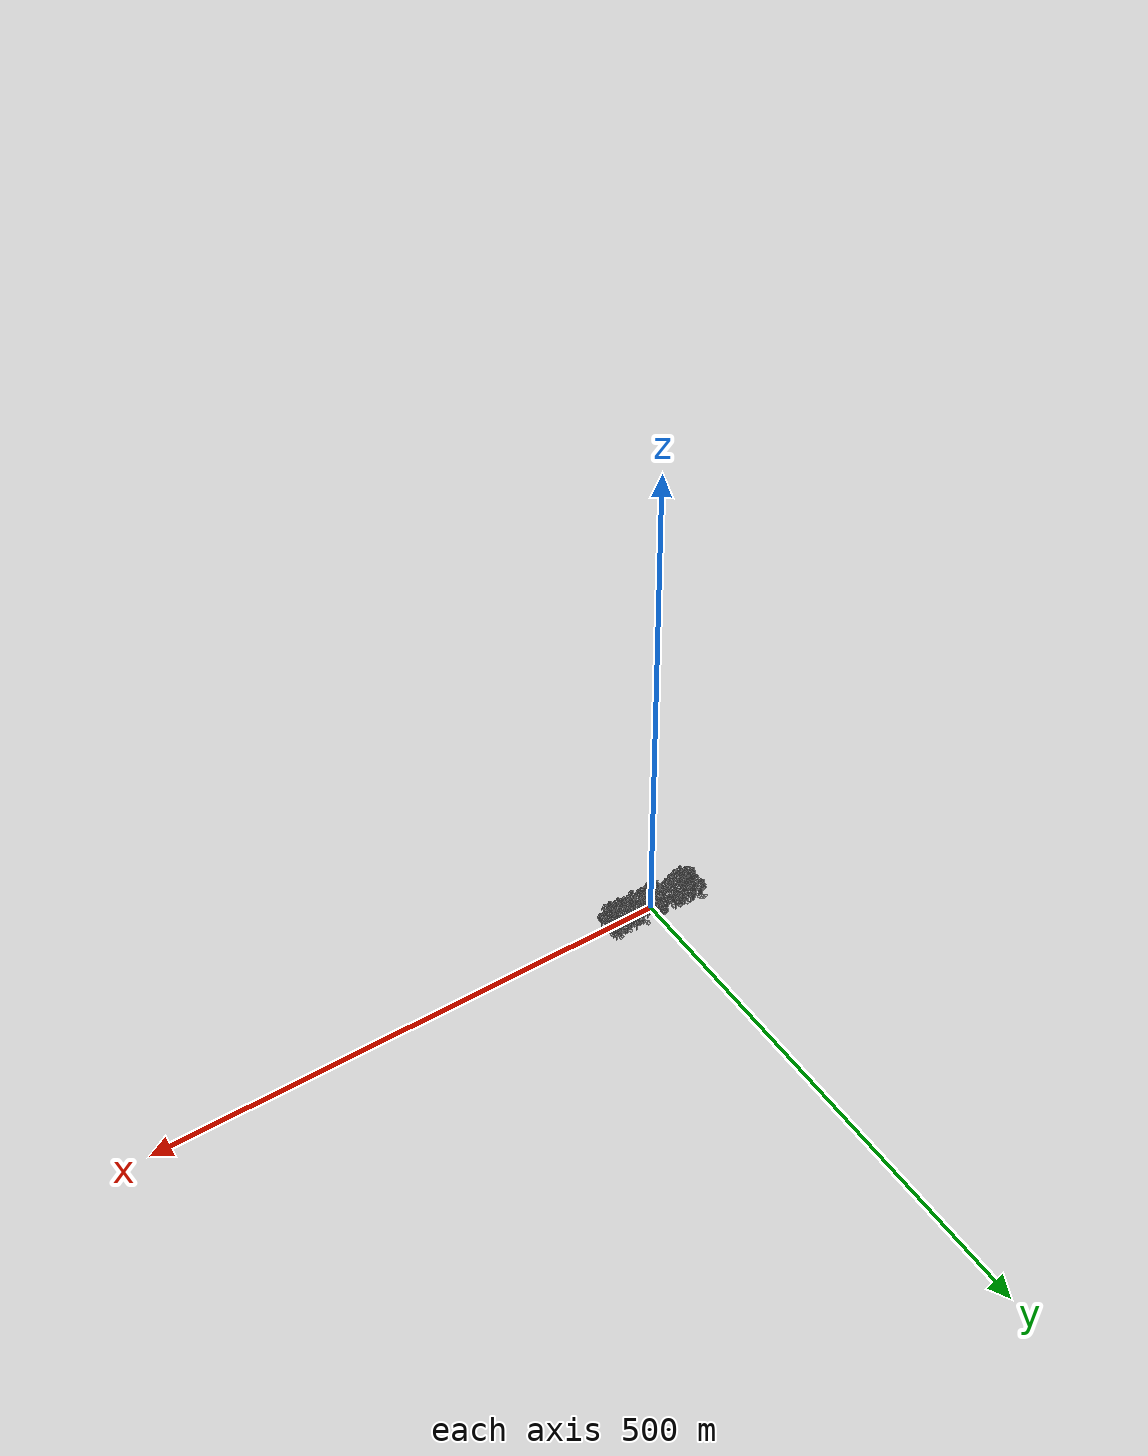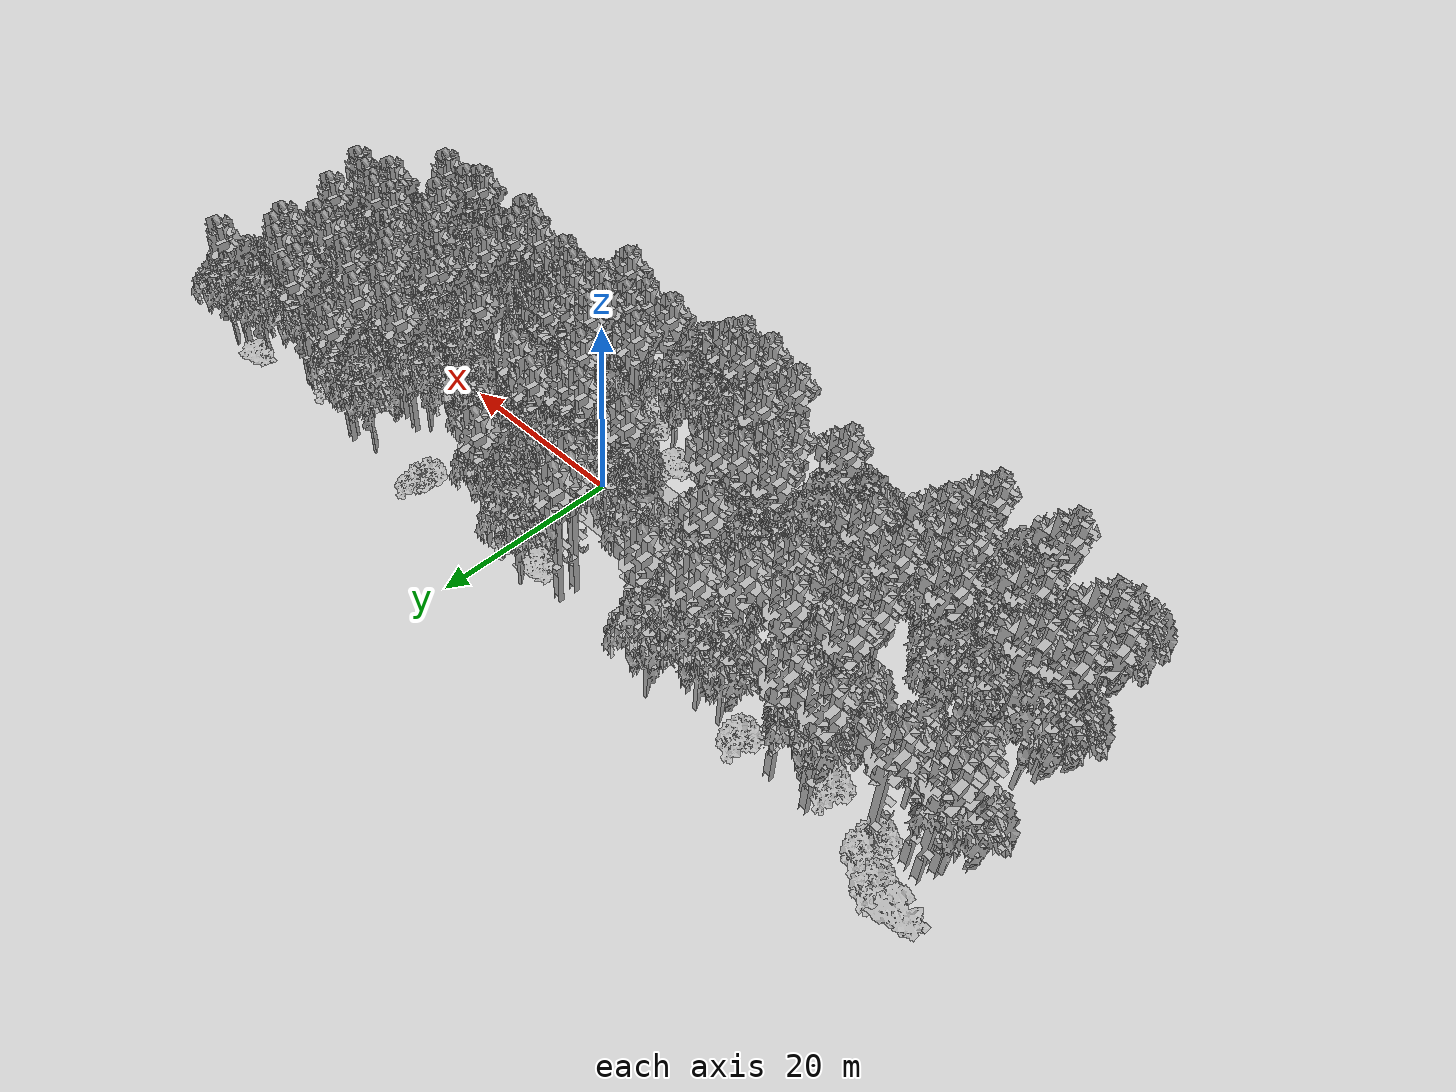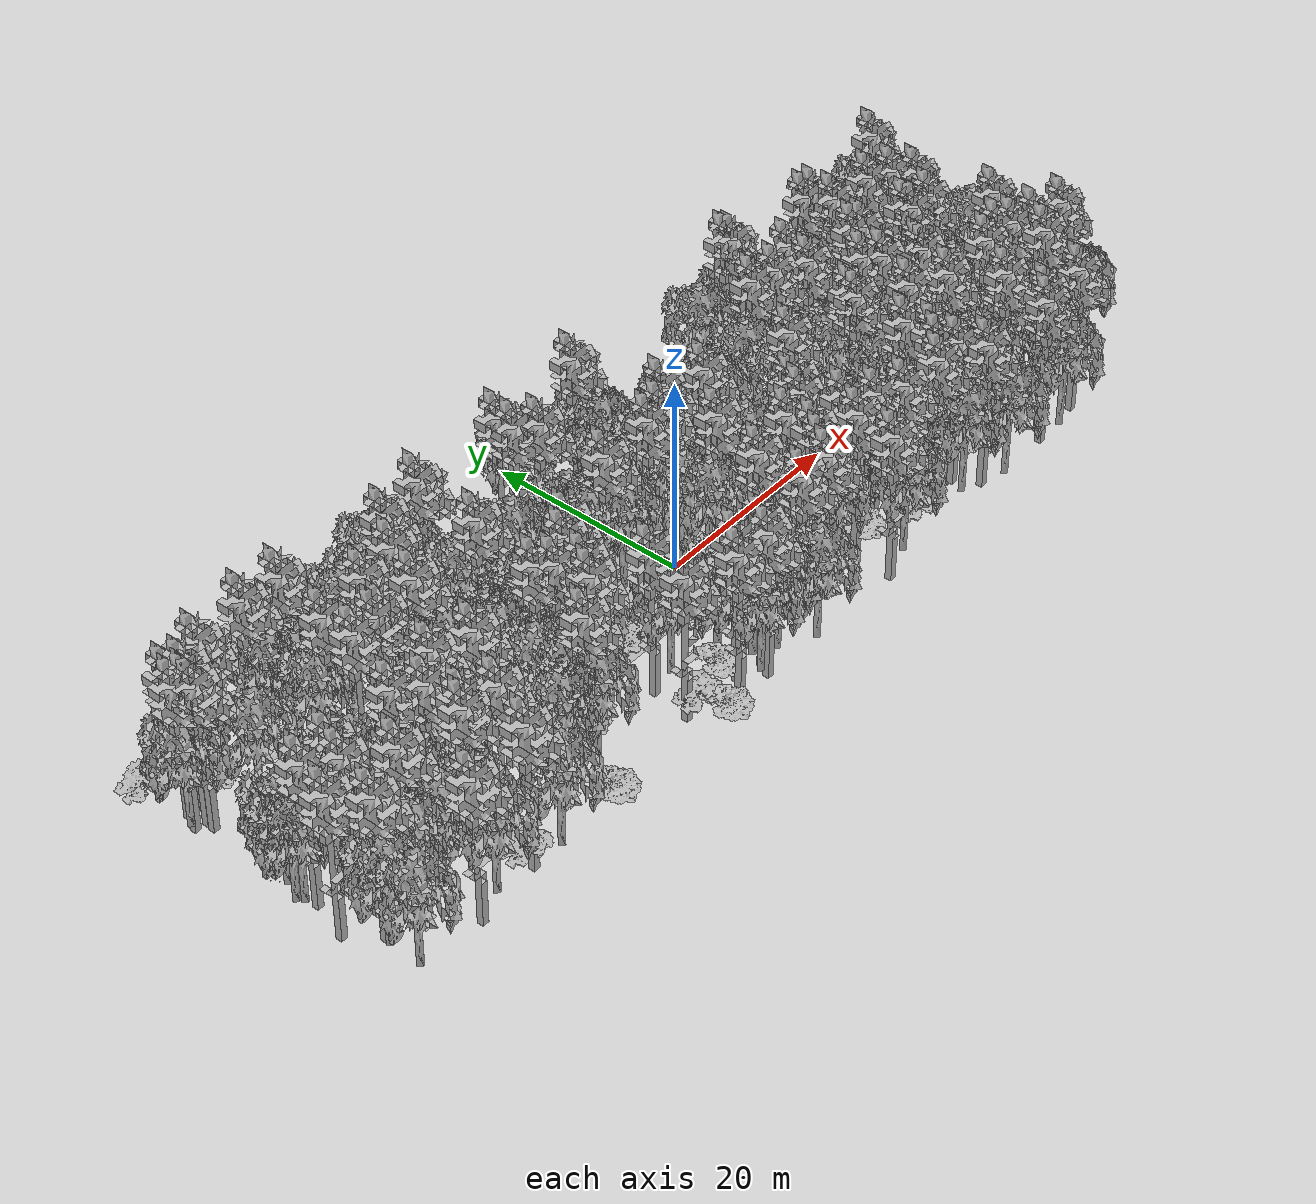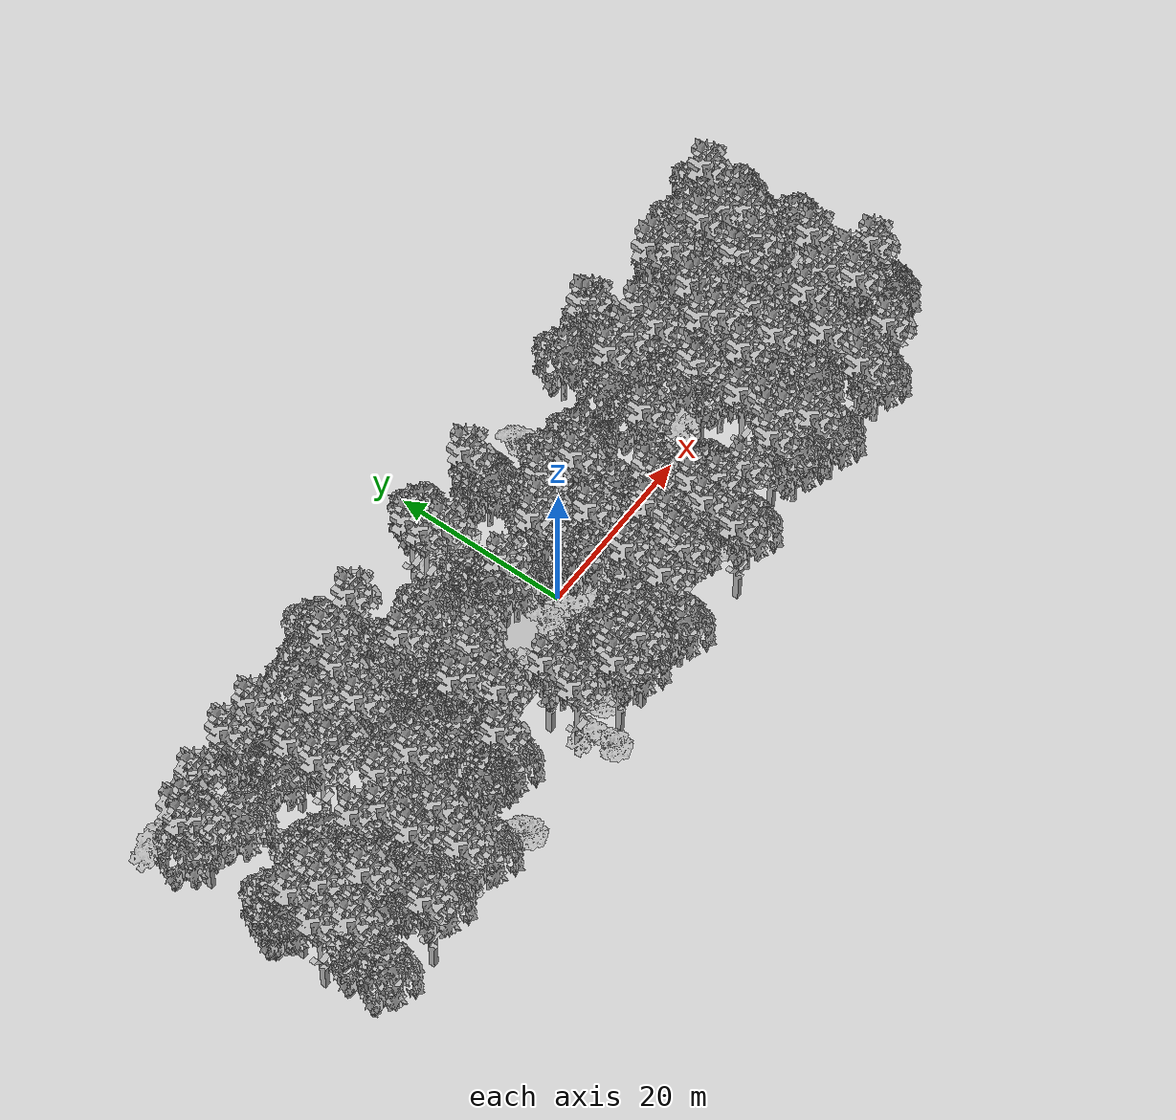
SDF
<sdf version="1.7">
    <world name="default">
        <plugin name="mrs_gazebo_static_transform_republisher_plugin" filename="libMrsGazeboCommonResources_StaticTransformRepublisher.so"/>
        <spherical_coordinates>
            <surface_model>EARTH_WGS84</surface_model>
            <latitude_deg>47.3977</latitude_deg>
            <longitude_deg>8.54559</longitude_deg>
            <elevation>0</elevation>
            <heading_deg>0</heading_deg>
        </spherical_coordinates>
        <physics name="default_physics" default="0" type="ode">
            <ode>
                <solver>
                    <type>quick</type>
                    <iters>10</iters>
                    <sor>1.3</sor>
                    <use_dynamic_moi_rescaling>0</use_dynamic_moi_rescaling>
                </solver>
                <constraints>
                    <cfm>0</cfm>
                    <erp>0.2</erp>
                    <contact_max_correcting_vel>1000</contact_max_correcting_vel>
                    <contact_surface_layer>0.001</contact_surface_layer>
                </constraints>
            </ode>
            <max_step_size>0.004</max_step_size>
            <real_time_factor>1</real_time_factor>
            <real_time_update_rate>250</real_time_update_rate>
        </physics>
        <scene>
            <shadows>0</shadows>
            <ambient>0.4 0.4 0.4 1</ambient>
            <background>0.7 0.7 0.7 1</background>
        </scene>
        <light name="sun" type="directional">
            <pose>0 0 1000 0.4 0.2 0</pose>
            <diffuse>1 1 1 1</diffuse>
            <specular>0.6 0.6 0.6 1</specular>
            <direction>0.1 0.1 -0.9</direction>
            <attenuation>
                <range>20</range>
                <constant>0.5</constant>
                <linear>0.01</linear>
                <quadratic>0.001</quadratic>
            </attenuation>
            <cast_shadows>1</cast_shadows>
            <spot>
                <inner_angle>0</inner_angle>
                <outer_angle>0</outer_angle>
                <falloff>0</falloff>
            </spot>
        </light>
        <model name="ground_plane">
            <static>1</static>
            <link name="link">
                <collision name="collision">
                    <pose>-50 0 0 0 -0 0</pose>
                    <geometry>
                        <plane>
                            <normal>0 0 1</normal>
                            <size>100 100</size>
                        </plane>
                    </geometry>
                    <surface>
                        <contact>
                            <ode>
                                <min_depth>0.01</min_depth>
                                <max_vel>0</max_vel>
                            </ode>
                        </contact>
                        <friction>
                            <ode/>
                            <torsional>
                                <ode/>
                            </torsional>
                        </friction>
                        <bounce/>
                    </surface>
                    <max_contacts>10</max_contacts>
                </collision>
                <visual name="grass">
                    <pose>0 0 0 0 -0 0</pose>
                    <cast_shadows>0</cast_shadows>
                    <geometry>
                        <mesh>
                            <scale>0.5814285714285714 0.18142857142857144 0.1</scale>
                            <uri>file://grass_plane/meshes/grass_plane.dae</uri>
                        </mesh>
                    </geometry>
                </visual>
                <self_collide>0</self_collide>
                <enable_wind>0</enable_wind>
                <kinematic>0</kinematic>
            </link>
        </model>
        <model name="the_void">
            <static>1</static>
            <link name="link">
                <pose>0 0 0.1 0 -0 0</pose>
                <visual name="the_void">
                    <pose>0 0 2 0 -0 0</pose>
                    <geometry>
                        <sphere>
                            <radius>0.25</radius>
                        </sphere>
                    </geometry>
                    <material>
                        <script>
                            <uri>file://media/materials/scripts/Gazebo.material</uri>
                            <name>Gazebo/Black</name>
                        </script>
                    </material>
                </visual>
                <self_collide>0</self_collide>
                <enable_wind>0</enable_wind>
                <kinematic>0</kinematic>
            </link>
            <pose>-1000 -1000 0 0 -0 0</pose>
        </model>
        <gui fullscreen="0">
            <camera name="camera">
                <pose>35.1577 98.6044 40.0204 0 0.407996 -1.99761</pose>
                <view_controller>orbit</view_controller>
                <projection_type>perspective</projection_type>
            </camera>
        </gui>
        <plugin name="mrs_gazebo_rviz_cam_synchronizer" filename="libMrsGazeboCommonResources_RvizCameraSynchronizer.so">
            <target_frame_id>gazebo_user_camera</target_frame_id>
            <world_origin_frame_id>uav1/gps_origin</world_origin_frame_id>
            <frame_to_follow>uav1</frame_to_follow>
        </plugin>
        <gravity>0 0 -9.8066</gravity>
        <magnetic_field>6e-06 2.3e-05 -4.2e-05</magnetic_field>
        <atmosphere type="adiabatic"/>
        <wind/>
        <model name="Tree 0">
            <static>1</static>
            <pose>-36.85921534294585 -9.722802604037224 0 1.57079 -0 0</pose>
            <link name="link">
                <pose>0 0 0 0 -0 0</pose>
                <collision name="collision">
                    <geometry>
                        <mesh>
                            <scale>3.5 5 3.5</scale>
                            <uri>model://tree_2/meshes/tree_2.obj</uri>
                        </mesh>
                    </geometry>
                    <max_contacts>10</max_contacts>
                    <surface>
                        <contact>
                            <ode/>
                        </contact>
                        <bounce/>
                        <friction>
                            <torsional>
                                <ode/>
                            </torsional>
                            <ode/>
                        </friction>
                    </surface>
                </collision>
                <visual name="visual">
                    <geometry>
                        <mesh>
                            <scale>3.5 5 3.5</scale>
                            <uri>model://tree_2/meshes/tree_2.obj</uri>
                        </mesh>
                    </geometry>
                </visual>
                <self_collide>0</self_collide>
                <enable_wind>0</enable_wind>
                <kinematic>0</kinematic>
            </link>
        </model>
        <model name="Tree 1">
            <static>1</static>
            <pose>2.039314229025379 3.0420164077007037 0 1.57079 -0 0</pose>
            <link name="link">
                <pose>0 0 0 0 -0 0</pose>
                <collision name="collision">
                    <geometry>
                        <mesh>
                            <scale>3.5 5 3.5</scale>
                            <uri>model://tree_9/meshes/tree_9.obj</uri>
                        </mesh>
                    </geometry>
                    <max_contacts>10</max_contacts>
                    <surface>
                        <contact>
                            <ode/>
                        </contact>
                        <bounce/>
                        <friction>
                            <torsional>
                                <ode/>
                            </torsional>
                            <ode/>
                        </friction>
                    </surface>
                </collision>
                <visual name="visual">
                    <geometry>
                        <mesh>
                            <scale>3.5 5 3.5</scale>
                            <uri>model://tree_9/meshes/tree_9.obj</uri>
                        </mesh>
                    </geometry>
                </visual>
                <self_collide>0</self_collide>
                <enable_wind>0</enable_wind>
                <kinematic>0</kinematic>
            </link>
        </model>
        <model name="Tree 2">
            <static>1</static>
            <pose>-16.137026660960977 1.9340468512155624 0 1.57079 -0 0</pose>
            <link name="link">
                <pose>0 0 0 0 -0 0</pose>
                <collision name="collision">
                    <geometry>
                        <mesh>
                            <scale>3.5 5 3.5</scale>
                            <uri>model://tree_2/meshes/tree_2.obj</uri>
                        </mesh>
                    </geometry>
                    <max_contacts>10</max_contacts>
                    <surface>
                        <contact>
                            <ode/>
                        </contact>
                        <bounce/>
                        <friction>
                            <torsional>
                                <ode/>
                            </torsional>
                            <ode/>
                        </friction>
                    </surface>
                </collision>
                <visual name="visual">
                    <geometry>
                        <mesh>
                            <scale>3.5 5 3.5</scale>
                            <uri>model://tree_2/meshes/tree_2.obj</uri>
                        </mesh>
                    </geometry>
                </visual>
                <self_collide>0</self_collide>
                <enable_wind>0</enable_wind>
                <kinematic>0</kinematic>
            </link>
        </model>
        <model name="Tree 3">
            <static>1</static>
            <pose>-35.63989932845678 11.19704138836834 0 1.57079 -0 0</pose>
            <link name="link">
                <pose>0 0 0 0 -0 0</pose>
                <collision name="collision">
                    <geometry>
                        <mesh>
                            <scale>3.5 5 3.5</scale>
                            <uri>model://tree_2/meshes/tree_2.obj</uri>
                        </mesh>
                    </geometry>
                    <max_contacts>10</max_contacts>
                    <surface>
                        <contact>
                            <ode/>
                        </contact>
                        <bounce/>
                        <friction>
                            <torsional>
                                <ode/>
                            </torsional>
                            <ode/>
                        </friction>
                    </surface>
                </collision>
                <visual name="visual">
                    <geometry>
                        <mesh>
                            <scale>3.5 5 3.5</scale>
                            <uri>model://tree_2/meshes/tree_2.obj</uri>
                        </mesh>
                    </geometry>
                </visual>
                <self_collide>0</self_collide>
                <enable_wind>0</enable_wind>
                <kinematic>0</kinematic>
            </link>
        </model>
        <model name="Tree 4">
            <static>1</static>
            <pose>30.348621100929932 12.14553751947339 0 1.57079 -0 0</pose>
            <link name="link">
                <pose>0 0 0 0 -0 0</pose>
                <collision name="collision">
                    <geometry>
                        <mesh>
                            <scale>4 2.5 4</scale>
                            <uri>model://tree_1/meshes/tree_1.obj</uri>
                        </mesh>
                    </geometry>
                    <max_contacts>10</max_contacts>
                    <surface>
                        <contact>
                            <ode/>
                        </contact>
                        <bounce/>
                        <friction>
                            <torsional>
                                <ode/>
                            </torsional>
                            <ode/>
                        </friction>
                    </surface>
                </collision>
                <visual name="visual">
                    <geometry>
                        <mesh>
                            <scale>4 2.5 4</scale>
                            <uri>model://tree_1/meshes/tree_1.obj</uri>
                        </mesh>
                    </geometry>
                </visual>
                <self_collide>0</self_collide>
                <enable_wind>0</enable_wind>
                <kinematic>0</kinematic>
            </link>
        </model>
        <model name="Tree 5">
            <static>1</static>
            <pose>36.21630514174534 5.332473233112477 0 1.57079 -0 0</pose>
            <link name="link">
                <pose>0 0 0 0 -0 0</pose>
                <collision name="collision">
                    <geometry>
                        <mesh>
                            <scale>3.5 5 3.5</scale>
                            <uri>model://tree_2/meshes/tree_2.obj</uri>
                        </mesh>
                    </geometry>
                    <max_contacts>10</max_contacts>
                    <surface>
                        <contact>
                            <ode/>
                        </contact>
                        <bounce/>
                        <friction>
                            <torsional>
                                <ode/>
                            </torsional>
                            <ode/>
                        </friction>
                    </surface>
                </collision>
                <visual name="visual">
                    <geometry>
                        <mesh>
                            <scale>3.5 5 3.5</scale>
                            <uri>model://tree_2/meshes/tree_2.obj</uri>
                        </mesh>
                    </geometry>
                </visual>
                <self_collide>0</self_collide>
                <enable_wind>0</enable_wind>
                <kinematic>0</kinematic>
            </link>
        </model>
        <model name="Tree 6">
            <static>1</static>
            <pose>-19.921143829720222 -7.141556950328466 0 1.57079 -0 0</pose>
            <link name="link">
                <pose>0 0 0 0 -0 0</pose>
                <collision name="collision">
                    <geometry>
                        <mesh>
                            <scale>4 2.5 4</scale>
                            <uri>model://tree_1/meshes/tree_1.obj</uri>
                        </mesh>
                    </geometry>
                    <max_contacts>10</max_contacts>
                    <surface>
                        <contact>
                            <ode/>
                        </contact>
                        <bounce/>
                        <friction>
                            <torsional>
                                <ode/>
                            </torsional>
                            <ode/>
                        </friction>
                    </surface>
                </collision>
                <visual name="visual">
                    <geometry>
                        <mesh>
                            <scale>4 2.5 4</scale>
                            <uri>model://tree_1/meshes/tree_1.obj</uri>
                        </mesh>
                    </geometry>
                </visual>
                <self_collide>0</self_collide>
                <enable_wind>0</enable_wind>
                <kinematic>0</kinematic>
            </link>
        </model>
        <model name="Tree 7">
            <static>1</static>
            <pose>2.3119024017315937 12.992119698907906 0 1.57079 -0 0</pose>
            <link name="link">
                <pose>0 0 0 0 -0 0</pose>
                <collision name="collision">
                    <geometry>
                        <mesh>
                            <scale>3.5 5 3.5</scale>
                            <uri>model://tree_9/meshes/tree_9.obj</uri>
                        </mesh>
                    </geometry>
                    <max_contacts>10</max_contacts>
                    <surface>
                        <contact>
                            <ode/>
                        </contact>
                        <bounce/>
                        <friction>
                            <torsional>
                                <ode/>
                            </torsional>
                            <ode/>
                        </friction>
                    </surface>
                </collision>
                <visual name="visual">
                    <geometry>
                        <mesh>
                            <scale>3.5 5 3.5</scale>
                            <uri>model://tree_9/meshes/tree_9.obj</uri>
                        </mesh>
                    </geometry>
                </visual>
                <self_collide>0</self_collide>
                <enable_wind>0</enable_wind>
                <kinematic>0</kinematic>
            </link>
        </model>
        <model name="Tree 8">
            <static>1</static>
            <pose>-38.38184937173636 10.735725459265133 0 1.57079 -0 0</pose>
            <link name="link">
                <pose>0 0 0 0 -0 0</pose>
                <collision name="collision">
                    <geometry>
                        <mesh>
                            <scale>4 2.5 4</scale>
                            <uri>model://tree_1/meshes/tree_1.obj</uri>
                        </mesh>
                    </geometry>
                    <max_contacts>10</max_contacts>
                    <surface>
                        <contact>
                            <ode/>
                        </contact>
                        <bounce/>
                        <friction>
                            <torsional>
                                <ode/>
                            </torsional>
                            <ode/>
                        </friction>
                    </surface>
                </collision>
                <visual name="visual">
                    <geometry>
                        <mesh>
                            <scale>4 2.5 4</scale>
                            <uri>model://tree_1/meshes/tree_1.obj</uri>
                        </mesh>
                    </geometry>
                </visual>
                <self_collide>0</self_collide>
                <enable_wind>0</enable_wind>
                <kinematic>0</kinematic>
            </link>
        </model>
        <model name="Tree 9">
            <static>1</static>
            <pose>-15.664485438454356 -3.526763142565402 0 1.57079 -0 0</pose>
            <link name="link">
                <pose>0 0 0 0 -0 0</pose>
                <collision name="collision">
                    <geometry>
                        <mesh>
                            <scale>3.5 5 3.5</scale>
                            <uri>model://tree_2/meshes/tree_2.obj</uri>
                        </mesh>
                    </geometry>
                    <max_contacts>10</max_contacts>
                    <surface>
                        <contact>
                            <ode/>
                        </contact>
                        <bounce/>
                        <friction>
                            <torsional>
                                <ode/>
                            </torsional>
                            <ode/>
                        </friction>
                    </surface>
                </collision>
                <visual name="visual">
                    <geometry>
                        <mesh>
                            <scale>3.5 5 3.5</scale>
                            <uri>model://tree_2/meshes/tree_2.obj</uri>
                        </mesh>
                    </geometry>
                </visual>
                <self_collide>0</self_collide>
                <enable_wind>0</enable_wind>
                <kinematic>0</kinematic>
            </link>
        </model>
        <model name="Tree 10">
            <static>1</static>
            <pose>-18.453464350637507 5.146567638253263 0 1.57079 -0 0</pose>
            <link name="link">
                <pose>0 0 0 0 -0 0</pose>
                <collision name="collision">
                    <geometry>
                        <mesh>
                            <scale>3.5 5 3.5</scale>
                            <uri>model://tree_9/meshes/tree_9.obj</uri>
                        </mesh>
                    </geometry>
                    <max_contacts>10</max_contacts>
                    <surface>
                        <contact>
                            <ode/>
                        </contact>
                        <bounce/>
                        <friction>
                            <torsional>
                                <ode/>
                            </torsional>
                            <ode/>
                        </friction>
                    </surface>
                </collision>
                <visual name="visual">
                    <geometry>
                        <mesh>
                            <scale>3.5 5 3.5</scale>
                            <uri>model://tree_9/meshes/tree_9.obj</uri>
                        </mesh>
                    </geometry>
                </visual>
                <self_collide>0</self_collide>
                <enable_wind>0</enable_wind>
                <kinematic>0</kinematic>
            </link>
        </model>
        <model name="Tree 11">
            <static>1</static>
            <pose>17.115944217894665 -7.905770410894978 0 1.57079 -0 0</pose>
            <link name="link">
                <pose>0 0 0 0 -0 0</pose>
                <collision name="collision">
                    <geometry>
                        <mesh>
                            <scale>3.5 5 3.5</scale>
                            <uri>model://tree_2/meshes/tree_2.obj</uri>
                        </mesh>
                    </geometry>
                    <max_contacts>10</max_contacts>
                    <surface>
                        <contact>
                            <ode/>
                        </contact>
                        <bounce/>
                        <friction>
                            <torsional>
                                <ode/>
                            </torsional>
                            <ode/>
                        </friction>
                    </surface>
                </collision>
                <visual name="visual">
                    <geometry>
                        <mesh>
                            <scale>3.5 5 3.5</scale>
                            <uri>model://tree_2/meshes/tree_2.obj</uri>
                        </mesh>
                    </geometry>
                </visual>
                <self_collide>0</self_collide>
                <enable_wind>0</enable_wind>
                <kinematic>0</kinematic>
            </link>
        </model>
        <model name="Tree 12">
            <static>1</static>
            <pose>-35.21450316078336 -4.842496373526851 0 1.57079 -0 0</pose>
            <link name="link">
                <pose>0 0 0 0 -0 0</pose>
                <collision name="collision">
                    <geometry>
                        <mesh>
                            <scale>3.5 5 3.5</scale>
                            <uri>model://tree_9/meshes/tree_9.obj</uri>
                        </mesh>
                    </geometry>
                    <max_contacts>10</max_contacts>
                    <surface>
                        <contact>
                            <ode/>
                        </contact>
                        <bounce/>
                        <friction>
                            <torsional>
                                <ode/>
                            </torsional>
                            <ode/>
                        </friction>
                    </surface>
                </collision>
                <visual name="visual">
                    <geometry>
                        <mesh>
                            <scale>3.5 5 3.5</scale>
                            <uri>model://tree_9/meshes/tree_9.obj</uri>
                        </mesh>
                    </geometry>
                </visual>
                <self_collide>0</self_collide>
                <enable_wind>0</enable_wind>
                <kinematic>0</kinematic>
            </link>
        </model>
        <model name="Tree 13">
            <static>1</static>
            <pose>-47.10310080382826 11.049040701368767 0 1.57079 -0 0</pose>
            <link name="link">
                <pose>0 0 0 0 -0 0</pose>
                <collision name="collision">
                    <geometry>
                        <mesh>
                            <scale>3.5 5 3.5</scale>
                            <uri>model://tree_9/meshes/tree_9.obj</uri>
                        </mesh>
                    </geometry>
                    <max_contacts>10</max_contacts>
                    <surface>
                        <contact>
                            <ode/>
                        </contact>
                        <bounce/>
                        <friction>
                            <torsional>
                                <ode/>
                            </torsional>
                            <ode/>
                        </friction>
                    </surface>
                </collision>
                <visual name="visual">
                    <geometry>
                        <mesh>
                            <scale>3.5 5 3.5</scale>
                            <uri>model://tree_9/meshes/tree_9.obj</uri>
                        </mesh>
                    </geometry>
                </visual>
                <self_collide>0</self_collide>
                <enable_wind>0</enable_wind>
                <kinematic>0</kinematic>
            </link>
        </model>
        <model name="Tree 14">
            <static>1</static>
            <pose>32.87773157548624 -4.341717921988613 0 1.57079 -0 0</pose>
            <link name="link">
                <pose>0 0 0 0 -0 0</pose>
                <collision name="collision">
                    <geometry>
                        <mesh>
                            <scale>3.5 5 3.5</scale>
                            <uri>model://tree_9/meshes/tree_9.obj</uri>
                        </mesh>
                    </geometry>
                    <max_contacts>10</max_contacts>
                    <surface>
                        <contact>
                            <ode/>
                        </contact>
                        <bounce/>
                        <friction>
                            <torsional>
                                <ode/>
                            </torsional>
                            <ode/>
                        </friction>
                    </surface>
                </collision>
                <visual name="visual">
                    <geometry>
                        <mesh>
                            <scale>3.5 5 3.5</scale>
                            <uri>model://tree_9/meshes/tree_9.obj</uri>
                        </mesh>
                    </geometry>
                </visual>
                <self_collide>0</self_collide>
                <enable_wind>0</enable_wind>
                <kinematic>0</kinematic>
            </link>
        </model>
        <model name="Tree 15">
            <static>1</static>
            <pose>45.743909206577584 13.819128659880295 0 1.57079 -0 0</pose>
            <link name="link">
                <pose>0 0 0 0 -0 0</pose>
                <collision name="collision">
                    <geometry>
                        <mesh>
                            <scale>3.5 5 3.5</scale>
                            <uri>model://tree_9/meshes/tree_9.obj</uri>
                        </mesh>
                    </geometry>
                    <max_contacts>10</max_contacts>
                    <surface>
                        <contact>
                            <ode/>
                        </contact>
                        <bounce/>
                        <friction>
                            <torsional>
                                <ode/>
                            </torsional>
                            <ode/>
                        </friction>
                    </surface>
                </collision>
                <visual name="visual">
                    <geometry>
                        <mesh>
                            <scale>3.5 5 3.5</scale>
                            <uri>model://tree_9/meshes/tree_9.obj</uri>
                        </mesh>
                    </geometry>
                </visual>
                <self_collide>0</self_collide>
                <enable_wind>0</enable_wind>
                <kinematic>0</kinematic>
            </link>
        </model>
        <model name="Tree 16">
            <static>1</static>
            <pose>8.859045355864367 3.6478221776824995 0 1.57079 -0 0</pose>
            <link name="link">
                <pose>0 0 0 0 -0 0</pose>
                <collision name="collision">
                    <geometry>
                        <mesh>
                            <scale>3.5 5 3.5</scale>
                            <uri>model://tree_2/meshes/tree_2.obj</uri>
                        </mesh>
                    </geometry>
                    <max_contacts>10</max_contacts>
                    <surface>
                        <contact>
                            <ode/>
                        </contact>
                        <bounce/>
                        <friction>
                            <torsional>
                                <ode/>
                            </torsional>
                            <ode/>
                        </friction>
                    </surface>
                </collision>
                <visual name="visual">
                    <geometry>
                        <mesh>
                            <scale>3.5 5 3.5</scale>
                            <uri>model://tree_2/meshes/tree_2.obj</uri>
                        </mesh>
                    </geometry>
                </visual>
                <self_collide>0</self_collide>
                <enable_wind>0</enable_wind>
                <kinematic>0</kinematic>
            </link>
        </model>
        <model name="Tree 17">
            <static>1</static>
            <pose>-32.1912204562856 -2.5034486556960456 0 1.57079 -0 0</pose>
            <link name="link">
                <pose>0 0 0 0 -0 0</pose>
                <collision name="collision">
                    <geometry>
                        <mesh>
                            <scale>3.5 5 3.5</scale>
                            <uri>model://tree_9/meshes/tree_9.obj</uri>
                        </mesh>
                    </geometry>
                    <max_contacts>10</max_contacts>
                    <surface>
                        <contact>
                            <ode/>
                        </contact>
                        <bounce/>
                        <friction>
                            <torsional>
                                <ode/>
                            </torsional>
                            <ode/>
                        </friction>
                    </surface>
                </collision>
                <visual name="visual">
                    <geometry>
                        <mesh>
                            <scale>3.5 5 3.5</scale>
                            <uri>model://tree_9/meshes/tree_9.obj</uri>
                        </mesh>
                    </geometry>
                </visual>
                <self_collide>0</self_collide>
                <enable_wind>0</enable_wind>
                <kinematic>0</kinematic>
            </link>
        </model>
        <model name="Tree 18">
            <static>1</static>
            <pose>-25.53865518856384 3.1005544694515983 0 1.57079 -0 0</pose>
            <link name="link">
                <pose>0 0 0 0 -0 0</pose>
                <collision name="collision">
                    <geometry>
                        <mesh>
                            <scale>3.5 5 3.5</scale>
                            <uri>model://tree_2/meshes/tree_2.obj</uri>
                        </mesh>
                    </geometry>
                    <max_contacts>10</max_contacts>
                    <surface>
                        <contact>
                            <ode/>
                        </contact>
                        <bounce/>
                        <friction>
                            <torsional>
                                <ode/>
                            </torsional>
                            <ode/>
                        </friction>
                    </surface>
                </collision>
                <visual name="visual">
                    <geometry>
                        <mesh>
                            <scale>3.5 5 3.5</scale>
                            <uri>model://tree_2/meshes/tree_2.obj</uri>
                        </mesh>
                    </geometry>
                </visual>
                <self_collide>0</self_collide>
                <enable_wind>0</enable_wind>
                <kinematic>0</kinematic>
            </link>
        </model>
        <model name="Tree 19">
            <static>1</static>
            <pose>-23.327662387530005 6.976736187923045 0 1.57079 -0 0</pose>
            <link name="link">
                <pose>0 0 0 0 -0 0</pose>
                <collision name="collision">
                    <geometry>
                        <mesh>
                            <scale>4 2.5 4</scale>
                            <uri>model://tree_1/meshes/tree_1.obj</uri>
                        </mesh>
                    </geometry>
                    <max_contacts>10</max_contacts>
                    <surface>
                        <contact>
                            <ode/>
                        </contact>
                        <bounce/>
                        <friction>
                            <torsional>
                                <ode/>
                            </torsional>
                            <ode/>
                        </friction>
                    </surface>
                </collision>
                <visual name="visual">
                    <geometry>
                        <mesh>
                            <scale>4 2.5 4</scale>
                            <uri>model://tree_1/meshes/tree_1.obj</uri>
                        </mesh>
                    </geometry>
                </visual>
                <self_collide>0</self_collide>
                <enable_wind>0</enable_wind>
                <kinematic>0</kinematic>
            </link>
        </model>
        <model name="Tree 20">
            <static>1</static>
            <pose>-5.367888918800531 -8.953199204432263 0 1.57079 -0 0</pose>
            <link name="link">
                <pose>0 0 0 0 -0 0</pose>
                <collision name="collision">
                    <geometry>
                        <mesh>
                            <scale>3.5 5 3.5</scale>
                            <uri>model://tree_2/meshes/tree_2.obj</uri>
                        </mesh>
                    </geometry>
                    <max_contacts>10</max_contacts>
                    <surface>
                        <contact>
                            <ode/>
                        </contact>
                        <bounce/>
                        <friction>
                            <torsional>
                                <ode/>
                            </torsional>
                            <ode/>
                        </friction>
                    </surface>
                </collision>
                <visual name="visual">
                    <geometry>
                        <mesh>
                            <scale>3.5 5 3.5</scale>
                            <uri>model://tree_2/meshes/tree_2.obj</uri>
                        </mesh>
                    </geometry>
                </visual>
                <self_collide>0</self_collide>
                <enable_wind>0</enable_wind>
                <kinematic>0</kinematic>
            </link>
        </model>
        <model name="Tree 21">
            <static>1</static>
            <pose>-0.5704055620577222 12.196740696156223 0 1.57079 -0 0</pose>
            <link name="link">
                <pose>0 0 0 0 -0 0</pose>
                <collision name="collision">
                    <geometry>
                        <mesh>
                            <scale>4 2.5 4</scale>
                            <uri>model://tree_1/meshes/tree_1.obj</uri>
                        </mesh>
                    </geometry>
                    <max_contacts>10</max_contacts>
                    <surface>
                        <contact>
                            <ode/>
                        </contact>
                        <bounce/>
                        <friction>
                            <torsional>
                                <ode/>
                            </torsional>
                            <ode/>
                        </friction>
                    </surface>
                </collision>
                <visual name="visual">
                    <geometry>
                        <mesh>
                            <scale>4 2.5 4</scale>
                            <uri>model://tree_1/meshes/tree_1.obj</uri>
                        </mesh>
                    </geometry>
                </visual>
                <self_collide>0</self_collide>
                <enable_wind>0</enable_wind>
                <kinematic>0</kinematic>
            </link>
        </model>
        <model name="Tree 22">
            <static>1</static>
            <pose>45.19491098389037 -3.7679552045465208 0 1.57079 -0 0</pose>
            <link name="link">
                <pose>0 0 0 0 -0 0</pose>
                <collision name="collision">
                    <geometry>
                        <mesh>
                            <scale>3.5 5 3.5</scale>
                            <uri>model://tree_2/meshes/tree_2.obj</uri>
                        </mesh>
                    </geometry>
                    <max_contacts>10</max_contacts>
                    <surface>
                        <contact>
                            <ode/>
                        </contact>
                        <bounce/>
                        <friction>
                            <torsional>
                                <ode/>
                            </torsional>
                            <ode/>
                        </friction>
                    </surface>
                </collision>
                <visual name="visual">
                    <geometry>
                        <mesh>
                            <scale>3.5 5 3.5</scale>
                            <uri>model://tree_2/meshes/tree_2.obj</uri>
                        </mesh>
                    </geometry>
                </visual>
                <self_collide>0</self_collide>
                <enable_wind>0</enable_wind>
                <kinematic>0</kinematic>
            </link>
        </model>
        <model name="Tree 23">
            <static>1</static>
            <pose>-2.4384531195508927 -13.010256735968694 0 1.57079 -0 0</pose>
            <link name="link">
                <pose>0 0 0 0 -0 0</pose>
                <collision name="collision">
                    <geometry>
                        <mesh>
                            <scale>3.5 5 3.5</scale>
                            <uri>model://tree_2/meshes/tree_2.obj</uri>
                        </mesh>
                    </geometry>
                    <max_contacts>10</max_contacts>
                    <surface>
                        <contact>
                            <ode/>
                        </contact>
                        <bounce/>
                        <friction>
                            <torsional>
                                <ode/>
                            </torsional>
                            <ode/>
                        </friction>
                    </surface>
                </collision>
                <visual name="visual">
                    <geometry>
                        <mesh>
                            <scale>3.5 5 3.5</scale>
                            <uri>model://tree_2/meshes/tree_2.obj</uri>
                        </mesh>
                    </geometry>
                </visual>
                <self_collide>0</self_collide>
                <enable_wind>0</enable_wind>
                <kinematic>0</kinematic>
            </link>
        </model>
        <model name="Tree 24">
            <static>1</static>
            <pose>-34.49805732719764 -7.907337376200249 0 1.57079 -0 0</pose>
            <link name="link">
                <pose>0 0 0 0 -0 0</pose>
                <collision name="collision">
                    <geometry>
                        <mesh>
                            <scale>3.5 5 3.5</scale>
                            <uri>model://tree_9/meshes/tree_9.obj</uri>
                        </mesh>
                    </geometry>
                    <max_contacts>10</max_contacts>
                    <surface>
                        <contact>
                            <ode/>
                        </contact>
                        <bounce/>
                        <friction>
                            <torsional>
                                <ode/>
                            </torsional>
                            <ode/>
                        </friction>
                    </surface>
                </collision>
                <visual name="visual">
                    <geometry>
                        <mesh>
                            <scale>3.5 5 3.5</scale>
                            <uri>model://tree_9/meshes/tree_9.obj</uri>
                        </mesh>
                    </geometry>
                </visual>
                <self_collide>0</self_collide>
                <enable_wind>0</enable_wind>
                <kinematic>0</kinematic>
            </link>
        </model>
        <model name="Tree 25">
            <static>1</static>
            <pose>37.197878723263244 -13.987686216471614 0 1.57079 -0 0</pose>
            <link name="link">
                <pose>0 0 0 0 -0 0</pose>
                <collision name="collision">
                    <geometry>
                        <mesh>
                            <scale>3.5 5 3.5</scale>
                            <uri>model://tree_2/meshes/tree_2.obj</uri>
                        </mesh>
                    </geometry>
                    <max_contacts>10</max_contacts>
                    <surface>
                        <contact>
                            <ode/>
                        </contact>
                        <bounce/>
                        <friction>
                            <torsional>
                                <ode/>
                            </torsional>
                            <ode/>
                        </friction>
                    </surface>
                </collision>
                <visual name="visual">
                    <geometry>
                        <mesh>
                            <scale>3.5 5 3.5</scale>
                            <uri>model://tree_2/meshes/tree_2.obj</uri>
                        </mesh>
                    </geometry>
                </visual>
                <self_collide>0</self_collide>
                <enable_wind>0</enable_wind>
                <kinematic>0</kinematic>
            </link>
        </model>
        <model name="Tree 26">
            <static>1</static>
            <pose>27.782344782686934 9.301674965134488 0 1.57079 -0 0</pose>
            <link name="link">
                <pose>0 0 0 0 -0 0</pose>
                <collision name="collision">
                    <geometry>
                        <mesh>
                            <scale>3.5 5 3.5</scale>
                            <uri>model://tree_2/meshes/tree_2.obj</uri>
                        </mesh>
                    </geometry>
                    <max_contacts>10</max_contacts>
                    <surface>
                        <contact>
                            <ode/>
                        </contact>
                        <bounce/>
                        <friction>
                            <torsional>
                                <ode/>
                            </torsional>
                            <ode/>
                        </friction>
                    </surface>
                </collision>
                <visual name="visual">
                    <geometry>
                        <mesh>
                            <scale>3.5 5 3.5</scale>
                            <uri>model://tree_2/meshes/tree_2.obj</uri>
                        </mesh>
                    </geometry>
                </visual>
                <self_collide>0</self_collide>
                <enable_wind>0</enable_wind>
                <kinematic>0</kinematic>
            </link>
        </model>
        <model name="Tree 27">
            <static>1</static>
            <pose>-45.83507582881795 14.691953521509792 0 1.57079 -0 0</pose>
            <link name="link">
                <pose>0 0 0 0 -0 0</pose>
                <collision name="collision">
                    <geometry>
                        <mesh>
                            <scale>4 2.5 4</scale>
                            <uri>model://tree_1/meshes/tree_1.obj</uri>
                        </mesh>
                    </geometry>
                    <max_contacts>10</max_contacts>
                    <surface>
                        <contact>
                            <ode/>
                        </contact>
                        <bounce/>
                        <friction>
                            <torsional>
                                <ode/>
                            </torsional>
                            <ode/>
                        </friction>
                    </surface>
                </collision>
                <visual name="visual">
                    <geometry>
                        <mesh>
                            <scale>4 2.5 4</scale>
                            <uri>model://tree_1/meshes/tree_1.obj</uri>
                        </mesh>
                    </geometry>
                </visual>
                <self_collide>0</self_collide>
                <enable_wind>0</enable_wind>
                <kinematic>0</kinematic>
            </link>
        </model>
        <model name="Tree 28">
            <static>1</static>
            <pose>25.027270204580333 -0.147504677809847 0 1.57079 -0 0</pose>
            <link name="link">
                <pose>0 0 0 0 -0 0</pose>
                <collision name="collision">
                    <geometry>
                        <mesh>
                            <scale>3.5 5 3.5</scale>
                            <uri>model://tree_9/meshes/tree_9.obj</uri>
                        </mesh>
                    </geometry>
                    <max_contacts>10</max_contacts>
                    <surface>
                        <contact>
                            <ode/>
                        </contact>
                        <bounce/>
                        <friction>
                            <torsional>
                                <ode/>
                            </torsional>
                            <ode/>
                        </friction>
                    </surface>
                </collision>
                <visual name="visual">
                    <geometry>
                        <mesh>
                            <scale>3.5 5 3.5</scale>
                            <uri>model://tree_9/meshes/tree_9.obj</uri>
                        </mesh>
                    </geometry>
                </visual>
                <self_collide>0</self_collide>
                <enable_wind>0</enable_wind>
                <kinematic>0</kinematic>
            </link>
        </model>
        <model name="Tree 29">
            <static>1</static>
            <pose>-43.06568798121454 -8.74824961784848 0 1.57079 -0 0</pose>
            <link name="link">
                <pose>0 0 0 0 -0 0</pose>
                <collision name="collision">
                    <geometry>
                        <mesh>
                            <scale>3.5 5 3.5</scale>
                            <uri>model://tree_2/meshes/tree_2.obj</uri>
                        </mesh>
                    </geometry>
                    <max_contacts>10</max_contacts>
                    <surface>
                        <contact>
                            <ode/>
                        </contact>
                        <bounce/>
                        <friction>
                            <torsional>
                                <ode/>
                            </torsional>
                            <ode/>
                        </friction>
                    </surface>
                </collision>
                <visual name="visual">
                    <geometry>
                        <mesh>
                            <scale>3.5 5 3.5</scale>
                            <uri>model://tree_2/meshes/tree_2.obj</uri>
                        </mesh>
                    </geometry>
                </visual>
                <self_collide>0</self_collide>
                <enable_wind>0</enable_wind>
                <kinematic>0</kinematic>
            </link>
        </model>
        <model name="Tree 30">
            <static>1</static>
            <pose>-22.51316490393116 -0.0031905332640533857 0 1.57079 -0 0</pose>
            <link name="link">
                <pose>0 0 0 0 -0 0</pose>
                <collision name="collision">
                    <geometry>
                        <mesh>
                            <scale>3.5 5 3.5</scale>
                            <uri>model://tree_2/meshes/tree_2.obj</uri>
                        </mesh>
                    </geometry>
                    <max_contacts>10</max_contacts>
                    <surface>
                        <contact>
                            <ode/>
                        </contact>
                        <bounce/>
                        <friction>
                            <torsional>
                                <ode/>
                            </torsional>
                            <ode/>
                        </friction>
                    </surface>
                </collision>
                <visual name="visual">
                    <geometry>
                        <mesh>
                            <scale>3.5 5 3.5</scale>
                            <uri>model://tree_2/meshes/tree_2.obj</uri>
                        </mesh>
                    </geometry>
                </visual>
                <self_collide>0</self_collide>
                <enable_wind>0</enable_wind>
                <kinematic>0</kinematic>
            </link>
        </model>
        <model name="Tree 31">
            <static>1</static>
            <pose>45.15222607819281 -4.835462732482069 0 1.57079 -0 0</pose>
            <link name="link">
                <pose>0 0 0 0 -0 0</pose>
                <collision name="collision">
                    <geometry>
                        <mesh>
                            <scale>3.5 5 3.5</scale>
                            <uri>model://tree_9/meshes/tree_9.obj</uri>
                        </mesh>
                    </geometry>
                    <max_contacts>10</max_contacts>
                    <surface>
                        <contact>
                            <ode/>
                        </contact>
                        <bounce/>
                        <friction>
                            <torsional>
                                <ode/>
                            </torsional>
                            <ode/>
                        </friction>
                    </surface>
                </collision>
                <visual name="visual">
                    <geometry>
                        <mesh>
                            <scale>3.5 5 3.5</scale>
                            <uri>model://tree_9/meshes/tree_9.obj</uri>
                        </mesh>
                    </geometry>
                </visual>
                <self_collide>0</self_collide>
                <enable_wind>0</enable_wind>
                <kinematic>0</kinematic>
            </link>
        </model>
        <model name="Tree 32">
            <static>1</static>
            <pose>-23.273991926518562 -4.668934626666928 0 1.57079 -0 0</pose>
            <link name="link">
                <pose>0 0 0 0 -0 0</pose>
                <collision name="collision">
                    <geometry>
                        <mesh>
                            <scale>3.5 5 3.5</scale>
                            <uri>model://tree_2/meshes/tree_2.obj</uri>
                        </mesh>
                    </geometry>
                    <max_contacts>10</max_contacts>
                    <surface>
                        <contact>
                            <ode/>
                        </contact>
                        <bounce/>
                        <friction>
                            <torsional>
                                <ode/>
                            </torsional>
                            <ode/>
                        </friction>
                    </surface>
                </collision>
                <visual name="visual">
                    <geometry>
                        <mesh>
                            <scale>3.5 5 3.5</scale>
                            <uri>model://tree_2/meshes/tree_2.obj</uri>
                        </mesh>
                    </geometry>
                </visual>
                <self_collide>0</self_collide>
                <enable_wind>0</enable_wind>
                <kinematic>0</kinematic>
            </link>
        </model>
        <model name="Tree 33">
            <static>1</static>
            <pose>-41.56478956497732 -7.85211631656595 0 1.57079 -0 0</pose>
            <link name="link">
                <pose>0 0 0 0 -0 0</pose>
                <collision name="collision">
                    <geometry>
                        <mesh>
                            <scale>3.5 5 3.5</scale>
                            <uri>model://tree_9/meshes/tree_9.obj</uri>
                        </mesh>
                    </geometry>
                    <max_contacts>10</max_contacts>
                    <surface>
                        <contact>
                            <ode/>
                        </contact>
                        <bounce/>
                        <friction>
                            <torsional>
                                <ode/>
                            </torsional>
                            <ode/>
                        </friction>
                    </surface>
                </collision>
                <visual name="visual">
                    <geometry>
                        <mesh>
                            <scale>3.5 5 3.5</scale>
                            <uri>model://tree_9/meshes/tree_9.obj</uri>
                        </mesh>
                    </geometry>
                </visual>
                <self_collide>0</self_collide>
                <enable_wind>0</enable_wind>
                <kinematic>0</kinematic>
            </link>
        </model>
        <model name="Tree 34">
            <static>1</static>
            <pose>-19.95909837796274 0.46358298691831656 0 1.57079 -0 0</pose>
            <link name="link">
                <pose>0 0 0 0 -0 0</pose>
                <collision name="collision">
                    <geometry>
                        <mesh>
                            <scale>3.5 5 3.5</scale>
                            <uri>model://tree_2/meshes/tree_2.obj</uri>
                        </mesh>
                    </geometry>
                    <max_contacts>10</max_contacts>
                    <surface>
                        <contact>
                            <ode/>
                        </contact>
                        <bounce/>
                        <friction>
                            <torsional>
                                <ode/>
                            </torsional>
                            <ode/>
                        </friction>
                    </surface>
                </collision>
                <visual name="visual">
                    <geometry>
                        <mesh>
                            <scale>3.5 5 3.5</scale>
                            <uri>model://tree_2/meshes/tree_2.obj</uri>
                        </mesh>
                    </geometry>
                </visual>
                <self_collide>0</self_collide>
                <enable_wind>0</enable_wind>
                <kinematic>0</kinematic>
            </link>
        </model>
        <model name="Tree 35">
            <static>1</static>
            <pose>34.31179163959774 -0.48038911055382094 0 1.57079 -0 0</pose>
            <link name="link">
                <pose>0 0 0 0 -0 0</pose>
                <collision name="collision">
                    <geometry>
                        <mesh>
                            <scale>3.5 5 3.5</scale>
                            <uri>model://tree_9/meshes/tree_9.obj</uri>
                        </mesh>
                    </geometry>
                    <max_contacts>10</max_contacts>
                    <surface>
                        <contact>
                            <ode/>
                        </contact>
                        <bounce/>
                        <friction>
                            <torsional>
                                <ode/>
                            </torsional>
                            <ode/>
                        </friction>
                    </surface>
                </collision>
                <visual name="visual">
                    <geometry>
                        <mesh>
                            <scale>3.5 5 3.5</scale>
                            <uri>model://tree_9/meshes/tree_9.obj</uri>
                        </mesh>
                    </geometry>
                </visual>
                <self_collide>0</self_collide>
                <enable_wind>0</enable_wind>
                <kinematic>0</kinematic>
            </link>
        </model>
        <model name="Tree 36">
            <static>1</static>
            <pose>-4.834483947540257 1.7914259409513065 0 1.57079 -0 0</pose>
            <link name="link">
                <pose>0 0 0 0 -0 0</pose>
                <collision name="collision">
                    <geometry>
                        <mesh>
                            <scale>3.5 5 3.5</scale>
                            <uri>model://tree_2/meshes/tree_2.obj</uri>
                        </mesh>
                    </geometry>
                    <max_contacts>10</max_contacts>
                    <surface>
                        <contact>
                            <ode/>
                        </contact>
                        <bounce/>
                        <friction>
                            <torsional>
                                <ode/>
                            </torsional>
                            <ode/>
                        </friction>
                    </surface>
                </collision>
                <visual name="visual">
                    <geometry>
                        <mesh>
                            <scale>3.5 5 3.5</scale>
                            <uri>model://tree_2/meshes/tree_2.obj</uri>
                        </mesh>
                    </geometry>
                </visual>
                <self_collide>0</self_collide>
                <enable_wind>0</enable_wind>
                <kinematic>0</kinematic>
            </link>
        </model>
        <model name="Tree 37">
            <static>1</static>
            <pose>26.44899131177104 6.2313804977998615 0 1.57079 -0 0</pose>
            <link name="link">
                <pose>0 0 0 0 -0 0</pose>
                <collision name="collision">
                    <geometry>
                        <mesh>
                            <scale>3.5 5 3.5</scale>
                            <uri>model://tree_9/meshes/tree_9.obj</uri>
                        </mesh>
                    </geometry>
                    <max_contacts>10</max_contacts>
                    <surface>
                        <contact>
                            <ode/>
                        </contact>
                        <bounce/>
                        <friction>
                            <torsional>
                                <ode/>
                            </torsional>
                            <ode/>
                        </friction>
                    </surface>
                </collision>
                <visual name="visual">
                    <geometry>
                        <mesh>
                            <scale>3.5 5 3.5</scale>
                            <uri>model://tree_9/meshes/tree_9.obj</uri>
                        </mesh>
                    </geometry>
                </visual>
                <self_collide>0</self_collide>
                <enable_wind>0</enable_wind>
                <kinematic>0</kinematic>
            </link>
        </model>
        <model name="Tree 38">
            <static>1</static>
            <pose>-7.344013641124725 5.725249584508585 0 1.57079 -0 0</pose>
            <link name="link">
                <pose>0 0 0 0 -0 0</pose>
                <collision name="collision">
                    <geometry>
                        <mesh>
                            <scale>3.5 5 3.5</scale>
                            <uri>model://tree_2/meshes/tree_2.obj</uri>
                        </mesh>
                    </geometry>
                    <max_contacts>10</max_contacts>
                    <surface>
                        <contact>
                            <ode/>
                        </contact>
                        <bounce/>
                        <friction>
                            <torsional>
                                <ode/>
                            </torsional>
                            <ode/>
                        </friction>
                    </surface>
                </collision>
                <visual name="visual">
                    <geometry>
                        <mesh>
                            <scale>3.5 5 3.5</scale>
                            <uri>model://tree_2/meshes/tree_2.obj</uri>
                        </mesh>
                    </geometry>
                </visual>
                <self_collide>0</self_collide>
                <enable_wind>0</enable_wind>
                <kinematic>0</kinematic>
            </link>
        </model>
        <model name="Tree 39">
            <static>1</static>
            <pose>23.95326904491769 -12.777055926754368 0 1.57079 -0 0</pose>
            <link name="link">
                <pose>0 0 0 0 -0 0</pose>
                <collision name="collision">
                    <geometry>
                        <mesh>
                            <scale>3.5 5 3.5</scale>
                            <uri>model://tree_2/meshes/tree_2.obj</uri>
                        </mesh>
                    </geometry>
                    <max_contacts>10</max_contacts>
                    <surface>
                        <contact>
                            <ode/>
                        </contact>
                        <bounce/>
                        <friction>
                            <torsional>
                                <ode/>
                            </torsional>
                            <ode/>
                        </friction>
                    </surface>
                </collision>
                <visual name="visual">
                    <geometry>
                        <mesh>
                            <scale>3.5 5 3.5</scale>
                            <uri>model://tree_2/meshes/tree_2.obj</uri>
                        </mesh>
                    </geometry>
                </visual>
                <self_collide>0</self_collide>
                <enable_wind>0</enable_wind>
                <kinematic>0</kinematic>
            </link>
        </model>
        <model name="Tree 40">
            <static>1</static>
            <pose>-4.161693316774432 -12.681939682685625 0 1.57079 -0 0</pose>
            <link name="link">
                <pose>0 0 0 0 -0 0</pose>
                <collision name="collision">
                    <geometry>
                        <mesh>
                            <scale>3.5 5 3.5</scale>
                            <uri>model://tree_2/meshes/tree_2.obj</uri>
                        </mesh>
                    </geometry>
                    <max_contacts>10</max_contacts>
                    <surface>
                        <contact>
                            <ode/>
                        </contact>
                        <bounce/>
                        <friction>
                            <torsional>
                                <ode/>
                            </torsional>
                            <ode/>
                        </friction>
                    </surface>
                </collision>
                <visual name="visual">
                    <geometry>
                        <mesh>
                            <scale>3.5 5 3.5</scale>
                            <uri>model://tree_2/meshes/tree_2.obj</uri>
                        </mesh>
                    </geometry>
                </visual>
                <self_collide>0</self_collide>
                <enable_wind>0</enable_wind>
                <kinematic>0</kinematic>
            </link>
        </model>
        <model name="Tree 41">
            <static>1</static>
            <pose>38.863710387850574 4.051645350260188 0 1.57079 -0 0</pose>
            <link name="link">
                <pose>0 0 0 0 -0 0</pose>
                <collision name="collision">
                    <geometry>
                        <mesh>
                            <scale>3.5 5 3.5</scale>
                            <uri>model://tree_9/meshes/tree_9.obj</uri>
                        </mesh>
                    </geometry>
                    <max_contacts>10</max_contacts>
                    <surface>
                        <contact>
                            <ode/>
                        </contact>
                        <bounce/>
                        <friction>
                            <torsional>
                                <ode/>
                            </torsional>
                            <ode/>
                        </friction>
                    </surface>
                </collision>
                <visual name="visual">
                    <geometry>
                        <mesh>
                            <scale>3.5 5 3.5</scale>
                            <uri>model://tree_9/meshes/tree_9.obj</uri>
                        </mesh>
                    </geometry>
                </visual>
                <self_collide>0</self_collide>
                <enable_wind>0</enable_wind>
                <kinematic>0</kinematic>
            </link>
        </model>
        <model name="Tree 42">
            <static>1</static>
            <pose>32.49662305864281 -8.730842978058655 0 1.57079 -0 0</pose>
            <link name="link">
                <pose>0 0 0 0 -0 0</pose>
                <collision name="collision">
                    <geometry>
                        <mesh>
                            <scale>3.5 5 3.5</scale>
                            <uri>model://tree_2/meshes/tree_2.obj</uri>
                        </mesh>
                    </geometry>
                    <max_contacts>10</max_contacts>
                    <surface>
                        <contact>
                            <ode/>
                        </contact>
                        <bounce/>
                        <friction>
                            <torsional>
                                <ode/>
                            </torsional>
                            <ode/>
                        </friction>
                    </surface>
                </collision>
                <visual name="visual">
                    <geometry>
                        <mesh>
                            <scale>3.5 5 3.5</scale>
                            <uri>model://tree_2/meshes/tree_2.obj</uri>
                        </mesh>
                    </geometry>
                </visual>
                <self_collide>0</self_collide>
                <enable_wind>0</enable_wind>
                <kinematic>0</kinematic>
            </link>
        </model>
        <model name="Tree 43">
            <static>1</static>
            <pose>-13.089974054037974 -12.167593772931621 0 1.57079 -0 0</pose>
            <link name="link">
                <pose>0 0 0 0 -0 0</pose>
                <collision name="collision">
                    <geometry>
                        <mesh>
                            <scale>3.5 5 3.5</scale>
                            <uri>model://tree_9/meshes/tree_9.obj</uri>
                        </mesh>
                    </geometry>
                    <max_contacts>10</max_contacts>
                    <surface>
                        <contact>
                            <ode/>
                        </contact>
                        <bounce/>
                        <friction>
                            <torsional>
                                <ode/>
                            </torsional>
                            <ode/>
                        </friction>
                    </surface>
                </collision>
                <visual name="visual">
                    <geometry>
                        <mesh>
                            <scale>3.5 5 3.5</scale>
                            <uri>model://tree_9/meshes/tree_9.obj</uri>
                        </mesh>
                    </geometry>
                </visual>
                <self_collide>0</self_collide>
                <enable_wind>0</enable_wind>
                <kinematic>0</kinematic>
            </link>
        </model>
        <model name="Tree 44">
            <static>1</static>
            <pose>-25.282216749314564 8.10107365355509 0 1.57079 -0 0</pose>
            <link name="link">
                <pose>0 0 0 0 -0 0</pose>
                <collision name="collision">
                    <geometry>
                        <mesh>
                            <scale>3.5 5 3.5</scale>
                            <uri>model://tree_9/meshes/tree_9.obj</uri>
                        </mesh>
                    </geometry>
                    <max_contacts>10</max_contacts>
                    <surface>
                        <contact>
                            <ode/>
                        </contact>
                        <bounce/>
                        <friction>
                            <torsional>
                                <ode/>
                            </torsional>
                            <ode/>
                        </friction>
                    </surface>
                </collision>
                <visual name="visual">
                    <geometry>
                        <mesh>
                            <scale>3.5 5 3.5</scale>
                            <uri>model://tree_9/meshes/tree_9.obj</uri>
                        </mesh>
                    </geometry>
                </visual>
                <self_collide>0</self_collide>
                <enable_wind>0</enable_wind>
                <kinematic>0</kinematic>
            </link>
        </model>
        <model name="Tree 45">
            <static>1</static>
            <pose>47.43371381314944 11.400774031397113 0 1.57079 -0 0</pose>
            <link name="link">
                <pose>0 0 0 0 -0 0</pose>
                <collision name="collision">
                    <geometry>
                        <mesh>
                            <scale>3.5 5 3.5</scale>
                            <uri>model://tree_2/meshes/tree_2.obj</uri>
                        </mesh>
                    </geometry>
                    <max_contacts>10</max_contacts>
                    <surface>
                        <contact>
                            <ode/>
                        </contact>
                        <bounce/>
                        <friction>
                            <torsional>
                                <ode/>
                            </torsional>
                            <ode/>
                        </friction>
                    </surface>
                </collision>
                <visual name="visual">
                    <geometry>
                        <mesh>
                            <scale>3.5 5 3.5</scale>
                            <uri>model://tree_2/meshes/tree_2.obj</uri>
                        </mesh>
                    </geometry>
                </visual>
                <self_collide>0</self_collide>
                <enable_wind>0</enable_wind>
                <kinematic>0</kinematic>
            </link>
        </model>
        <model name="Tree 46">
            <static>1</static>
            <pose>47.99540978927405 4.198214944029758 0 1.57079 -0 0</pose>
            <link name="link">
                <pose>0 0 0 0 -0 0</pose>
                <collision name="collision">
                    <geometry>
                        <mesh>
                            <scale>3.5 5 3.5</scale>
                            <uri>model://tree_2/meshes/tree_2.obj</uri>
                        </mesh>
                    </geometry>
                    <max_contacts>10</max_contacts>
                    <surface>
                        <contact>
                            <ode/>
                        </contact>
                        <bounce/>
                        <friction>
                            <torsional>
                                <ode/>
                            </torsional>
                            <ode/>
                        </friction>
                    </surface>
                </collision>
                <visual name="visual">
                    <geometry>
                        <mesh>
                            <scale>3.5 5 3.5</scale>
                            <uri>model://tree_2/meshes/tree_2.obj</uri>
                        </mesh>
                    </geometry>
                </visual>
                <self_collide>0</self_collide>
                <enable_wind>0</enable_wind>
                <kinematic>0</kinematic>
            </link>
        </model>
        <model name="Tree 47">
            <static>1</static>
            <pose>12.60793005630989 6.976330587104432 0 1.57079 -0 0</pose>
            <link name="link">
                <pose>0 0 0 0 -0 0</pose>
                <collision name="collision">
                    <geometry>
                        <mesh>
                            <scale>3.5 5 3.5</scale>
                            <uri>model://tree_2/meshes/tree_2.obj</uri>
                        </mesh>
                    </geometry>
                    <max_contacts>10</max_contacts>
                    <surface>
                        <contact>
                            <ode/>
                        </contact>
                        <bounce/>
                        <friction>
                            <torsional>
                                <ode/>
                            </torsional>
                            <ode/>
                        </friction>
                    </surface>
                </collision>
                <visual name="visual">
                    <geometry>
                        <mesh>
                            <scale>3.5 5 3.5</scale>
                            <uri>model://tree_2/meshes/tree_2.obj</uri>
                        </mesh>
                    </geometry>
                </visual>
                <self_collide>0</self_collide>
                <enable_wind>0</enable_wind>
                <kinematic>0</kinematic>
            </link>
        </model>
        <model name="Tree 48">
            <static>1</static>
            <pose>1.275237907526865 3.575007440442075 0 1.57079 -0 0</pose>
            <link name="link">
                <pose>0 0 0 0 -0 0</pose>
                <collision name="collision">
                    <geometry>
                        <mesh>
                            <scale>3.5 5 3.5</scale>
                            <uri>model://tree_2/meshes/tree_2.obj</uri>
                        </mesh>
                    </geometry>
                    <max_contacts>10</max_contacts>
                    <surface>
                        <contact>
                            <ode/>
                        </contact>
                        <bounce/>
                        <friction>
                            <torsional>
                                <ode/>
                            </torsional>
                            <ode/>
                        </friction>
                    </surface>
                </collision>
                <visual name="visual">
                    <geometry>
                        <mesh>
                            <scale>3.5 5 3.5</scale>
                            <uri>model://tree_2/meshes/tree_2.obj</uri>
                        </mesh>
                    </geometry>
                </visual>
                <self_collide>0</self_collide>
                <enable_wind>0</enable_wind>
                <kinematic>0</kinematic>
            </link>
        </model>
        <model name="Tree 49">
            <static>1</static>
            <pose>24.865050706950868 -5.6117979679163685 0 1.57079 -0 0</pose>
            <link name="link">
                <pose>0 0 0 0 -0 0</pose>
                <collision name="collision">
                    <geometry>
                        <mesh>
                            <scale>3.5 5 3.5</scale>
                            <uri>model://tree_9/meshes/tree_9.obj</uri>
                        </mesh>
                    </geometry>
                    <max_contacts>10</max_contacts>
                    <surface>
                        <contact>
                            <ode/>
                        </contact>
                        <bounce/>
                        <friction>
                            <torsional>
                                <ode/>
                            </torsional>
                            <ode/>
                        </friction>
                    </surface>
                </collision>
                <visual name="visual">
                    <geometry>
                        <mesh>
                            <scale>3.5 5 3.5</scale>
                            <uri>model://tree_9/meshes/tree_9.obj</uri>
                        </mesh>
                    </geometry>
                </visual>
                <self_collide>0</self_collide>
                <enable_wind>0</enable_wind>
                <kinematic>0</kinematic>
            </link>
        </model>
        <model name="Tree 50">
            <static>1</static>
            <pose>10.318379455024903 -3.429280615081691 0 1.57079 -0 0</pose>
            <link name="link">
                <pose>0 0 0 0 -0 0</pose>
                <collision name="collision">
                    <geometry>
                        <mesh>
                            <scale>3.5 5 3.5</scale>
                            <uri>model://tree_2/meshes/tree_2.obj</uri>
                        </mesh>
                    </geometry>
                    <max_contacts>10</max_contacts>
                    <surface>
                        <contact>
                            <ode/>
                        </contact>
                        <bounce/>
                        <friction>
                            <torsional>
                                <ode/>
                            </torsional>
                            <ode/>
                        </friction>
                    </surface>
                </collision>
                <visual name="visual">
                    <geometry>
                        <mesh>
                            <scale>3.5 5 3.5</scale>
                            <uri>model://tree_2/meshes/tree_2.obj</uri>
                        </mesh>
                    </geometry>
                </visual>
                <self_collide>0</self_collide>
                <enable_wind>0</enable_wind>
                <kinematic>0</kinematic>
            </link>
        </model>
        <model name="Tree 51">
            <static>1</static>
            <pose>-32.13080495679428 3.33322170464767 0 1.57079 -0 0</pose>
            <link name="link">
                <pose>0 0 0 0 -0 0</pose>
                <collision name="collision">
                    <geometry>
                        <mesh>
                            <scale>3.5 5 3.5</scale>
                            <uri>model://tree_9/meshes/tree_9.obj</uri>
                        </mesh>
                    </geometry>
                    <max_contacts>10</max_contacts>
                    <surface>
                        <contact>
                            <ode/>
                        </contact>
                        <bounce/>
                        <friction>
                            <torsional>
                                <ode/>
                            </torsional>
                            <ode/>
                        </friction>
                    </surface>
                </collision>
                <visual name="visual">
                    <geometry>
                        <mesh>
                            <scale>3.5 5 3.5</scale>
                            <uri>model://tree_9/meshes/tree_9.obj</uri>
                        </mesh>
                    </geometry>
                </visual>
                <self_collide>0</self_collide>
                <enable_wind>0</enable_wind>
                <kinematic>0</kinematic>
            </link>
        </model>
        <model name="Tree 52">
            <static>1</static>
            <pose>-43.65605588504617 13.027633290185037 0 1.57079 -0 0</pose>
            <link name="link">
                <pose>0 0 0 0 -0 0</pose>
                <collision name="collision">
                    <geometry>
                        <mesh>
                            <scale>4 2.5 4</scale>
                            <uri>model://tree_1/meshes/tree_1.obj</uri>
                        </mesh>
                    </geometry>
                    <max_contacts>10</max_contacts>
                    <surface>
                        <contact>
                            <ode/>
                        </contact>
                        <bounce/>
                        <friction>
                            <torsional>
                                <ode/>
                            </torsional>
                            <ode/>
                        </friction>
                    </surface>
                </collision>
                <visual name="visual">
                    <geometry>
                        <mesh>
                            <scale>4 2.5 4</scale>
                            <uri>model://tree_1/meshes/tree_1.obj</uri>
                        </mesh>
                    </geometry>
                </visual>
                <self_collide>0</self_collide>
                <enable_wind>0</enable_wind>
                <kinematic>0</kinematic>
            </link>
        </model>
        <model name="Tree 53">
            <static>1</static>
            <pose>-48.74463080251558 -2.494339242078734 0 1.57079 -0 0</pose>
            <link name="link">
                <pose>0 0 0 0 -0 0</pose>
                <collision name="collision">
                    <geometry>
                        <mesh>
                            <scale>3.5 5 3.5</scale>
                            <uri>model://tree_2/meshes/tree_2.obj</uri>
                        </mesh>
                    </geometry>
                    <max_contacts>10</max_contacts>
                    <surface>
                        <contact>
                            <ode/>
                        </contact>
                        <bounce/>
                        <friction>
                            <torsional>
                                <ode/>
                            </torsional>
                            <ode/>
                        </friction>
                    </surface>
                </collision>
                <visual name="visual">
                    <geometry>
                        <mesh>
                            <scale>3.5 5 3.5</scale>
                            <uri>model://tree_2/meshes/tree_2.obj</uri>
                        </mesh>
                    </geometry>
                </visual>
                <self_collide>0</self_collide>
                <enable_wind>0</enable_wind>
                <kinematic>0</kinematic>
            </link>
        </model>
        <model name="Tree 54">
            <static>1</static>
            <pose>8.91690695359948 7.684264308920508 0 1.57079 -0 0</pose>
            <link name="link">
                <pose>0 0 0 0 -0 0</pose>
                <collision name="collision">
                    <geometry>
                        <mesh>
                            <scale>3.5 5 3.5</scale>
                            <uri>model://tree_2/meshes/tree_2.obj</uri>
                        </mesh>
                    </geometry>
                    <max_contacts>10</max_contacts>
                    <surface>
                        <contact>
                            <ode/>
                        </contact>
                        <bounce/>
                        <friction>
                            <torsional>
                                <ode/>
                            </torsional>
                            <ode/>
                        </friction>
                    </surface>
                </collision>
                <visual name="visual">
                    <geometry>
                        <mesh>
                            <scale>3.5 5 3.5</scale>
                            <uri>model://tree_2/meshes/tree_2.obj</uri>
                        </mesh>
                    </geometry>
                </visual>
                <self_collide>0</self_collide>
                <enable_wind>0</enable_wind>
                <kinematic>0</kinematic>
            </link>
        </model>
        <model name="Tree 55">
            <static>1</static>
            <pose>-37.256097933225696 -3.1840490196857267 0 1.57079 -0 0</pose>
            <link name="link">
                <pose>0 0 0 0 -0 0</pose>
                <collision name="collision">
                    <geometry>
                        <mesh>
                            <scale>3.5 5 3.5</scale>
                            <uri>model://tree_9/meshes/tree_9.obj</uri>
                        </mesh>
                    </geometry>
                    <max_contacts>10</max_contacts>
                    <surface>
                        <contact>
                            <ode/>
                        </contact>
                        <bounce/>
                        <friction>
                            <torsional>
                                <ode/>
                            </torsional>
                            <ode/>
                        </friction>
                    </surface>
                </collision>
                <visual name="visual">
                    <geometry>
                        <mesh>
                            <scale>3.5 5 3.5</scale>
                            <uri>model://tree_9/meshes/tree_9.obj</uri>
                        </mesh>
                    </geometry>
                </visual>
                <self_collide>0</self_collide>
                <enable_wind>0</enable_wind>
                <kinematic>0</kinematic>
            </link>
        </model>
        <model name="Tree 56">
            <static>1</static>
            <pose>-11.210055905984703 -14.9077010627297 0 1.57079 -0 0</pose>
            <link name="link">
                <pose>0 0 0 0 -0 0</pose>
                <collision name="collision">
                    <geometry>
                        <mesh>
                            <scale>4 2.5 4</scale>
                            <uri>model://tree_1/meshes/tree_1.obj</uri>
                        </mesh>
                    </geometry>
                    <max_contacts>10</max_contacts>
                    <surface>
                        <contact>
                            <ode/>
                        </contact>
                        <bounce/>
                        <friction>
                            <torsional>
                                <ode/>
                            </torsional>
                            <ode/>
                        </friction>
                    </surface>
                </collision>
                <visual name="visual">
                    <geometry>
                        <mesh>
                            <scale>4 2.5 4</scale>
                            <uri>model://tree_1/meshes/tree_1.obj</uri>
                        </mesh>
                    </geometry>
                </visual>
                <self_collide>0</self_collide>
                <enable_wind>0</enable_wind>
                <kinematic>0</kinematic>
            </link>
        </model>
        <model name="Tree 57">
            <static>1</static>
            <pose>24.565658446854314 13.68951025167928 0 1.57079 -0 0</pose>
            <link name="link">
                <pose>0 0 0 0 -0 0</pose>
                <collision name="collision">
                    <geometry>
                        <mesh>
                            <scale>3.5 5 3.5</scale>
                            <uri>model://tree_2/meshes/tree_2.obj</uri>
                        </mesh>
                    </geometry>
                    <max_contacts>10</max_contacts>
                    <surface>
                        <contact>
                            <ode/>
                        </contact>
                        <bounce/>
                        <friction>
                            <torsional>
                                <ode/>
                            </torsional>
                            <ode/>
                        </friction>
                    </surface>
                </collision>
                <visual name="visual">
                    <geometry>
                        <mesh>
                            <scale>3.5 5 3.5</scale>
                            <uri>model://tree_2/meshes/tree_2.obj</uri>
                        </mesh>
                    </geometry>
                </visual>
                <self_collide>0</self_collide>
                <enable_wind>0</enable_wind>
                <kinematic>0</kinematic>
            </link>
        </model>
        <model name="Tree 58">
            <static>1</static>
            <pose>4.384218980427015 -1.317225604091126 0 1.57079 -0 0</pose>
            <link name="link">
                <pose>0 0 0 0 -0 0</pose>
                <collision name="collision">
                    <geometry>
                        <mesh>
                            <scale>3.5 5 3.5</scale>
                            <uri>model://tree_9/meshes/tree_9.obj</uri>
                        </mesh>
                    </geometry>
                    <max_contacts>10</max_contacts>
                    <surface>
                        <contact>
                            <ode/>
                        </contact>
                        <bounce/>
                        <friction>
                            <torsional>
                                <ode/>
                            </torsional>
                            <ode/>
                        </friction>
                    </surface>
                </collision>
                <visual name="visual">
                    <geometry>
                        <mesh>
                            <scale>3.5 5 3.5</scale>
                            <uri>model://tree_9/meshes/tree_9.obj</uri>
                        </mesh>
                    </geometry>
                </visual>
                <self_collide>0</self_collide>
                <enable_wind>0</enable_wind>
                <kinematic>0</kinematic>
            </link>
        </model>
        <model name="Tree 59">
            <static>1</static>
            <pose>-5.469896241357027 -13.690976836545314 0 1.57079 -0 0</pose>
            <link name="link">
                <pose>0 0 0 0 -0 0</pose>
                <collision name="collision">
                    <geometry>
                        <mesh>
                            <scale>3.5 5 3.5</scale>
                            <uri>model://tree_2/meshes/tree_2.obj</uri>
                        </mesh>
                    </geometry>
                    <max_contacts>10</max_contacts>
                    <surface>
                        <contact>
                            <ode/>
                        </contact>
                        <bounce/>
                        <friction>
                            <torsional>
                                <ode/>
                            </torsional>
                            <ode/>
                        </friction>
                    </surface>
                </collision>
                <visual name="visual">
                    <geometry>
                        <mesh>
                            <scale>3.5 5 3.5</scale>
                            <uri>model://tree_2/meshes/tree_2.obj</uri>
                        </mesh>
                    </geometry>
                </visual>
                <self_collide>0</self_collide>
                <enable_wind>0</enable_wind>
                <kinematic>0</kinematic>
            </link>
        </model>
        <model name="Tree 60">
            <static>1</static>
            <pose>-48.294392250487554 9.566903280654895 0 1.57079 -0 0</pose>
            <link name="link">
                <pose>0 0 0 0 -0 0</pose>
                <collision name="collision">
                    <geometry>
                        <mesh>
                            <scale>3.5 5 3.5</scale>
                            <uri>model://tree_2/meshes/tree_2.obj</uri>
                        </mesh>
                    </geometry>
                    <max_contacts>10</max_contacts>
                    <surface>
                        <contact>
                            <ode/>
                        </contact>
                        <bounce/>
                        <friction>
                            <torsional>
                                <ode/>
                            </torsional>
                            <ode/>
                        </friction>
                    </surface>
                </collision>
                <visual name="visual">
                    <geometry>
                        <mesh>
                            <scale>3.5 5 3.5</scale>
                            <uri>model://tree_2/meshes/tree_2.obj</uri>
                        </mesh>
                    </geometry>
                </visual>
                <self_collide>0</self_collide>
                <enable_wind>0</enable_wind>
                <kinematic>0</kinematic>
            </link>
        </model>
        <model name="Tree 61">
            <static>1</static>
            <pose>-13.804670133262547 -0.41392470459726205 0 1.57079 -0 0</pose>
            <link name="link">
                <pose>0 0 0 0 -0 0</pose>
                <collision name="collision">
                    <geometry>
                        <mesh>
                            <scale>3.5 5 3.5</scale>
                            <uri>model://tree_9/meshes/tree_9.obj</uri>
                        </mesh>
                    </geometry>
                    <max_contacts>10</max_contacts>
                    <surface>
                        <contact>
                            <ode/>
                        </contact>
                        <bounce/>
                        <friction>
                            <torsional>
                                <ode/>
                            </torsional>
                            <ode/>
                        </friction>
                    </surface>
                </collision>
                <visual name="visual">
                    <geometry>
                        <mesh>
                            <scale>3.5 5 3.5</scale>
                            <uri>model://tree_9/meshes/tree_9.obj</uri>
                        </mesh>
                    </geometry>
                </visual>
                <self_collide>0</self_collide>
                <enable_wind>0</enable_wind>
                <kinematic>0</kinematic>
            </link>
        </model>
        <model name="Tree 62">
            <static>1</static>
            <pose>13.231138207050144 -8.463050441155573 0 1.57079 -0 0</pose>
            <link name="link">
                <pose>0 0 0 0 -0 0</pose>
                <collision name="collision">
                    <geometry>
                        <mesh>
                            <scale>4 2.5 4</scale>
                            <uri>model://tree_1/meshes/tree_1.obj</uri>
                        </mesh>
                    </geometry>
                    <max_contacts>10</max_contacts>
                    <surface>
                        <contact>
                            <ode/>
                        </contact>
                        <bounce/>
                        <friction>
                            <torsional>
                                <ode/>
                            </torsional>
                            <ode/>
                        </friction>
                    </surface>
                </collision>
                <visual name="visual">
                    <geometry>
                        <mesh>
                            <scale>4 2.5 4</scale>
                            <uri>model://tree_1/meshes/tree_1.obj</uri>
                        </mesh>
                    </geometry>
                </visual>
                <self_collide>0</self_collide>
                <enable_wind>0</enable_wind>
                <kinematic>0</kinematic>
            </link>
        </model>
        <model name="Tree 63">
            <static>1</static>
            <pose>8.307134985750139 -10.05008599282835 0 1.57079 -0 0</pose>
            <link name="link">
                <pose>0 0 0 0 -0 0</pose>
                <collision name="collision">
                    <geometry>
                        <mesh>
                            <scale>3.5 5 3.5</scale>
                            <uri>model://tree_2/meshes/tree_2.obj</uri>
                        </mesh>
                    </geometry>
                    <max_contacts>10</max_contacts>
                    <surface>
                        <contact>
                            <ode/>
                        </contact>
                        <bounce/>
                        <friction>
                            <torsional>
                                <ode/>
                            </torsional>
                            <ode/>
                        </friction>
                    </surface>
                </collision>
                <visual name="visual">
                    <geometry>
                        <mesh>
                            <scale>3.5 5 3.5</scale>
                            <uri>model://tree_2/meshes/tree_2.obj</uri>
                        </mesh>
                    </geometry>
                </visual>
                <self_collide>0</self_collide>
                <enable_wind>0</enable_wind>
                <kinematic>0</kinematic>
            </link>
        </model>
        <model name="Tree 64">
            <static>1</static>
            <pose>-42.840589987612645 -6.923950979078535 0 1.57079 -0 0</pose>
            <link name="link">
                <pose>0 0 0 0 -0 0</pose>
                <collision name="collision">
                    <geometry>
                        <mesh>
                            <scale>4 2.5 4</scale>
                            <uri>model://tree_1/meshes/tree_1.obj</uri>
                        </mesh>
                    </geometry>
                    <max_contacts>10</max_contacts>
                    <surface>
                        <contact>
                            <ode/>
                        </contact>
                        <bounce/>
                        <friction>
                            <torsional>
                                <ode/>
                            </torsional>
                            <ode/>
                        </friction>
                    </surface>
                </collision>
                <visual name="visual">
                    <geometry>
                        <mesh>
                            <scale>4 2.5 4</scale>
                            <uri>model://tree_1/meshes/tree_1.obj</uri>
                        </mesh>
                    </geometry>
                </visual>
                <self_collide>0</self_collide>
                <enable_wind>0</enable_wind>
                <kinematic>0</kinematic>
            </link>
        </model>
        <model name="Tree 65">
            <static>1</static>
            <pose>40.04931685662842 8.233871836158535 0 1.57079 -0 0</pose>
            <link name="link">
                <pose>0 0 0 0 -0 0</pose>
                <collision name="collision">
                    <geometry>
                        <mesh>
                            <scale>3.5 5 3.5</scale>
                            <uri>model://tree_2/meshes/tree_2.obj</uri>
                        </mesh>
                    </geometry>
                    <max_contacts>10</max_contacts>
                    <surface>
                        <contact>
                            <ode/>
                        </contact>
                        <bounce/>
                        <friction>
                            <torsional>
                                <ode/>
                            </torsional>
                            <ode/>
                        </friction>
                    </surface>
                </collision>
                <visual name="visual">
                    <geometry>
                        <mesh>
                            <scale>3.5 5 3.5</scale>
                            <uri>model://tree_2/meshes/tree_2.obj</uri>
                        </mesh>
                    </geometry>
                </visual>
                <self_collide>0</self_collide>
                <enable_wind>0</enable_wind>
                <kinematic>0</kinematic>
            </link>
        </model>
        <model name="Tree 66">
            <static>1</static>
            <pose>-20.278403189005754 0.25568256909267184 0 1.57079 -0 0</pose>
            <link name="link">
                <pose>0 0 0 0 -0 0</pose>
                <collision name="collision">
                    <geometry>
                        <mesh>
                            <scale>3.5 5 3.5</scale>
                            <uri>model://tree_2/meshes/tree_2.obj</uri>
                        </mesh>
                    </geometry>
                    <max_contacts>10</max_contacts>
                    <surface>
                        <contact>
                            <ode/>
                        </contact>
                        <bounce/>
                        <friction>
                            <torsional>
                                <ode/>
                            </torsional>
                            <ode/>
                        </friction>
                    </surface>
                </collision>
                <visual name="visual">
                    <geometry>
                        <mesh>
                            <scale>3.5 5 3.5</scale>
                            <uri>model://tree_2/meshes/tree_2.obj</uri>
                        </mesh>
                    </geometry>
                </visual>
                <self_collide>0</self_collide>
                <enable_wind>0</enable_wind>
                <kinematic>0</kinematic>
            </link>
        </model>
        <model name="Tree 67">
            <static>1</static>
            <pose>24.25116602217112 13.973536191508312 0 1.57079 -0 0</pose>
            <link name="link">
                <pose>0 0 0 0 -0 0</pose>
                <collision name="collision">
                    <geometry>
                        <mesh>
                            <scale>3.5 5 3.5</scale>
                            <uri>model://tree_9/meshes/tree_9.obj</uri>
                        </mesh>
                    </geometry>
                    <max_contacts>10</max_contacts>
                    <surface>
                        <contact>
                            <ode/>
                        </contact>
                        <bounce/>
                        <friction>
                            <torsional>
                                <ode/>
                            </torsional>
                            <ode/>
                        </friction>
                    </surface>
                </collision>
                <visual name="visual">
                    <geometry>
                        <mesh>
                            <scale>3.5 5 3.5</scale>
                            <uri>model://tree_9/meshes/tree_9.obj</uri>
                        </mesh>
                    </geometry>
                </visual>
                <self_collide>0</self_collide>
                <enable_wind>0</enable_wind>
                <kinematic>0</kinematic>
            </link>
        </model>
        <model name="Tree 68">
            <static>1</static>
            <pose>-27.563422004254452 12.173228651601427 0 1.57079 -0 0</pose>
            <link name="link">
                <pose>0 0 0 0 -0 0</pose>
                <collision name="collision">
                    <geometry>
                        <mesh>
                            <scale>3.5 5 3.5</scale>
                            <uri>model://tree_2/meshes/tree_2.obj</uri>
                        </mesh>
                    </geometry>
                    <max_contacts>10</max_contacts>
                    <surface>
                        <contact>
                            <ode/>
                        </contact>
                        <bounce/>
                        <friction>
                            <torsional>
                                <ode/>
                            </torsional>
                            <ode/>
                        </friction>
                    </surface>
                </collision>
                <visual name="visual">
                    <geometry>
                        <mesh>
                            <scale>3.5 5 3.5</scale>
                            <uri>model://tree_2/meshes/tree_2.obj</uri>
                        </mesh>
                    </geometry>
                </visual>
                <self_collide>0</self_collide>
                <enable_wind>0</enable_wind>
                <kinematic>0</kinematic>
            </link>
        </model>
        <model name="Tree 69">
            <static>1</static>
            <pose>31.287699023788377 1.7447688590522112 0 1.57079 -0 0</pose>
            <link name="link">
                <pose>0 0 0 0 -0 0</pose>
                <collision name="collision">
                    <geometry>
                        <mesh>
                            <scale>3.5 5 3.5</scale>
                            <uri>model://tree_9/meshes/tree_9.obj</uri>
                        </mesh>
                    </geometry>
                    <max_contacts>10</max_contacts>
                    <surface>
                        <contact>
                            <ode/>
                        </contact>
                        <bounce/>
                        <friction>
                            <torsional>
                                <ode/>
                            </torsional>
                            <ode/>
                        </friction>
                    </surface>
                </collision>
                <visual name="visual">
                    <geometry>
                        <mesh>
                            <scale>3.5 5 3.5</scale>
                            <uri>model://tree_9/meshes/tree_9.obj</uri>
                        </mesh>
                    </geometry>
                </visual>
                <self_collide>0</self_collide>
                <enable_wind>0</enable_wind>
                <kinematic>0</kinematic>
            </link>
        </model>
        <model name="Tree 70">
            <static>1</static>
            <pose>-6.838097956407687 -12.315704590866488 0 1.57079 -0 0</pose>
            <link name="link">
                <pose>0 0 0 0 -0 0</pose>
                <collision name="collision">
                    <geometry>
                        <mesh>
                            <scale>3.5 5 3.5</scale>
                            <uri>model://tree_9/meshes/tree_9.obj</uri>
                        </mesh>
                    </geometry>
                    <max_contacts>10</max_contacts>
                    <surface>
                        <contact>
                            <ode/>
                        </contact>
                        <bounce/>
                        <friction>
                            <torsional>
                                <ode/>
                            </torsional>
                            <ode/>
                        </friction>
                    </surface>
                </collision>
                <visual name="visual">
                    <geometry>
                        <mesh>
                            <scale>3.5 5 3.5</scale>
                            <uri>model://tree_9/meshes/tree_9.obj</uri>
                        </mesh>
                    </geometry>
                </visual>
                <self_collide>0</self_collide>
                <enable_wind>0</enable_wind>
                <kinematic>0</kinematic>
            </link>
        </model>
        <model name="Tree 71">
            <static>1</static>
            <pose>17.674422019446382 -10.861829890238093 0 1.57079 -0 0</pose>
            <link name="link">
                <pose>0 0 0 0 -0 0</pose>
                <collision name="collision">
                    <geometry>
                        <mesh>
                            <scale>3.5 5 3.5</scale>
                            <uri>model://tree_9/meshes/tree_9.obj</uri>
                        </mesh>
                    </geometry>
                    <max_contacts>10</max_contacts>
                    <surface>
                        <contact>
                            <ode/>
                        </contact>
                        <bounce/>
                        <friction>
                            <torsional>
                                <ode/>
                            </torsional>
                            <ode/>
                        </friction>
                    </surface>
                </collision>
                <visual name="visual">
                    <geometry>
                        <mesh>
                            <scale>3.5 5 3.5</scale>
                            <uri>model://tree_9/meshes/tree_9.obj</uri>
                        </mesh>
                    </geometry>
                </visual>
                <self_collide>0</self_collide>
                <enable_wind>0</enable_wind>
                <kinematic>0</kinematic>
            </link>
        </model>
        <model name="Tree 72">
            <static>1</static>
            <pose>29.357611934882826 7.202848257458825 0 1.57079 -0 0</pose>
            <link name="link">
                <pose>0 0 0 0 -0 0</pose>
                <collision name="collision">
                    <geometry>
                        <mesh>
                            <scale>4 2.5 4</scale>
                            <uri>model://tree_1/meshes/tree_1.obj</uri>
                        </mesh>
                    </geometry>
                    <max_contacts>10</max_contacts>
                    <surface>
                        <contact>
                            <ode/>
                        </contact>
                        <bounce/>
                        <friction>
                            <torsional>
                                <ode/>
                            </torsional>
                            <ode/>
                        </friction>
                    </surface>
                </collision>
                <visual name="visual">
                    <geometry>
                        <mesh>
                            <scale>4 2.5 4</scale>
                            <uri>model://tree_1/meshes/tree_1.obj</uri>
                        </mesh>
                    </geometry>
                </visual>
                <self_collide>0</self_collide>
                <enable_wind>0</enable_wind>
                <kinematic>0</kinematic>
            </link>
        </model>
        <model name="Tree 73">
            <static>1</static>
            <pose>40.69767923217623 -12.9473553309623 0 1.57079 -0 0</pose>
            <link name="link">
                <pose>0 0 0 0 -0 0</pose>
                <collision name="collision">
                    <geometry>
                        <mesh>
                            <scale>3.5 5 3.5</scale>
                            <uri>model://tree_9/meshes/tree_9.obj</uri>
                        </mesh>
                    </geometry>
                    <max_contacts>10</max_contacts>
                    <surface>
                        <contact>
                            <ode/>
                        </contact>
                        <bounce/>
                        <friction>
                            <torsional>
                                <ode/>
                            </torsional>
                            <ode/>
                        </friction>
                    </surface>
                </collision>
                <visual name="visual">
                    <geometry>
                        <mesh>
                            <scale>3.5 5 3.5</scale>
                            <uri>model://tree_9/meshes/tree_9.obj</uri>
                        </mesh>
                    </geometry>
                </visual>
                <self_collide>0</self_collide>
                <enable_wind>0</enable_wind>
                <kinematic>0</kinematic>
            </link>
        </model>
        <model name="Tree 74">
            <static>1</static>
            <pose>12.858057887556477 -6.079885390682374 0 1.57079 -0 0</pose>
            <link name="link">
                <pose>0 0 0 0 -0 0</pose>
                <collision name="collision">
                    <geometry>
                        <mesh>
                            <scale>3 2 3</scale>
                            <uri>model://tree_3/meshes/tree_3.obj</uri>
                        </mesh>
                    </geometry>
                    <max_contacts>10</max_contacts>
                    <surface>
                        <contact>
                            <ode/>
                        </contact>
                        <bounce/>
                        <friction>
                            <torsional>
                                <ode/>
                            </torsional>
                            <ode/>
                        </friction>
                    </surface>
                </collision>
                <visual name="visual">
                    <geometry>
                        <mesh>
                            <scale>3 2 3</scale>
                            <uri>model://tree_3/meshes/tree_3.obj</uri>
                        </mesh>
                    </geometry>
                </visual>
                <self_collide>0</self_collide>
                <enable_wind>0</enable_wind>
                <kinematic>0</kinematic>
            </link>
        </model>
        <model name="Tree 75">
            <static>1</static>
            <pose>36.17318334431357 -8.248628534006716 0 1.57079 -0 0</pose>
            <link name="link">
                <pose>0 0 0 0 -0 0</pose>
                <collision name="collision">
                    <geometry>
                        <mesh>
                            <scale>3.5 5 3.5</scale>
                            <uri>model://tree_9/meshes/tree_9.obj</uri>
                        </mesh>
                    </geometry>
                    <max_contacts>10</max_contacts>
                    <surface>
                        <contact>
                            <ode/>
                        </contact>
                        <bounce/>
                        <friction>
                            <torsional>
                                <ode/>
                            </torsional>
                            <ode/>
                        </friction>
                    </surface>
                </collision>
                <visual name="visual">
                    <geometry>
                        <mesh>
                            <scale>3.5 5 3.5</scale>
                            <uri>model://tree_9/meshes/tree_9.obj</uri>
                        </mesh>
                    </geometry>
                </visual>
                <self_collide>0</self_collide>
                <enable_wind>0</enable_wind>
                <kinematic>0</kinematic>
            </link>
        </model>
        <model name="Tree 76">
            <static>1</static>
            <pose>-21.94668930113063 -10.027925688122842 0 1.57079 -0 0</pose>
            <link name="link">
                <pose>0 0 0 0 -0 0</pose>
                <collision name="collision">
                    <geometry>
                        <mesh>
                            <scale>3.5 5 3.5</scale>
                            <uri>model://tree_2/meshes/tree_2.obj</uri>
                        </mesh>
                    </geometry>
                    <max_contacts>10</max_contacts>
                    <surface>
                        <contact>
                            <ode/>
                        </contact>
                        <bounce/>
                        <friction>
                            <torsional>
                                <ode/>
                            </torsional>
                            <ode/>
                        </friction>
                    </surface>
                </collision>
                <visual name="visual">
                    <geometry>
                        <mesh>
                            <scale>3.5 5 3.5</scale>
                            <uri>model://tree_2/meshes/tree_2.obj</uri>
                        </mesh>
                    </geometry>
                </visual>
                <self_collide>0</self_collide>
                <enable_wind>0</enable_wind>
                <kinematic>0</kinematic>
            </link>
        </model>
        <model name="Tree 77">
            <static>1</static>
            <pose>-15.466161398244836 1.5500061539197496 0 1.57079 -0 0</pose>
            <link name="link">
                <pose>0 0 0 0 -0 0</pose>
                <collision name="collision">
                    <geometry>
                        <mesh>
                            <scale>3 2 3</scale>
                            <uri>model://tree_3/meshes/tree_3.obj</uri>
                        </mesh>
                    </geometry>
                    <max_contacts>10</max_contacts>
                    <surface>
                        <contact>
                            <ode/>
                        </contact>
                        <bounce/>
                        <friction>
                            <torsional>
                                <ode/>
                            </torsional>
                            <ode/>
                        </friction>
                    </surface>
                </collision>
                <visual name="visual">
                    <geometry>
                        <mesh>
                            <scale>3 2 3</scale>
                            <uri>model://tree_3/meshes/tree_3.obj</uri>
                        </mesh>
                    </geometry>
                </visual>
                <self_collide>0</self_collide>
                <enable_wind>0</enable_wind>
                <kinematic>0</kinematic>
            </link>
        </model>
        <model name="Tree 78">
            <static>1</static>
            <pose>11.570252639479634 -14.398460478798809 0 1.57079 -0 0</pose>
            <link name="link">
                <pose>0 0 0 0 -0 0</pose>
                <collision name="collision">
                    <geometry>
                        <mesh>
                            <scale>3.5 5 3.5</scale>
                            <uri>model://tree_9/meshes/tree_9.obj</uri>
                        </mesh>
                    </geometry>
                    <max_contacts>10</max_contacts>
                    <surface>
                        <contact>
                            <ode/>
                        </contact>
                        <bounce/>
                        <friction>
                            <torsional>
                                <ode/>
                            </torsional>
                            <ode/>
                        </friction>
                    </surface>
                </collision>
                <visual name="visual">
                    <geometry>
                        <mesh>
                            <scale>3.5 5 3.5</scale>
                            <uri>model://tree_9/meshes/tree_9.obj</uri>
                        </mesh>
                    </geometry>
                </visual>
                <self_collide>0</self_collide>
                <enable_wind>0</enable_wind>
                <kinematic>0</kinematic>
            </link>
        </model>
        <model name="Tree 79">
            <static>1</static>
            <pose>8.500411978442976 3.4660484276542967 0 1.57079 -0 0</pose>
            <link name="link">
                <pose>0 0 0 0 -0 0</pose>
                <collision name="collision">
                    <geometry>
                        <mesh>
                            <scale>3.5 5 3.5</scale>
                            <uri>model://tree_9/meshes/tree_9.obj</uri>
                        </mesh>
                    </geometry>
                    <max_contacts>10</max_contacts>
                    <surface>
                        <contact>
                            <ode/>
                        </contact>
                        <bounce/>
                        <friction>
                            <torsional>
                                <ode/>
                            </torsional>
                            <ode/>
                        </friction>
                    </surface>
                </collision>
                <visual name="visual">
                    <geometry>
                        <mesh>
                            <scale>3.5 5 3.5</scale>
                            <uri>model://tree_9/meshes/tree_9.obj</uri>
                        </mesh>
                    </geometry>
                </visual>
                <self_collide>0</self_collide>
                <enable_wind>0</enable_wind>
                <kinematic>0</kinematic>
            </link>
        </model>
        <model name="Tree 80">
            <static>1</static>
            <pose>26.556258266907534 -9.774614264039716 0 1.57079 -0 0</pose>
            <link name="link">
                <pose>0 0 0 0 -0 0</pose>
                <collision name="collision">
                    <geometry>
                        <mesh>
                            <scale>3 2 3</scale>
                            <uri>model://tree_3/meshes/tree_3.obj</uri>
                        </mesh>
                    </geometry>
                    <max_contacts>10</max_contacts>
                    <surface>
                        <contact>
                            <ode/>
                        </contact>
                        <bounce/>
                        <friction>
                            <torsional>
                                <ode/>
                            </torsional>
                            <ode/>
                        </friction>
                    </surface>
                </collision>
                <visual name="visual">
                    <geometry>
                        <mesh>
                            <scale>3 2 3</scale>
                            <uri>model://tree_3/meshes/tree_3.obj</uri>
                        </mesh>
                    </geometry>
                </visual>
                <self_collide>0</self_collide>
                <enable_wind>0</enable_wind>
                <kinematic>0</kinematic>
            </link>
        </model>
        <model name="Tree 81">
            <static>1</static>
            <pose>-4.353893628489075 -11.001807908033335 0 1.57079 -0 0</pose>
            <link name="link">
                <pose>0 0 0 0 -0 0</pose>
                <collision name="collision">
                    <geometry>
                        <mesh>
                            <scale>3.5 5 3.5</scale>
                            <uri>model://tree_2/meshes/tree_2.obj</uri>
                        </mesh>
                    </geometry>
                    <max_contacts>10</max_contacts>
                    <surface>
                        <contact>
                            <ode/>
                        </contact>
                        <bounce/>
                        <friction>
                            <torsional>
                                <ode/>
                            </torsional>
                            <ode/>
                        </friction>
                    </surface>
                </collision>
                <visual name="visual">
                    <geometry>
                        <mesh>
                            <scale>3.5 5 3.5</scale>
                            <uri>model://tree_2/meshes/tree_2.obj</uri>
                        </mesh>
                    </geometry>
                </visual>
                <self_collide>0</self_collide>
                <enable_wind>0</enable_wind>
                <kinematic>0</kinematic>
            </link>
        </model>
        <model name="Tree 82">
            <static>1</static>
            <pose>-28.015516602993937 4.72841905503503 0 1.57079 -0 0</pose>
            <link name="link">
                <pose>0 0 0 0 -0 0</pose>
                <collision name="collision">
                    <geometry>
                        <mesh>
                            <scale>3.5 5 3.5</scale>
                            <uri>model://tree_2/meshes/tree_2.obj</uri>
                        </mesh>
                    </geometry>
                    <max_contacts>10</max_contacts>
                    <surface>
                        <contact>
                            <ode/>
                        </contact>
                        <bounce/>
                        <friction>
                            <torsional>
                                <ode/>
                            </torsional>
                            <ode/>
                        </friction>
                    </surface>
                </collision>
                <visual name="visual">
                    <geometry>
                        <mesh>
                            <scale>3.5 5 3.5</scale>
                            <uri>model://tree_2/meshes/tree_2.obj</uri>
                        </mesh>
                    </geometry>
                </visual>
                <self_collide>0</self_collide>
                <enable_wind>0</enable_wind>
                <kinematic>0</kinematic>
            </link>
        </model>
        <model name="Tree 83">
            <static>1</static>
            <pose>40.02222237190621 -10.047947298441368 0 1.57079 -0 0</pose>
            <link name="link">
                <pose>0 0 0 0 -0 0</pose>
                <collision name="collision">
                    <geometry>
                        <mesh>
                            <scale>3.5 5 3.5</scale>
                            <uri>model://tree_2/meshes/tree_2.obj</uri>
                        </mesh>
                    </geometry>
                    <max_contacts>10</max_contacts>
                    <surface>
                        <contact>
                            <ode/>
                        </contact>
                        <bounce/>
                        <friction>
                            <torsional>
                                <ode/>
                            </torsional>
                            <ode/>
                        </friction>
                    </surface>
                </collision>
                <visual name="visual">
                    <geometry>
                        <mesh>
                            <scale>3.5 5 3.5</scale>
                            <uri>model://tree_2/meshes/tree_2.obj</uri>
                        </mesh>
                    </geometry>
                </visual>
                <self_collide>0</self_collide>
                <enable_wind>0</enable_wind>
                <kinematic>0</kinematic>
            </link>
        </model>
        <model name="Tree 84">
            <static>1</static>
            <pose>41.149014207927564 4.016690915062323 0 1.57079 -0 0</pose>
            <link name="link">
                <pose>0 0 0 0 -0 0</pose>
                <collision name="collision">
                    <geometry>
                        <mesh>
                            <scale>3.5 5 3.5</scale>
                            <uri>model://tree_2/meshes/tree_2.obj</uri>
                        </mesh>
                    </geometry>
                    <max_contacts>10</max_contacts>
                    <surface>
                        <contact>
                            <ode/>
                        </contact>
                        <bounce/>
                        <friction>
                            <torsional>
                                <ode/>
                            </torsional>
                            <ode/>
                        </friction>
                    </surface>
                </collision>
                <visual name="visual">
                    <geometry>
                        <mesh>
                            <scale>3.5 5 3.5</scale>
                            <uri>model://tree_2/meshes/tree_2.obj</uri>
                        </mesh>
                    </geometry>
                </visual>
                <self_collide>0</self_collide>
                <enable_wind>0</enable_wind>
                <kinematic>0</kinematic>
            </link>
        </model>
        <model name="Tree 85">
            <static>1</static>
            <pose>-25.45974505619009 -9.310770586358183 0 1.57079 -0 0</pose>
            <link name="link">
                <pose>0 0 0 0 -0 0</pose>
                <collision name="collision">
                    <geometry>
                        <mesh>
                            <scale>3.5 5 3.5</scale>
                            <uri>model://tree_2/meshes/tree_2.obj</uri>
                        </mesh>
                    </geometry>
                    <max_contacts>10</max_contacts>
                    <surface>
                        <contact>
                            <ode/>
                        </contact>
                        <bounce/>
                        <friction>
                            <torsional>
                                <ode/>
                            </torsional>
                            <ode/>
                        </friction>
                    </surface>
                </collision>
                <visual name="visual">
                    <geometry>
                        <mesh>
                            <scale>3.5 5 3.5</scale>
                            <uri>model://tree_2/meshes/tree_2.obj</uri>
                        </mesh>
                    </geometry>
                </visual>
                <self_collide>0</self_collide>
                <enable_wind>0</enable_wind>
                <kinematic>0</kinematic>
            </link>
        </model>
        <model name="Tree 86">
            <static>1</static>
            <pose>9.017504990806621 -2.986560505224505 0 1.57079 -0 0</pose>
            <link name="link">
                <pose>0 0 0 0 -0 0</pose>
                <collision name="collision">
                    <geometry>
                        <mesh>
                            <scale>3.5 5 3.5</scale>
                            <uri>model://tree_2/meshes/tree_2.obj</uri>
                        </mesh>
                    </geometry>
                    <max_contacts>10</max_contacts>
                    <surface>
                        <contact>
                            <ode/>
                        </contact>
                        <bounce/>
                        <friction>
                            <torsional>
                                <ode/>
                            </torsional>
                            <ode/>
                        </friction>
                    </surface>
                </collision>
                <visual name="visual">
                    <geometry>
                        <mesh>
                            <scale>3.5 5 3.5</scale>
                            <uri>model://tree_2/meshes/tree_2.obj</uri>
                        </mesh>
                    </geometry>
                </visual>
                <self_collide>0</self_collide>
                <enable_wind>0</enable_wind>
                <kinematic>0</kinematic>
            </link>
        </model>
        <model name="Tree 87">
            <static>1</static>
            <pose>-45.76389915857702 10.679068581477424 0 1.57079 -0 0</pose>
            <link name="link">
                <pose>0 0 0 0 -0 0</pose>
                <collision name="collision">
                    <geometry>
                        <mesh>
                            <scale>3.5 5 3.5</scale>
                            <uri>model://tree_9/meshes/tree_9.obj</uri>
                        </mesh>
                    </geometry>
                    <max_contacts>10</max_contacts>
                    <surface>
                        <contact>
                            <ode/>
                        </contact>
                        <bounce/>
                        <friction>
                            <torsional>
                                <ode/>
                            </torsional>
                            <ode/>
                        </friction>
                    </surface>
                </collision>
                <visual name="visual">
                    <geometry>
                        <mesh>
                            <scale>3.5 5 3.5</scale>
                            <uri>model://tree_9/meshes/tree_9.obj</uri>
                        </mesh>
                    </geometry>
                </visual>
                <self_collide>0</self_collide>
                <enable_wind>0</enable_wind>
                <kinematic>0</kinematic>
            </link>
        </model>
        <model name="Tree 88">
            <static>1</static>
            <pose>36.313175300013626 4.6640929231290755 0 1.57079 -0 0</pose>
            <link name="link">
                <pose>0 0 0 0 -0 0</pose>
                <collision name="collision">
                    <geometry>
                        <mesh>
                            <scale>3 2 3</scale>
                            <uri>model://tree_3/meshes/tree_3.obj</uri>
                        </mesh>
                    </geometry>
                    <max_contacts>10</max_contacts>
                    <surface>
                        <contact>
                            <ode/>
                        </contact>
                        <bounce/>
                        <friction>
                            <torsional>
                                <ode/>
                            </torsional>
                            <ode/>
                        </friction>
                    </surface>
                </collision>
                <visual name="visual">
                    <geometry>
                        <mesh>
                            <scale>3 2 3</scale>
                            <uri>model://tree_3/meshes/tree_3.obj</uri>
                        </mesh>
                    </geometry>
                </visual>
                <self_collide>0</self_collide>
                <enable_wind>0</enable_wind>
                <kinematic>0</kinematic>
            </link>
        </model>
        <model name="Tree 89">
            <static>1</static>
            <pose>-18.14235642771436 9.72642814884792 0 1.57079 -0 0</pose>
            <link name="link">
                <pose>0 0 0 0 -0 0</pose>
                <collision name="collision">
                    <geometry>
                        <mesh>
                            <scale>3 2 3</scale>
                            <uri>model://tree_3/meshes/tree_3.obj</uri>
                        </mesh>
                    </geometry>
                    <max_contacts>10</max_contacts>
                    <surface>
                        <contact>
                            <ode/>
                        </contact>
                        <bounce/>
                        <friction>
                            <torsional>
                                <ode/>
                            </torsional>
                            <ode/>
                        </friction>
                    </surface>
                </collision>
                <visual name="visual">
                    <geometry>
                        <mesh>
                            <scale>3 2 3</scale>
                            <uri>model://tree_3/meshes/tree_3.obj</uri>
                        </mesh>
                    </geometry>
                </visual>
                <self_collide>0</self_collide>
                <enable_wind>0</enable_wind>
                <kinematic>0</kinematic>
            </link>
        </model>
        <model name="Tree 90">
            <static>1</static>
            <pose>43.641379348062614 -7.159195260732787 0 1.57079 -0 0</pose>
            <link name="link">
                <pose>0 0 0 0 -0 0</pose>
                <collision name="collision">
                    <geometry>
                        <mesh>
                            <scale>3.5 5 3.5</scale>
                            <uri>model://tree_9/meshes/tree_9.obj</uri>
                        </mesh>
                    </geometry>
                    <max_contacts>10</max_contacts>
                    <surface>
                        <contact>
                            <ode/>
                        </contact>
                        <bounce/>
                        <friction>
                            <torsional>
                                <ode/>
                            </torsional>
                            <ode/>
                        </friction>
                    </surface>
                </collision>
                <visual name="visual">
                    <geometry>
                        <mesh>
                            <scale>3.5 5 3.5</scale>
                            <uri>model://tree_9/meshes/tree_9.obj</uri>
                        </mesh>
                    </geometry>
                </visual>
                <self_collide>0</self_collide>
                <enable_wind>0</enable_wind>
                <kinematic>0</kinematic>
            </link>
        </model>
        <model name="Tree 91">
            <static>1</static>
            <pose>41.47839137294622 -3.387655900063889 0 1.57079 -0 0</pose>
            <link name="link">
                <pose>0 0 0 0 -0 0</pose>
                <collision name="collision">
                    <geometry>
                        <mesh>
                            <scale>3.5 5 3.5</scale>
                            <uri>model://tree_9/meshes/tree_9.obj</uri>
                        </mesh>
                    </geometry>
                    <max_contacts>10</max_contacts>
                    <surface>
                        <contact>
                            <ode/>
                        </contact>
                        <bounce/>
                        <friction>
                            <torsional>
                                <ode/>
                            </torsional>
                            <ode/>
                        </friction>
                    </surface>
                </collision>
                <visual name="visual">
                    <geometry>
                        <mesh>
                            <scale>3.5 5 3.5</scale>
                            <uri>model://tree_9/meshes/tree_9.obj</uri>
                        </mesh>
                    </geometry>
                </visual>
                <self_collide>0</self_collide>
                <enable_wind>0</enable_wind>
                <kinematic>0</kinematic>
            </link>
        </model>
        <model name="Tree 92">
            <static>1</static>
            <pose>13.191549096305835 -7.757952104799223 0 1.57079 -0 0</pose>
            <link name="link">
                <pose>0 0 0 0 -0 0</pose>
                <collision name="collision">
                    <geometry>
                        <mesh>
                            <scale>3.5 5 3.5</scale>
                            <uri>model://tree_9/meshes/tree_9.obj</uri>
                        </mesh>
                    </geometry>
                    <max_contacts>10</max_contacts>
                    <surface>
                        <contact>
                            <ode/>
                        </contact>
                        <bounce/>
                        <friction>
                            <torsional>
                                <ode/>
                            </torsional>
                            <ode/>
                        </friction>
                    </surface>
                </collision>
                <visual name="visual">
                    <geometry>
                        <mesh>
                            <scale>3.5 5 3.5</scale>
                            <uri>model://tree_9/meshes/tree_9.obj</uri>
                        </mesh>
                    </geometry>
                </visual>
                <self_collide>0</self_collide>
                <enable_wind>0</enable_wind>
                <kinematic>0</kinematic>
            </link>
        </model>
        <model name="Tree 93">
            <static>1</static>
            <pose>-11.859555520287337 -12.445513736285804 0 1.57079 -0 0</pose>
            <link name="link">
                <pose>0 0 0 0 -0 0</pose>
                <collision name="collision">
                    <geometry>
                        <mesh>
                            <scale>3 2 3</scale>
                            <uri>model://tree_3/meshes/tree_3.obj</uri>
                        </mesh>
                    </geometry>
                    <max_contacts>10</max_contacts>
                    <surface>
                        <contact>
                            <ode/>
                        </contact>
                        <bounce/>
                        <friction>
                            <torsional>
                                <ode/>
                            </torsional>
                            <ode/>
                        </friction>
                    </surface>
                </collision>
                <visual name="visual">
                    <geometry>
                        <mesh>
                            <scale>3 2 3</scale>
                            <uri>model://tree_3/meshes/tree_3.obj</uri>
                        </mesh>
                    </geometry>
                </visual>
                <self_collide>0</self_collide>
                <enable_wind>0</enable_wind>
                <kinematic>0</kinematic>
            </link>
        </model>
        <model name="Tree 94">
            <static>1</static>
            <pose>-47.460586672422366 -3.5688703568057267 0 1.57079 -0 0</pose>
            <link name="link">
                <pose>0 0 0 0 -0 0</pose>
                <collision name="collision">
                    <geometry>
                        <mesh>
                            <scale>3.5 5 3.5</scale>
                            <uri>model://tree_9/meshes/tree_9.obj</uri>
                        </mesh>
                    </geometry>
                    <max_contacts>10</max_contacts>
                    <surface>
                        <contact>
                            <ode/>
                        </contact>
                        <bounce/>
                        <friction>
                            <torsional>
                                <ode/>
                            </torsional>
                            <ode/>
                        </friction>
                    </surface>
                </collision>
                <visual name="visual">
                    <geometry>
                        <mesh>
                            <scale>3.5 5 3.5</scale>
                            <uri>model://tree_9/meshes/tree_9.obj</uri>
                        </mesh>
                    </geometry>
                </visual>
                <self_collide>0</self_collide>
                <enable_wind>0</enable_wind>
                <kinematic>0</kinematic>
            </link>
        </model>
        <model name="Tree 95">
            <static>1</static>
            <pose>12.088441866350713 -10.234358862264763 0 1.57079 -0 0</pose>
            <link name="link">
                <pose>0 0 0 0 -0 0</pose>
                <collision name="collision">
                    <geometry>
                        <mesh>
                            <scale>3.5 5 3.5</scale>
                            <uri>model://tree_9/meshes/tree_9.obj</uri>
                        </mesh>
                    </geometry>
                    <max_contacts>10</max_contacts>
                    <surface>
                        <contact>
                            <ode/>
                        </contact>
                        <bounce/>
                        <friction>
                            <torsional>
                                <ode/>
                            </torsional>
                            <ode/>
                        </friction>
                    </surface>
                </collision>
                <visual name="visual">
                    <geometry>
                        <mesh>
                            <scale>3.5 5 3.5</scale>
                            <uri>model://tree_9/meshes/tree_9.obj</uri>
                        </mesh>
                    </geometry>
                </visual>
                <self_collide>0</self_collide>
                <enable_wind>0</enable_wind>
                <kinematic>0</kinematic>
            </link>
        </model>
        <model name="Tree 96">
            <static>1</static>
            <pose>-32.70405275662104 7.0218509577434425 0 1.57079 -0 0</pose>
            <link name="link">
                <pose>0 0 0 0 -0 0</pose>
                <collision name="collision">
                    <geometry>
                        <mesh>
                            <scale>3.5 5 3.5</scale>
                            <uri>model://tree_2/meshes/tree_2.obj</uri>
                        </mesh>
                    </geometry>
                    <max_contacts>10</max_contacts>
                    <surface>
                        <contact>
                            <ode/>
                        </contact>
                        <bounce/>
                        <friction>
                            <torsional>
                                <ode/>
                            </torsional>
                            <ode/>
                        </friction>
                    </surface>
                </collision>
                <visual name="visual">
                    <geometry>
                        <mesh>
                            <scale>3.5 5 3.5</scale>
                            <uri>model://tree_2/meshes/tree_2.obj</uri>
                        </mesh>
                    </geometry>
                </visual>
                <self_collide>0</self_collide>
                <enable_wind>0</enable_wind>
                <kinematic>0</kinematic>
            </link>
        </model>
        <model name="Tree 97">
            <static>1</static>
            <pose>-4.069159797720204 -12.83672049357791 0 1.57079 -0 0</pose>
            <link name="link">
                <pose>0 0 0 0 -0 0</pose>
                <collision name="collision">
                    <geometry>
                        <mesh>
                            <scale>3.5 5 3.5</scale>
                            <uri>model://tree_9/meshes/tree_9.obj</uri>
                        </mesh>
                    </geometry>
                    <max_contacts>10</max_contacts>
                    <surface>
                        <contact>
                            <ode/>
                        </contact>
                        <bounce/>
                        <friction>
                            <torsional>
                                <ode/>
                            </torsional>
                            <ode/>
                        </friction>
                    </surface>
                </collision>
                <visual name="visual">
                    <geometry>
                        <mesh>
                            <scale>3.5 5 3.5</scale>
                            <uri>model://tree_9/meshes/tree_9.obj</uri>
                        </mesh>
                    </geometry>
                </visual>
                <self_collide>0</self_collide>
                <enable_wind>0</enable_wind>
                <kinematic>0</kinematic>
            </link>
        </model>
        <model name="Tree 98">
            <static>1</static>
            <pose>-31.501666136650293 3.352146060480436 0 1.57079 -0 0</pose>
            <link name="link">
                <pose>0 0 0 0 -0 0</pose>
                <collision name="collision">
                    <geometry>
                        <mesh>
                            <scale>3.5 5 3.5</scale>
                            <uri>model://tree_9/meshes/tree_9.obj</uri>
                        </mesh>
                    </geometry>
                    <max_contacts>10</max_contacts>
                    <surface>
                        <contact>
                            <ode/>
                        </contact>
                        <bounce/>
                        <friction>
                            <torsional>
                                <ode/>
                            </torsional>
                            <ode/>
                        </friction>
                    </surface>
                </collision>
                <visual name="visual">
                    <geometry>
                        <mesh>
                            <scale>3.5 5 3.5</scale>
                            <uri>model://tree_9/meshes/tree_9.obj</uri>
                        </mesh>
                    </geometry>
                </visual>
                <self_collide>0</self_collide>
                <enable_wind>0</enable_wind>
                <kinematic>0</kinematic>
            </link>
        </model>
        <model name="Tree 99">
            <static>1</static>
            <pose>39.08357673679144 -3.9936871893840493 0 1.57079 -0 0</pose>
            <link name="link">
                <pose>0 0 0 0 -0 0</pose>
                <collision name="collision">
                    <geometry>
                        <mesh>
                            <scale>3.5 5 3.5</scale>
                            <uri>model://tree_9/meshes/tree_9.obj</uri>
                        </mesh>
                    </geometry>
                    <max_contacts>10</max_contacts>
                    <surface>
                        <contact>
                            <ode/>
                        </contact>
                        <bounce/>
                        <friction>
                            <torsional>
                                <ode/>
                            </torsional>
                            <ode/>
                        </friction>
                    </surface>
                </collision>
                <visual name="visual">
                    <geometry>
                        <mesh>
                            <scale>3.5 5 3.5</scale>
                            <uri>model://tree_9/meshes/tree_9.obj</uri>
                        </mesh>
                    </geometry>
                </visual>
                <self_collide>0</self_collide>
                <enable_wind>0</enable_wind>
                <kinematic>0</kinematic>
            </link>
        </model>
        <model name="Tree 100">
            <static>1</static>
            <pose>35.08579785081953 -13.52033684104452 0 1.57079 -0 0</pose>
            <link name="link">
                <pose>0 0 0 0 -0 0</pose>
                <collision name="collision">
                    <geometry>
                        <mesh>
                            <scale>3.5 5 3.5</scale>
                            <uri>model://tree_9/meshes/tree_9.obj</uri>
                        </mesh>
                    </geometry>
                    <max_contacts>10</max_contacts>
                    <surface>
                        <contact>
                            <ode/>
                        </contact>
                        <bounce/>
                        <friction>
                            <torsional>
                                <ode/>
                            </torsional>
                            <ode/>
                        </friction>
                    </surface>
                </collision>
                <visual name="visual">
                    <geometry>
                        <mesh>
                            <scale>3.5 5 3.5</scale>
                            <uri>model://tree_9/meshes/tree_9.obj</uri>
                        </mesh>
                    </geometry>
                </visual>
                <self_collide>0</self_collide>
                <enable_wind>0</enable_wind>
                <kinematic>0</kinematic>
            </link>
        </model>
        <model name="Tree 101">
            <static>1</static>
            <pose>42.22255837407289 8.932550092493571 0 1.57079 -0 0</pose>
            <link name="link">
                <pose>0 0 0 0 -0 0</pose>
                <collision name="collision">
                    <geometry>
                        <mesh>
                            <scale>3.5 5 3.5</scale>
                            <uri>model://tree_9/meshes/tree_9.obj</uri>
                        </mesh>
                    </geometry>
                    <max_contacts>10</max_contacts>
                    <surface>
                        <contact>
                            <ode/>
                        </contact>
                        <bounce/>
                        <friction>
                            <torsional>
                                <ode/>
                            </torsional>
                            <ode/>
                        </friction>
                    </surface>
                </collision>
                <visual name="visual">
                    <geometry>
                        <mesh>
                            <scale>3.5 5 3.5</scale>
                            <uri>model://tree_9/meshes/tree_9.obj</uri>
                        </mesh>
                    </geometry>
                </visual>
                <self_collide>0</self_collide>
                <enable_wind>0</enable_wind>
                <kinematic>0</kinematic>
            </link>
        </model>
        <model name="Tree 102">
            <static>1</static>
            <pose>-6.909020161439933 4.618056337545454 0 1.57079 -0 0</pose>
            <link name="link">
                <pose>0 0 0 0 -0 0</pose>
                <collision name="collision">
                    <geometry>
                        <mesh>
                            <scale>3.5 5 3.5</scale>
                            <uri>model://tree_2/meshes/tree_2.obj</uri>
                        </mesh>
                    </geometry>
                    <max_contacts>10</max_contacts>
                    <surface>
                        <contact>
                            <ode/>
                        </contact>
                        <bounce/>
                        <friction>
                            <torsional>
                                <ode/>
                            </torsional>
                            <ode/>
                        </friction>
                    </surface>
                </collision>
                <visual name="visual">
                    <geometry>
                        <mesh>
                            <scale>3.5 5 3.5</scale>
                            <uri>model://tree_2/meshes/tree_2.obj</uri>
                        </mesh>
                    </geometry>
                </visual>
                <self_collide>0</self_collide>
                <enable_wind>0</enable_wind>
                <kinematic>0</kinematic>
            </link>
        </model>
        <model name="Tree 103">
            <static>1</static>
            <pose>-24.319270106218895 -13.935617081700101 0 1.57079 -0 0</pose>
            <link name="link">
                <pose>0 0 0 0 -0 0</pose>
                <collision name="collision">
                    <geometry>
                        <mesh>
                            <scale>4 2.5 4</scale>
                            <uri>model://tree_1/meshes/tree_1.obj</uri>
                        </mesh>
                    </geometry>
                    <max_contacts>10</max_contacts>
                    <surface>
                        <contact>
                            <ode/>
                        </contact>
                        <bounce/>
                        <friction>
                            <torsional>
                                <ode/>
                            </torsional>
                            <ode/>
                        </friction>
                    </surface>
                </collision>
                <visual name="visual">
                    <geometry>
                        <mesh>
                            <scale>4 2.5 4</scale>
                            <uri>model://tree_1/meshes/tree_1.obj</uri>
                        </mesh>
                    </geometry>
                </visual>
                <self_collide>0</self_collide>
                <enable_wind>0</enable_wind>
                <kinematic>0</kinematic>
            </link>
        </model>
        <model name="Tree 104">
            <static>1</static>
            <pose>-9.294252825564584 -2.632257471209236 0 1.57079 -0 0</pose>
            <link name="link">
                <pose>0 0 0 0 -0 0</pose>
                <collision name="collision">
                    <geometry>
                        <mesh>
                            <scale>3 2 3</scale>
                            <uri>model://tree_3/meshes/tree_3.obj</uri>
                        </mesh>
                    </geometry>
                    <max_contacts>10</max_contacts>
                    <surface>
                        <contact>
                            <ode/>
                        </contact>
                        <bounce/>
                        <friction>
                            <torsional>
                                <ode/>
                            </torsional>
                            <ode/>
                        </friction>
                    </surface>
                </collision>
                <visual name="visual">
                    <geometry>
                        <mesh>
                            <scale>3 2 3</scale>
                            <uri>model://tree_3/meshes/tree_3.obj</uri>
                        </mesh>
                    </geometry>
                </visual>
                <self_collide>0</self_collide>
                <enable_wind>0</enable_wind>
                <kinematic>0</kinematic>
            </link>
        </model>
        <model name="Tree 105">
            <static>1</static>
            <pose>-42.313845864367245 -0.2564601509947053 0 1.57079 -0 0</pose>
            <link name="link">
                <pose>0 0 0 0 -0 0</pose>
                <collision name="collision">
                    <geometry>
                        <mesh>
                            <scale>3.5 5 3.5</scale>
                            <uri>model://tree_2/meshes/tree_2.obj</uri>
                        </mesh>
                    </geometry>
                    <max_contacts>10</max_contacts>
                    <surface>
                        <contact>
                            <ode/>
                        </contact>
                        <bounce/>
                        <friction>
                            <torsional>
                                <ode/>
                            </torsional>
                            <ode/>
                        </friction>
                    </surface>
                </collision>
                <visual name="visual">
                    <geometry>
                        <mesh>
                            <scale>3.5 5 3.5</scale>
                            <uri>model://tree_2/meshes/tree_2.obj</uri>
                        </mesh>
                    </geometry>
                </visual>
                <self_collide>0</self_collide>
                <enable_wind>0</enable_wind>
                <kinematic>0</kinematic>
            </link>
        </model>
        <model name="Tree 106">
            <static>1</static>
            <pose>33.451613891312434 -2.055057637507078 0 1.57079 -0 0</pose>
            <link name="link">
                <pose>0 0 0 0 -0 0</pose>
                <collision name="collision">
                    <geometry>
                        <mesh>
                            <scale>3.5 5 3.5</scale>
                            <uri>model://tree_2/meshes/tree_2.obj</uri>
                        </mesh>
                    </geometry>
                    <max_contacts>10</max_contacts>
                    <surface>
                        <contact>
                            <ode/>
                        </contact>
                        <bounce/>
                        <friction>
                            <torsional>
                                <ode/>
                            </torsional>
                            <ode/>
                        </friction>
                    </surface>
                </collision>
                <visual name="visual">
                    <geometry>
                        <mesh>
                            <scale>3.5 5 3.5</scale>
                            <uri>model://tree_2/meshes/tree_2.obj</uri>
                        </mesh>
                    </geometry>
                </visual>
                <self_collide>0</self_collide>
                <enable_wind>0</enable_wind>
                <kinematic>0</kinematic>
            </link>
        </model>
        <model name="Tree 107">
            <static>1</static>
            <pose>24.246087857603783 0.9787055510176224 0 1.57079 -0 0</pose>
            <link name="link">
                <pose>0 0 0 0 -0 0</pose>
                <collision name="collision">
                    <geometry>
                        <mesh>
                            <scale>3 2 3</scale>
                            <uri>model://tree_3/meshes/tree_3.obj</uri>
                        </mesh>
                    </geometry>
                    <max_contacts>10</max_contacts>
                    <surface>
                        <contact>
                            <ode/>
                        </contact>
                        <bounce/>
                        <friction>
                            <torsional>
                                <ode/>
                            </torsional>
                            <ode/>
                        </friction>
                    </surface>
                </collision>
                <visual name="visual">
                    <geometry>
                        <mesh>
                            <scale>3 2 3</scale>
                            <uri>model://tree_3/meshes/tree_3.obj</uri>
                        </mesh>
                    </geometry>
                </visual>
                <self_collide>0</self_collide>
                <enable_wind>0</enable_wind>
                <kinematic>0</kinematic>
            </link>
        </model>
        <model name="Tree 108">
            <static>1</static>
            <pose>27.129486745069315 7.6549963733089825 0 1.57079 -0 0</pose>
            <link name="link">
                <pose>0 0 0 0 -0 0</pose>
                <collision name="collision">
                    <geometry>
                        <mesh>
                            <scale>3.5 5 3.5</scale>
                            <uri>model://tree_2/meshes/tree_2.obj</uri>
                        </mesh>
                    </geometry>
                    <max_contacts>10</max_contacts>
                    <surface>
                        <contact>
                            <ode/>
                        </contact>
                        <bounce/>
                        <friction>
                            <torsional>
                                <ode/>
                            </torsional>
                            <ode/>
                        </friction>
                    </surface>
                </collision>
                <visual name="visual">
                    <geometry>
                        <mesh>
                            <scale>3.5 5 3.5</scale>
                            <uri>model://tree_2/meshes/tree_2.obj</uri>
                        </mesh>
                    </geometry>
                </visual>
                <self_collide>0</self_collide>
                <enable_wind>0</enable_wind>
                <kinematic>0</kinematic>
            </link>
        </model>
        <model name="Tree 109">
            <static>1</static>
            <pose>-3.0858606415987495 -3.9105254866629195 0 1.57079 -0 0</pose>
            <link name="link">
                <pose>0 0 0 0 -0 0</pose>
                <collision name="collision">
                    <geometry>
                        <mesh>
                            <scale>4 2.5 4</scale>
                            <uri>model://tree_1/meshes/tree_1.obj</uri>
                        </mesh>
                    </geometry>
                    <max_contacts>10</max_contacts>
                    <surface>
                        <contact>
                            <ode/>
                        </contact>
                        <bounce/>
                        <friction>
                            <torsional>
                                <ode/>
                            </torsional>
                            <ode/>
                        </friction>
                    </surface>
                </collision>
                <visual name="visual">
                    <geometry>
                        <mesh>
                            <scale>4 2.5 4</scale>
                            <uri>model://tree_1/meshes/tree_1.obj</uri>
                        </mesh>
                    </geometry>
                </visual>
                <self_collide>0</self_collide>
                <enable_wind>0</enable_wind>
                <kinematic>0</kinematic>
            </link>
        </model>
        <model name="Tree 110">
            <static>1</static>
            <pose>-7.061640931208657 3.8453669516716005 0 1.57079 -0 0</pose>
            <link name="link">
                <pose>0 0 0 0 -0 0</pose>
                <collision name="collision">
                    <geometry>
                        <mesh>
                            <scale>3.5 5 3.5</scale>
                            <uri>model://tree_2/meshes/tree_2.obj</uri>
                        </mesh>
                    </geometry>
                    <max_contacts>10</max_contacts>
                    <surface>
                        <contact>
                            <ode/>
                        </contact>
                        <bounce/>
                        <friction>
                            <torsional>
                                <ode/>
                            </torsional>
                            <ode/>
                        </friction>
                    </surface>
                </collision>
                <visual name="visual">
                    <geometry>
                        <mesh>
                            <scale>3.5 5 3.5</scale>
                            <uri>model://tree_2/meshes/tree_2.obj</uri>
                        </mesh>
                    </geometry>
                </visual>
                <self_collide>0</self_collide>
                <enable_wind>0</enable_wind>
                <kinematic>0</kinematic>
            </link>
        </model>
        <model name="Tree 111">
            <static>1</static>
            <pose>2.7975555146409192 11.90350581291263 0 1.57079 -0 0</pose>
            <link name="link">
                <pose>0 0 0 0 -0 0</pose>
                <collision name="collision">
                    <geometry>
                        <mesh>
                            <scale>3.5 5 3.5</scale>
                            <uri>model://tree_2/meshes/tree_2.obj</uri>
                        </mesh>
                    </geometry>
                    <max_contacts>10</max_contacts>
                    <surface>
                        <contact>
                            <ode/>
                        </contact>
                        <bounce/>
                        <friction>
                            <torsional>
                                <ode/>
                            </torsional>
                            <ode/>
                        </friction>
                    </surface>
                </collision>
                <visual name="visual">
                    <geometry>
                        <mesh>
                            <scale>3.5 5 3.5</scale>
                            <uri>model://tree_2/meshes/tree_2.obj</uri>
                        </mesh>
                    </geometry>
                </visual>
                <self_collide>0</self_collide>
                <enable_wind>0</enable_wind>
                <kinematic>0</kinematic>
            </link>
        </model>
        <model name="Tree 112">
            <static>1</static>
            <pose>11.917217006993688 -3.232012808977739 0 1.57079 -0 0</pose>
            <link name="link">
                <pose>0 0 0 0 -0 0</pose>
                <collision name="collision">
                    <geometry>
                        <mesh>
                            <scale>3.5 5 3.5</scale>
                            <uri>model://tree_9/meshes/tree_9.obj</uri>
                        </mesh>
                    </geometry>
                    <max_contacts>10</max_contacts>
                    <surface>
                        <contact>
                            <ode/>
                        </contact>
                        <bounce/>
                        <friction>
                            <torsional>
                                <ode/>
                            </torsional>
                            <ode/>
                        </friction>
                    </surface>
                </collision>
                <visual name="visual">
                    <geometry>
                        <mesh>
                            <scale>3.5 5 3.5</scale>
                            <uri>model://tree_9/meshes/tree_9.obj</uri>
                        </mesh>
                    </geometry>
                </visual>
                <self_collide>0</self_collide>
                <enable_wind>0</enable_wind>
                <kinematic>0</kinematic>
            </link>
        </model>
        <model name="Tree 113">
            <static>1</static>
            <pose>-38.14080615959862 -13.74891144451485 0 1.57079 -0 0</pose>
            <link name="link">
                <pose>0 0 0 0 -0 0</pose>
                <collision name="collision">
                    <geometry>
                        <mesh>
                            <scale>3.5 5 3.5</scale>
                            <uri>model://tree_2/meshes/tree_2.obj</uri>
                        </mesh>
                    </geometry>
                    <max_contacts>10</max_contacts>
                    <surface>
                        <contact>
                            <ode/>
                        </contact>
                        <bounce/>
                        <friction>
                            <torsional>
                                <ode/>
                            </torsional>
                            <ode/>
                        </friction>
                    </surface>
                </collision>
                <visual name="visual">
                    <geometry>
                        <mesh>
                            <scale>3.5 5 3.5</scale>
                            <uri>model://tree_2/meshes/tree_2.obj</uri>
                        </mesh>
                    </geometry>
                </visual>
                <self_collide>0</self_collide>
                <enable_wind>0</enable_wind>
                <kinematic>0</kinematic>
            </link>
        </model>
        <model name="Tree 114">
            <static>1</static>
            <pose>-3.6647787918444266 -6.788228618897316 0 1.57079 -0 0</pose>
            <link name="link">
                <pose>0 0 0 0 -0 0</pose>
                <collision name="collision">
                    <geometry>
                        <mesh>
                            <scale>3 2 3</scale>
                            <uri>model://tree_3/meshes/tree_3.obj</uri>
                        </mesh>
                    </geometry>
                    <max_contacts>10</max_contacts>
                    <surface>
                        <contact>
                            <ode/>
                        </contact>
                        <bounce/>
                        <friction>
                            <torsional>
                                <ode/>
                            </torsional>
                            <ode/>
                        </friction>
                    </surface>
                </collision>
                <visual name="visual">
                    <geometry>
                        <mesh>
                            <scale>3 2 3</scale>
                            <uri>model://tree_3/meshes/tree_3.obj</uri>
                        </mesh>
                    </geometry>
                </visual>
                <self_collide>0</self_collide>
                <enable_wind>0</enable_wind>
                <kinematic>0</kinematic>
            </link>
        </model>
        <model name="Tree 115">
            <static>1</static>
            <pose>20.85043510351518 8.186925690047158 0 1.57079 -0 0</pose>
            <link name="link">
                <pose>0 0 0 0 -0 0</pose>
                <collision name="collision">
                    <geometry>
                        <mesh>
                            <scale>3.5 5 3.5</scale>
                            <uri>model://tree_9/meshes/tree_9.obj</uri>
                        </mesh>
                    </geometry>
                    <max_contacts>10</max_contacts>
                    <surface>
                        <contact>
                            <ode/>
                        </contact>
                        <bounce/>
                        <friction>
                            <torsional>
                                <ode/>
                            </torsional>
                            <ode/>
                        </friction>
                    </surface>
                </collision>
                <visual name="visual">
                    <geometry>
                        <mesh>
                            <scale>3.5 5 3.5</scale>
                            <uri>model://tree_9/meshes/tree_9.obj</uri>
                        </mesh>
                    </geometry>
                </visual>
                <self_collide>0</self_collide>
                <enable_wind>0</enable_wind>
                <kinematic>0</kinematic>
            </link>
        </model>
        <model name="Tree 116">
            <static>1</static>
            <pose>33.75630688984256 12.523811955233146 0 1.57079 -0 0</pose>
            <link name="link">
                <pose>0 0 0 0 -0 0</pose>
                <collision name="collision">
                    <geometry>
                        <mesh>
                            <scale>3.5 5 3.5</scale>
                            <uri>model://tree_9/meshes/tree_9.obj</uri>
                        </mesh>
                    </geometry>
                    <max_contacts>10</max_contacts>
                    <surface>
                        <contact>
                            <ode/>
                        </contact>
                        <bounce/>
                        <friction>
                            <torsional>
                                <ode/>
                            </torsional>
                            <ode/>
                        </friction>
                    </surface>
                </collision>
                <visual name="visual">
                    <geometry>
                        <mesh>
                            <scale>3.5 5 3.5</scale>
                            <uri>model://tree_9/meshes/tree_9.obj</uri>
                        </mesh>
                    </geometry>
                </visual>
                <self_collide>0</self_collide>
                <enable_wind>0</enable_wind>
                <kinematic>0</kinematic>
            </link>
        </model>
        <model name="Tree 117">
            <static>1</static>
            <pose>43.53722144878333 7.089932362946783 0 1.57079 -0 0</pose>
            <link name="link">
                <pose>0 0 0 0 -0 0</pose>
                <collision name="collision">
                    <geometry>
                        <mesh>
                            <scale>3.5 5 3.5</scale>
                            <uri>model://tree_9/meshes/tree_9.obj</uri>
                        </mesh>
                    </geometry>
                    <max_contacts>10</max_contacts>
                    <surface>
                        <contact>
                            <ode/>
                        </contact>
                        <bounce/>
                        <friction>
                            <torsional>
                                <ode/>
                            </torsional>
                            <ode/>
                        </friction>
                    </surface>
                </collision>
                <visual name="visual">
                    <geometry>
                        <mesh>
                            <scale>3.5 5 3.5</scale>
                            <uri>model://tree_9/meshes/tree_9.obj</uri>
                        </mesh>
                    </geometry>
                </visual>
                <self_collide>0</self_collide>
                <enable_wind>0</enable_wind>
                <kinematic>0</kinematic>
            </link>
        </model>
        <model name="Tree 118">
            <static>1</static>
            <pose>37.46123483681585 -1.2521675428188708 0 1.57079 -0 0</pose>
            <link name="link">
                <pose>0 0 0 0 -0 0</pose>
                <collision name="collision">
                    <geometry>
                        <mesh>
                            <scale>3.5 5 3.5</scale>
                            <uri>model://tree_2/meshes/tree_2.obj</uri>
                        </mesh>
                    </geometry>
                    <max_contacts>10</max_contacts>
                    <surface>
                        <contact>
                            <ode/>
                        </contact>
                        <bounce/>
                        <friction>
                            <torsional>
                                <ode/>
                            </torsional>
                            <ode/>
                        </friction>
                    </surface>
                </collision>
                <visual name="visual">
                    <geometry>
                        <mesh>
                            <scale>3.5 5 3.5</scale>
                            <uri>model://tree_2/meshes/tree_2.obj</uri>
                        </mesh>
                    </geometry>
                </visual>
                <self_collide>0</self_collide>
                <enable_wind>0</enable_wind>
                <kinematic>0</kinematic>
            </link>
        </model>
        <model name="Tree 119">
            <static>1</static>
            <pose>-6.000297366430765 9.32172976209587 0 1.57079 -0 0</pose>
            <link name="link">
                <pose>0 0 0 0 -0 0</pose>
                <collision name="collision">
                    <geometry>
                        <mesh>
                            <scale>3.5 5 3.5</scale>
                            <uri>model://tree_9/meshes/tree_9.obj</uri>
                        </mesh>
                    </geometry>
                    <max_contacts>10</max_contacts>
                    <surface>
                        <contact>
                            <ode/>
                        </contact>
                        <bounce/>
                        <friction>
                            <torsional>
                                <ode/>
                            </torsional>
                            <ode/>
                        </friction>
                    </surface>
                </collision>
                <visual name="visual">
                    <geometry>
                        <mesh>
                            <scale>3.5 5 3.5</scale>
                            <uri>model://tree_9/meshes/tree_9.obj</uri>
                        </mesh>
                    </geometry>
                </visual>
                <self_collide>0</self_collide>
                <enable_wind>0</enable_wind>
                <kinematic>0</kinematic>
            </link>
        </model>
        <model name="Tree 120">
            <static>1</static>
            <pose>15.09499490790094 -9.813930821771596 0 1.57079 -0 0</pose>
            <link name="link">
                <pose>0 0 0 0 -0 0</pose>
                <collision name="collision">
                    <geometry>
                        <mesh>
                            <scale>3.5 5 3.5</scale>
                            <uri>model://tree_9/meshes/tree_9.obj</uri>
                        </mesh>
                    </geometry>
                    <max_contacts>10</max_contacts>
                    <surface>
                        <contact>
                            <ode/>
                        </contact>
                        <bounce/>
                        <friction>
                            <torsional>
                                <ode/>
                            </torsional>
                            <ode/>
                        </friction>
                    </surface>
                </collision>
                <visual name="visual">
                    <geometry>
                        <mesh>
                            <scale>3.5 5 3.5</scale>
                            <uri>model://tree_9/meshes/tree_9.obj</uri>
                        </mesh>
                    </geometry>
                </visual>
                <self_collide>0</self_collide>
                <enable_wind>0</enable_wind>
                <kinematic>0</kinematic>
            </link>
        </model>
        <model name="Tree 121">
            <static>1</static>
            <pose>40.674056603506884 13.954637770481654 0 1.57079 -0 0</pose>
            <link name="link">
                <pose>0 0 0 0 -0 0</pose>
                <collision name="collision">
                    <geometry>
                        <mesh>
                            <scale>3.5 5 3.5</scale>
                            <uri>model://tree_2/meshes/tree_2.obj</uri>
                        </mesh>
                    </geometry>
                    <max_contacts>10</max_contacts>
                    <surface>
                        <contact>
                            <ode/>
                        </contact>
                        <bounce/>
                        <friction>
                            <torsional>
                                <ode/>
                            </torsional>
                            <ode/>
                        </friction>
                    </surface>
                </collision>
                <visual name="visual">
                    <geometry>
                        <mesh>
                            <scale>3.5 5 3.5</scale>
                            <uri>model://tree_2/meshes/tree_2.obj</uri>
                        </mesh>
                    </geometry>
                </visual>
                <self_collide>0</self_collide>
                <enable_wind>0</enable_wind>
                <kinematic>0</kinematic>
            </link>
        </model>
        <model name="Tree 122">
            <static>1</static>
            <pose>24.620257309606387 13.411744231612644 0 1.57079 -0 0</pose>
            <link name="link">
                <pose>0 0 0 0 -0 0</pose>
                <collision name="collision">
                    <geometry>
                        <mesh>
                            <scale>3.5 5 3.5</scale>
                            <uri>model://tree_9/meshes/tree_9.obj</uri>
                        </mesh>
                    </geometry>
                    <max_contacts>10</max_contacts>
                    <surface>
                        <contact>
                            <ode/>
                        </contact>
                        <bounce/>
                        <friction>
                            <torsional>
                                <ode/>
                            </torsional>
                            <ode/>
                        </friction>
                    </surface>
                </collision>
                <visual name="visual">
                    <geometry>
                        <mesh>
                            <scale>3.5 5 3.5</scale>
                            <uri>model://tree_9/meshes/tree_9.obj</uri>
                        </mesh>
                    </geometry>
                </visual>
                <self_collide>0</self_collide>
                <enable_wind>0</enable_wind>
                <kinematic>0</kinematic>
            </link>
        </model>
        <model name="Tree 123">
            <static>1</static>
            <pose>2.8167179759622556 10.939879128910132 0 1.57079 -0 0</pose>
            <link name="link">
                <pose>0 0 0 0 -0 0</pose>
                <collision name="collision">
                    <geometry>
                        <mesh>
                            <scale>3.5 5 3.5</scale>
                            <uri>model://tree_2/meshes/tree_2.obj</uri>
                        </mesh>
                    </geometry>
                    <max_contacts>10</max_contacts>
                    <surface>
                        <contact>
                            <ode/>
                        </contact>
                        <bounce/>
                        <friction>
                            <torsional>
                                <ode/>
                            </torsional>
                            <ode/>
                        </friction>
                    </surface>
                </collision>
                <visual name="visual">
                    <geometry>
                        <mesh>
                            <scale>3.5 5 3.5</scale>
                            <uri>model://tree_2/meshes/tree_2.obj</uri>
                        </mesh>
                    </geometry>
                </visual>
                <self_collide>0</self_collide>
                <enable_wind>0</enable_wind>
                <kinematic>0</kinematic>
            </link>
        </model>
        <model name="Tree 124">
            <static>1</static>
            <pose>12.161510082288785 12.783844459694194 0 1.57079 -0 0</pose>
            <link name="link">
                <pose>0 0 0 0 -0 0</pose>
                <collision name="collision">
                    <geometry>
                        <mesh>
                            <scale>4 2.5 4</scale>
                            <uri>model://tree_1/meshes/tree_1.obj</uri>
                        </mesh>
                    </geometry>
                    <max_contacts>10</max_contacts>
                    <surface>
                        <contact>
                            <ode/>
                        </contact>
                        <bounce/>
                        <friction>
                            <torsional>
                                <ode/>
                            </torsional>
                            <ode/>
                        </friction>
                    </surface>
                </collision>
                <visual name="visual">
                    <geometry>
                        <mesh>
                            <scale>4 2.5 4</scale>
                            <uri>model://tree_1/meshes/tree_1.obj</uri>
                        </mesh>
                    </geometry>
                </visual>
                <self_collide>0</self_collide>
                <enable_wind>0</enable_wind>
                <kinematic>0</kinematic>
            </link>
        </model>
        <model name="Tree 125">
            <static>1</static>
            <pose>-40.54552371873932 -14.493882083450591 0 1.57079 -0 0</pose>
            <link name="link">
                <pose>0 0 0 0 -0 0</pose>
                <collision name="collision">
                    <geometry>
                        <mesh>
                            <scale>3.5 5 3.5</scale>
                            <uri>model://tree_9/meshes/tree_9.obj</uri>
                        </mesh>
                    </geometry>
                    <max_contacts>10</max_contacts>
                    <surface>
                        <contact>
                            <ode/>
                        </contact>
                        <bounce/>
                        <friction>
                            <torsional>
                                <ode/>
                            </torsional>
                            <ode/>
                        </friction>
                    </surface>
                </collision>
                <visual name="visual">
                    <geometry>
                        <mesh>
                            <scale>3.5 5 3.5</scale>
                            <uri>model://tree_9/meshes/tree_9.obj</uri>
                        </mesh>
                    </geometry>
                </visual>
                <self_collide>0</self_collide>
                <enable_wind>0</enable_wind>
                <kinematic>0</kinematic>
            </link>
        </model>
        <model name="Tree 126">
            <static>1</static>
            <pose>-35.956325249876556 2.168496255159262 0 1.57079 -0 0</pose>
            <link name="link">
                <pose>0 0 0 0 -0 0</pose>
                <collision name="collision">
                    <geometry>
                        <mesh>
                            <scale>3 2 3</scale>
                            <uri>model://tree_3/meshes/tree_3.obj</uri>
                        </mesh>
                    </geometry>
                    <max_contacts>10</max_contacts>
                    <surface>
                        <contact>
                            <ode/>
                        </contact>
                        <bounce/>
                        <friction>
                            <torsional>
                                <ode/>
                            </torsional>
                            <ode/>
                        </friction>
                    </surface>
                </collision>
                <visual name="visual">
                    <geometry>
                        <mesh>
                            <scale>3 2 3</scale>
                            <uri>model://tree_3/meshes/tree_3.obj</uri>
                        </mesh>
                    </geometry>
                </visual>
                <self_collide>0</self_collide>
                <enable_wind>0</enable_wind>
                <kinematic>0</kinematic>
            </link>
        </model>
        <model name="Tree 127">
            <static>1</static>
            <pose>0.7561482182029522 -14.722149034835194 0 1.57079 -0 0</pose>
            <link name="link">
                <pose>0 0 0 0 -0 0</pose>
                <collision name="collision">
                    <geometry>
                        <mesh>
                            <scale>3.5 5 3.5</scale>
                            <uri>model://tree_2/meshes/tree_2.obj</uri>
                        </mesh>
                    </geometry>
                    <max_contacts>10</max_contacts>
                    <surface>
                        <contact>
                            <ode/>
                        </contact>
                        <bounce/>
                        <friction>
                            <torsional>
                                <ode/>
                            </torsional>
                            <ode/>
                        </friction>
                    </surface>
                </collision>
                <visual name="visual">
                    <geometry>
                        <mesh>
                            <scale>3.5 5 3.5</scale>
                            <uri>model://tree_2/meshes/tree_2.obj</uri>
                        </mesh>
                    </geometry>
                </visual>
                <self_collide>0</self_collide>
                <enable_wind>0</enable_wind>
                <kinematic>0</kinematic>
            </link>
        </model>
        <model name="Tree 128">
            <static>1</static>
            <pose>22.37063480193183 -11.120499001583678 0 1.57079 -0 0</pose>
            <link name="link">
                <pose>0 0 0 0 -0 0</pose>
                <collision name="collision">
                    <geometry>
                        <mesh>
                            <scale>3.5 5 3.5</scale>
                            <uri>model://tree_9/meshes/tree_9.obj</uri>
                        </mesh>
                    </geometry>
                    <max_contacts>10</max_contacts>
                    <surface>
                        <contact>
                            <ode/>
                        </contact>
                        <bounce/>
                        <friction>
                            <torsional>
                                <ode/>
                            </torsional>
                            <ode/>
                        </friction>
                    </surface>
                </collision>
                <visual name="visual">
                    <geometry>
                        <mesh>
                            <scale>3.5 5 3.5</scale>
                            <uri>model://tree_9/meshes/tree_9.obj</uri>
                        </mesh>
                    </geometry>
                </visual>
                <self_collide>0</self_collide>
                <enable_wind>0</enable_wind>
                <kinematic>0</kinematic>
            </link>
        </model>
        <model name="Tree 129">
            <static>1</static>
            <pose>-46.781273654248615 8.564526418266333 0 1.57079 -0 0</pose>
            <link name="link">
                <pose>0 0 0 0 -0 0</pose>
                <collision name="collision">
                    <geometry>
                        <mesh>
                            <scale>3.5 5 3.5</scale>
                            <uri>model://tree_9/meshes/tree_9.obj</uri>
                        </mesh>
                    </geometry>
                    <max_contacts>10</max_contacts>
                    <surface>
                        <contact>
                            <ode/>
                        </contact>
                        <bounce/>
                        <friction>
                            <torsional>
                                <ode/>
                            </torsional>
                            <ode/>
                        </friction>
                    </surface>
                </collision>
                <visual name="visual">
                    <geometry>
                        <mesh>
                            <scale>3.5 5 3.5</scale>
                            <uri>model://tree_9/meshes/tree_9.obj</uri>
                        </mesh>
                    </geometry>
                </visual>
                <self_collide>0</self_collide>
                <enable_wind>0</enable_wind>
                <kinematic>0</kinematic>
            </link>
        </model>
        <model name="Tree 130">
            <static>1</static>
            <pose>26.440464699220172 7.538439787521355 0 1.57079 -0 0</pose>
            <link name="link">
                <pose>0 0 0 0 -0 0</pose>
                <collision name="collision">
                    <geometry>
                        <mesh>
                            <scale>3.5 5 3.5</scale>
                            <uri>model://tree_2/meshes/tree_2.obj</uri>
                        </mesh>
                    </geometry>
                    <max_contacts>10</max_contacts>
                    <surface>
                        <contact>
                            <ode/>
                        </contact>
                        <bounce/>
                        <friction>
                            <torsional>
                                <ode/>
                            </torsional>
                            <ode/>
                        </friction>
                    </surface>
                </collision>
                <visual name="visual">
                    <geometry>
                        <mesh>
                            <scale>3.5 5 3.5</scale>
                            <uri>model://tree_2/meshes/tree_2.obj</uri>
                        </mesh>
                    </geometry>
                </visual>
                <self_collide>0</self_collide>
                <enable_wind>0</enable_wind>
                <kinematic>0</kinematic>
            </link>
        </model>
        <model name="Tree 131">
            <static>1</static>
            <pose>1.2267659981769157 0.280330996075568 0 1.57079 -0 0</pose>
            <link name="link">
                <pose>0 0 0 0 -0 0</pose>
                <collision name="collision">
                    <geometry>
                        <mesh>
                            <scale>3.5 5 3.5</scale>
                            <uri>model://tree_2/meshes/tree_2.obj</uri>
                        </mesh>
                    </geometry>
                    <max_contacts>10</max_contacts>
                    <surface>
                        <contact>
                            <ode/>
                        </contact>
                        <bounce/>
                        <friction>
                            <torsional>
                                <ode/>
                            </torsional>
                            <ode/>
                        </friction>
                    </surface>
                </collision>
                <visual name="visual">
                    <geometry>
                        <mesh>
                            <scale>3.5 5 3.5</scale>
                            <uri>model://tree_2/meshes/tree_2.obj</uri>
                        </mesh>
                    </geometry>
                </visual>
                <self_collide>0</self_collide>
                <enable_wind>0</enable_wind>
                <kinematic>0</kinematic>
            </link>
        </model>
        <model name="Tree 132">
            <static>1</static>
            <pose>19.934363284006167 13.924379250482872 0 1.57079 -0 0</pose>
            <link name="link">
                <pose>0 0 0 0 -0 0</pose>
                <collision name="collision">
                    <geometry>
                        <mesh>
                            <scale>3.5 5 3.5</scale>
                            <uri>model://tree_2/meshes/tree_2.obj</uri>
                        </mesh>
                    </geometry>
                    <max_contacts>10</max_contacts>
                    <surface>
                        <contact>
                            <ode/>
                        </contact>
                        <bounce/>
                        <friction>
                            <torsional>
                                <ode/>
                            </torsional>
                            <ode/>
                        </friction>
                    </surface>
                </collision>
                <visual name="visual">
                    <geometry>
                        <mesh>
                            <scale>3.5 5 3.5</scale>
                            <uri>model://tree_2/meshes/tree_2.obj</uri>
                        </mesh>
                    </geometry>
                </visual>
                <self_collide>0</self_collide>
                <enable_wind>0</enable_wind>
                <kinematic>0</kinematic>
            </link>
        </model>
        <model name="Tree 133">
            <static>1</static>
            <pose>-4.330299140332507 14.384743041792689 0 1.57079 -0 0</pose>
            <link name="link">
                <pose>0 0 0 0 -0 0</pose>
                <collision name="collision">
                    <geometry>
                        <mesh>
                            <scale>3.5 5 3.5</scale>
                            <uri>model://tree_2/meshes/tree_2.obj</uri>
                        </mesh>
                    </geometry>
                    <max_contacts>10</max_contacts>
                    <surface>
                        <contact>
                            <ode/>
                        </contact>
                        <bounce/>
                        <friction>
                            <torsional>
                                <ode/>
                            </torsional>
                            <ode/>
                        </friction>
                    </surface>
                </collision>
                <visual name="visual">
                    <geometry>
                        <mesh>
                            <scale>3.5 5 3.5</scale>
                            <uri>model://tree_2/meshes/tree_2.obj</uri>
                        </mesh>
                    </geometry>
                </visual>
                <self_collide>0</self_collide>
                <enable_wind>0</enable_wind>
                <kinematic>0</kinematic>
            </link>
        </model>
        <model name="Tree 134">
            <static>1</static>
            <pose>34.9317361453118 12.344962153525117 0 1.57079 -0 0</pose>
            <link name="link">
                <pose>0 0 0 0 -0 0</pose>
                <collision name="collision">
                    <geometry>
                        <mesh>
                            <scale>3.5 5 3.5</scale>
                            <uri>model://tree_9/meshes/tree_9.obj</uri>
                        </mesh>
                    </geometry>
                    <max_contacts>10</max_contacts>
                    <surface>
                        <contact>
                            <ode/>
                        </contact>
                        <bounce/>
                        <friction>
                            <torsional>
                                <ode/>
                            </torsional>
                            <ode/>
                        </friction>
                    </surface>
                </collision>
                <visual name="visual">
                    <geometry>
                        <mesh>
                            <scale>3.5 5 3.5</scale>
                            <uri>model://tree_9/meshes/tree_9.obj</uri>
                        </mesh>
                    </geometry>
                </visual>
                <self_collide>0</self_collide>
                <enable_wind>0</enable_wind>
                <kinematic>0</kinematic>
            </link>
        </model>
        <model name="Tree 135">
            <static>1</static>
            <pose>36.67884747617606 -6.464333328147578 0 1.57079 -0 0</pose>
            <link name="link">
                <pose>0 0 0 0 -0 0</pose>
                <collision name="collision">
                    <geometry>
                        <mesh>
                            <scale>4 2.5 4</scale>
                            <uri>model://tree_1/meshes/tree_1.obj</uri>
                        </mesh>
                    </geometry>
                    <max_contacts>10</max_contacts>
                    <surface>
                        <contact>
                            <ode/>
                        </contact>
                        <bounce/>
                        <friction>
                            <torsional>
                                <ode/>
                            </torsional>
                            <ode/>
                        </friction>
                    </surface>
                </collision>
                <visual name="visual">
                    <geometry>
                        <mesh>
                            <scale>4 2.5 4</scale>
                            <uri>model://tree_1/meshes/tree_1.obj</uri>
                        </mesh>
                    </geometry>
                </visual>
                <self_collide>0</self_collide>
                <enable_wind>0</enable_wind>
                <kinematic>0</kinematic>
            </link>
        </model>
        <model name="Tree 136">
            <static>1</static>
            <pose>12.127241845661473 5.675889713754572 0 1.57079 -0 0</pose>
            <link name="link">
                <pose>0 0 0 0 -0 0</pose>
                <collision name="collision">
                    <geometry>
                        <mesh>
                            <scale>3.5 5 3.5</scale>
                            <uri>model://tree_2/meshes/tree_2.obj</uri>
                        </mesh>
                    </geometry>
                    <max_contacts>10</max_contacts>
                    <surface>
                        <contact>
                            <ode/>
                        </contact>
                        <bounce/>
                        <friction>
                            <torsional>
                                <ode/>
                            </torsional>
                            <ode/>
                        </friction>
                    </surface>
                </collision>
                <visual name="visual">
                    <geometry>
                        <mesh>
                            <scale>3.5 5 3.5</scale>
                            <uri>model://tree_2/meshes/tree_2.obj</uri>
                        </mesh>
                    </geometry>
                </visual>
                <self_collide>0</self_collide>
                <enable_wind>0</enable_wind>
                <kinematic>0</kinematic>
            </link>
        </model>
        <model name="Tree 137">
            <static>1</static>
            <pose>-28.79313385146398 -0.6418177284294764 0 1.57079 -0 0</pose>
            <link name="link">
                <pose>0 0 0 0 -0 0</pose>
                <collision name="collision">
                    <geometry>
                        <mesh>
                            <scale>3.5 5 3.5</scale>
                            <uri>model://tree_2/meshes/tree_2.obj</uri>
                        </mesh>
                    </geometry>
                    <max_contacts>10</max_contacts>
                    <surface>
                        <contact>
                            <ode/>
                        </contact>
                        <bounce/>
                        <friction>
                            <torsional>
                                <ode/>
                            </torsional>
                            <ode/>
                        </friction>
                    </surface>
                </collision>
                <visual name="visual">
                    <geometry>
                        <mesh>
                            <scale>3.5 5 3.5</scale>
                            <uri>model://tree_2/meshes/tree_2.obj</uri>
                        </mesh>
                    </geometry>
                </visual>
                <self_collide>0</self_collide>
                <enable_wind>0</enable_wind>
                <kinematic>0</kinematic>
            </link>
        </model>
        <model name="Tree 138">
            <static>1</static>
            <pose>-18.775179936698713 -2.748795533213306 0 1.57079 -0 0</pose>
            <link name="link">
                <pose>0 0 0 0 -0 0</pose>
                <collision name="collision">
                    <geometry>
                        <mesh>
                            <scale>4 2.5 4</scale>
                            <uri>model://tree_1/meshes/tree_1.obj</uri>
                        </mesh>
                    </geometry>
                    <max_contacts>10</max_contacts>
                    <surface>
                        <contact>
                            <ode/>
                        </contact>
                        <bounce/>
                        <friction>
                            <torsional>
                                <ode/>
                            </torsional>
                            <ode/>
                        </friction>
                    </surface>
                </collision>
                <visual name="visual">
                    <geometry>
                        <mesh>
                            <scale>4 2.5 4</scale>
                            <uri>model://tree_1/meshes/tree_1.obj</uri>
                        </mesh>
                    </geometry>
                </visual>
                <self_collide>0</self_collide>
                <enable_wind>0</enable_wind>
                <kinematic>0</kinematic>
            </link>
        </model>
        <model name="Tree 139">
            <static>1</static>
            <pose>-4.327074061843902 -11.869298194041292 0 1.57079 -0 0</pose>
            <link name="link">
                <pose>0 0 0 0 -0 0</pose>
                <collision name="collision">
                    <geometry>
                        <mesh>
                            <scale>3.5 5 3.5</scale>
                            <uri>model://tree_2/meshes/tree_2.obj</uri>
                        </mesh>
                    </geometry>
                    <max_contacts>10</max_contacts>
                    <surface>
                        <contact>
                            <ode/>
                        </contact>
                        <bounce/>
                        <friction>
                            <torsional>
                                <ode/>
                            </torsional>
                            <ode/>
                        </friction>
                    </surface>
                </collision>
                <visual name="visual">
                    <geometry>
                        <mesh>
                            <scale>3.5 5 3.5</scale>
                            <uri>model://tree_2/meshes/tree_2.obj</uri>
                        </mesh>
                    </geometry>
                </visual>
                <self_collide>0</self_collide>
                <enable_wind>0</enable_wind>
                <kinematic>0</kinematic>
            </link>
        </model>
        <model name="Tree 140">
            <static>1</static>
            <pose>8.337698952598707 -8.46853679861303 0 1.57079 -0 0</pose>
            <link name="link">
                <pose>0 0 0 0 -0 0</pose>
                <collision name="collision">
                    <geometry>
                        <mesh>
                            <scale>3.5 5 3.5</scale>
                            <uri>model://tree_9/meshes/tree_9.obj</uri>
                        </mesh>
                    </geometry>
                    <max_contacts>10</max_contacts>
                    <surface>
                        <contact>
                            <ode/>
                        </contact>
                        <bounce/>
                        <friction>
                            <torsional>
                                <ode/>
                            </torsional>
                            <ode/>
                        </friction>
                    </surface>
                </collision>
                <visual name="visual">
                    <geometry>
                        <mesh>
                            <scale>3.5 5 3.5</scale>
                            <uri>model://tree_9/meshes/tree_9.obj</uri>
                        </mesh>
                    </geometry>
                </visual>
                <self_collide>0</self_collide>
                <enable_wind>0</enable_wind>
                <kinematic>0</kinematic>
            </link>
        </model>
        <model name="Tree 141">
            <static>1</static>
            <pose>-40.38012025350969 -0.6694105297402153 0 1.57079 -0 0</pose>
            <link name="link">
                <pose>0 0 0 0 -0 0</pose>
                <collision name="collision">
                    <geometry>
                        <mesh>
                            <scale>3.5 5 3.5</scale>
                            <uri>model://tree_2/meshes/tree_2.obj</uri>
                        </mesh>
                    </geometry>
                    <max_contacts>10</max_contacts>
                    <surface>
                        <contact>
                            <ode/>
                        </contact>
                        <bounce/>
                        <friction>
                            <torsional>
                                <ode/>
                            </torsional>
                            <ode/>
                        </friction>
                    </surface>
                </collision>
                <visual name="visual">
                    <geometry>
                        <mesh>
                            <scale>3.5 5 3.5</scale>
                            <uri>model://tree_2/meshes/tree_2.obj</uri>
                        </mesh>
                    </geometry>
                </visual>
                <self_collide>0</self_collide>
                <enable_wind>0</enable_wind>
                <kinematic>0</kinematic>
            </link>
        </model>
        <model name="Tree 142">
            <static>1</static>
            <pose>-46.68228197348893 9.353310696117806 0 1.57079 -0 0</pose>
            <link name="link">
                <pose>0 0 0 0 -0 0</pose>
                <collision name="collision">
                    <geometry>
                        <mesh>
                            <scale>3.5 5 3.5</scale>
                            <uri>model://tree_9/meshes/tree_9.obj</uri>
                        </mesh>
                    </geometry>
                    <max_contacts>10</max_contacts>
                    <surface>
                        <contact>
                            <ode/>
                        </contact>
                        <bounce/>
                        <friction>
                            <torsional>
                                <ode/>
                            </torsional>
                            <ode/>
                        </friction>
                    </surface>
                </collision>
                <visual name="visual">
                    <geometry>
                        <mesh>
                            <scale>3.5 5 3.5</scale>
                            <uri>model://tree_9/meshes/tree_9.obj</uri>
                        </mesh>
                    </geometry>
                </visual>
                <self_collide>0</self_collide>
                <enable_wind>0</enable_wind>
                <kinematic>0</kinematic>
            </link>
        </model>
        <model name="Tree 143">
            <static>1</static>
            <pose>-28.394436151200903 -3.580541412584541 0 1.57079 -0 0</pose>
            <link name="link">
                <pose>0 0 0 0 -0 0</pose>
                <collision name="collision">
                    <geometry>
                        <mesh>
                            <scale>3.5 5 3.5</scale>
                            <uri>model://tree_9/meshes/tree_9.obj</uri>
                        </mesh>
                    </geometry>
                    <max_contacts>10</max_contacts>
                    <surface>
                        <contact>
                            <ode/>
                        </contact>
                        <bounce/>
                        <friction>
                            <torsional>
                                <ode/>
                            </torsional>
                            <ode/>
                        </friction>
                    </surface>
                </collision>
                <visual name="visual">
                    <geometry>
                        <mesh>
                            <scale>3.5 5 3.5</scale>
                            <uri>model://tree_9/meshes/tree_9.obj</uri>
                        </mesh>
                    </geometry>
                </visual>
                <self_collide>0</self_collide>
                <enable_wind>0</enable_wind>
                <kinematic>0</kinematic>
            </link>
        </model>
        <model name="Tree 144">
            <static>1</static>
            <pose>18.69812232660078 7.681884141674537 0 1.57079 -0 0</pose>
            <link name="link">
                <pose>0 0 0 0 -0 0</pose>
                <collision name="collision">
                    <geometry>
                        <mesh>
                            <scale>3.5 5 3.5</scale>
                            <uri>model://tree_2/meshes/tree_2.obj</uri>
                        </mesh>
                    </geometry>
                    <max_contacts>10</max_contacts>
                    <surface>
                        <contact>
                            <ode/>
                        </contact>
                        <bounce/>
                        <friction>
                            <torsional>
                                <ode/>
                            </torsional>
                            <ode/>
                        </friction>
                    </surface>
                </collision>
                <visual name="visual">
                    <geometry>
                        <mesh>
                            <scale>3.5 5 3.5</scale>
                            <uri>model://tree_2/meshes/tree_2.obj</uri>
                        </mesh>
                    </geometry>
                </visual>
                <self_collide>0</self_collide>
                <enable_wind>0</enable_wind>
                <kinematic>0</kinematic>
            </link>
        </model>
        <model name="Tree 145">
            <static>1</static>
            <pose>6.445347137249158 -7.908443750524055 0 1.57079 -0 0</pose>
            <link name="link">
                <pose>0 0 0 0 -0 0</pose>
                <collision name="collision">
                    <geometry>
                        <mesh>
                            <scale>3.5 5 3.5</scale>
                            <uri>model://tree_2/meshes/tree_2.obj</uri>
                        </mesh>
                    </geometry>
                    <max_contacts>10</max_contacts>
                    <surface>
                        <contact>
                            <ode/>
                        </contact>
                        <bounce/>
                        <friction>
                            <torsional>
                                <ode/>
                            </torsional>
                            <ode/>
                        </friction>
                    </surface>
                </collision>
                <visual name="visual">
                    <geometry>
                        <mesh>
                            <scale>3.5 5 3.5</scale>
                            <uri>model://tree_2/meshes/tree_2.obj</uri>
                        </mesh>
                    </geometry>
                </visual>
                <self_collide>0</self_collide>
                <enable_wind>0</enable_wind>
                <kinematic>0</kinematic>
            </link>
        </model>
        <model name="Tree 146">
            <static>1</static>
            <pose>17.117140619011167 -6.048218900539782 0 1.57079 -0 0</pose>
            <link name="link">
                <pose>0 0 0 0 -0 0</pose>
                <collision name="collision">
                    <geometry>
                        <mesh>
                            <scale>3.5 5 3.5</scale>
                            <uri>model://tree_2/meshes/tree_2.obj</uri>
                        </mesh>
                    </geometry>
                    <max_contacts>10</max_contacts>
                    <surface>
                        <contact>
                            <ode/>
                        </contact>
                        <bounce/>
                        <friction>
                            <torsional>
                                <ode/>
                            </torsional>
                            <ode/>
                        </friction>
                    </surface>
                </collision>
                <visual name="visual">
                    <geometry>
                        <mesh>
                            <scale>3.5 5 3.5</scale>
                            <uri>model://tree_2/meshes/tree_2.obj</uri>
                        </mesh>
                    </geometry>
                </visual>
                <self_collide>0</self_collide>
                <enable_wind>0</enable_wind>
                <kinematic>0</kinematic>
            </link>
        </model>
        <model name="Tree 147">
            <static>1</static>
            <pose>18.58332659580452 3.5733471875586673 0 1.57079 -0 0</pose>
            <link name="link">
                <pose>0 0 0 0 -0 0</pose>
                <collision name="collision">
                    <geometry>
                        <mesh>
                            <scale>3.5 5 3.5</scale>
                            <uri>model://tree_2/meshes/tree_2.obj</uri>
                        </mesh>
                    </geometry>
                    <max_contacts>10</max_contacts>
                    <surface>
                        <contact>
                            <ode/>
                        </contact>
                        <bounce/>
                        <friction>
                            <torsional>
                                <ode/>
                            </torsional>
                            <ode/>
                        </friction>
                    </surface>
                </collision>
                <visual name="visual">
                    <geometry>
                        <mesh>
                            <scale>3.5 5 3.5</scale>
                            <uri>model://tree_2/meshes/tree_2.obj</uri>
                        </mesh>
                    </geometry>
                </visual>
                <self_collide>0</self_collide>
                <enable_wind>0</enable_wind>
                <kinematic>0</kinematic>
            </link>
        </model>
        <model name="Tree 148">
            <static>1</static>
            <pose>-13.765304372594116 0.5577901761232447 0 1.57079 -0 0</pose>
            <link name="link">
                <pose>0 0 0 0 -0 0</pose>
                <collision name="collision">
                    <geometry>
                        <mesh>
                            <scale>4 2.5 4</scale>
                            <uri>model://tree_1/meshes/tree_1.obj</uri>
                        </mesh>
                    </geometry>
                    <max_contacts>10</max_contacts>
                    <surface>
                        <contact>
                            <ode/>
                        </contact>
                        <bounce/>
                        <friction>
                            <torsional>
                                <ode/>
                            </torsional>
                            <ode/>
                        </friction>
                    </surface>
                </collision>
                <visual name="visual">
                    <geometry>
                        <mesh>
                            <scale>4 2.5 4</scale>
                            <uri>model://tree_1/meshes/tree_1.obj</uri>
                        </mesh>
                    </geometry>
                </visual>
                <self_collide>0</self_collide>
                <enable_wind>0</enable_wind>
                <kinematic>0</kinematic>
            </link>
        </model>
        <model name="Tree 149">
            <static>1</static>
            <pose>-42.077103455713406 -5.350111635339076 0 1.57079 -0 0</pose>
            <link name="link">
                <pose>0 0 0 0 -0 0</pose>
                <collision name="collision">
                    <geometry>
                        <mesh>
                            <scale>3.5 5 3.5</scale>
                            <uri>model://tree_2/meshes/tree_2.obj</uri>
                        </mesh>
                    </geometry>
                    <max_contacts>10</max_contacts>
                    <surface>
                        <contact>
                            <ode/>
                        </contact>
                        <bounce/>
                        <friction>
                            <torsional>
                                <ode/>
                            </torsional>
                            <ode/>
                        </friction>
                    </surface>
                </collision>
                <visual name="visual">
                    <geometry>
                        <mesh>
                            <scale>3.5 5 3.5</scale>
                            <uri>model://tree_2/meshes/tree_2.obj</uri>
                        </mesh>
                    </geometry>
                </visual>
                <self_collide>0</self_collide>
                <enable_wind>0</enable_wind>
                <kinematic>0</kinematic>
            </link>
        </model>
        <model name="Tree 150">
            <static>1</static>
            <pose>12.44990435616576 -3.2931317493103744 0 1.57079 -0 0</pose>
            <link name="link">
                <pose>0 0 0 0 -0 0</pose>
                <collision name="collision">
                    <geometry>
                        <mesh>
                            <scale>3.5 5 3.5</scale>
                            <uri>model://tree_9/meshes/tree_9.obj</uri>
                        </mesh>
                    </geometry>
                    <max_contacts>10</max_contacts>
                    <surface>
                        <contact>
                            <ode/>
                        </contact>
                        <bounce/>
                        <friction>
                            <torsional>
                                <ode/>
                            </torsional>
                            <ode/>
                        </friction>
                    </surface>
                </collision>
                <visual name="visual">
                    <geometry>
                        <mesh>
                            <scale>3.5 5 3.5</scale>
                            <uri>model://tree_9/meshes/tree_9.obj</uri>
                        </mesh>
                    </geometry>
                </visual>
                <self_collide>0</self_collide>
                <enable_wind>0</enable_wind>
                <kinematic>0</kinematic>
            </link>
        </model>
        <model name="Tree 151">
            <static>1</static>
            <pose>19.054907023492717 -11.78554913354094 0 1.57079 -0 0</pose>
            <link name="link">
                <pose>0 0 0 0 -0 0</pose>
                <collision name="collision">
                    <geometry>
                        <mesh>
                            <scale>3 2 3</scale>
                            <uri>model://tree_3/meshes/tree_3.obj</uri>
                        </mesh>
                    </geometry>
                    <max_contacts>10</max_contacts>
                    <surface>
                        <contact>
                            <ode/>
                        </contact>
                        <bounce/>
                        <friction>
                            <torsional>
                                <ode/>
                            </torsional>
                            <ode/>
                        </friction>
                    </surface>
                </collision>
                <visual name="visual">
                    <geometry>
                        <mesh>
                            <scale>3 2 3</scale>
                            <uri>model://tree_3/meshes/tree_3.obj</uri>
                        </mesh>
                    </geometry>
                </visual>
                <self_collide>0</self_collide>
                <enable_wind>0</enable_wind>
                <kinematic>0</kinematic>
            </link>
        </model>
        <model name="Tree 152">
            <static>1</static>
            <pose>33.41300208062182 9.924701946614395 0 1.57079 -0 0</pose>
            <link name="link">
                <pose>0 0 0 0 -0 0</pose>
                <collision name="collision">
                    <geometry>
                        <mesh>
                            <scale>4 2.5 4</scale>
                            <uri>model://tree_1/meshes/tree_1.obj</uri>
                        </mesh>
                    </geometry>
                    <max_contacts>10</max_contacts>
                    <surface>
                        <contact>
                            <ode/>
                        </contact>
                        <bounce/>
                        <friction>
                            <torsional>
                                <ode/>
                            </torsional>
                            <ode/>
                        </friction>
                    </surface>
                </collision>
                <visual name="visual">
                    <geometry>
                        <mesh>
                            <scale>4 2.5 4</scale>
                            <uri>model://tree_1/meshes/tree_1.obj</uri>
                        </mesh>
                    </geometry>
                </visual>
                <self_collide>0</self_collide>
                <enable_wind>0</enable_wind>
                <kinematic>0</kinematic>
            </link>
        </model>
        <model name="Tree 153">
            <static>1</static>
            <pose>-7.752729576068603 10.706620637196323 0 1.57079 -0 0</pose>
            <link name="link">
                <pose>0 0 0 0 -0 0</pose>
                <collision name="collision">
                    <geometry>
                        <mesh>
                            <scale>3.5 5 3.5</scale>
                            <uri>model://tree_9/meshes/tree_9.obj</uri>
                        </mesh>
                    </geometry>
                    <max_contacts>10</max_contacts>
                    <surface>
                        <contact>
                            <ode/>
                        </contact>
                        <bounce/>
                        <friction>
                            <torsional>
                                <ode/>
                            </torsional>
                            <ode/>
                        </friction>
                    </surface>
                </collision>
                <visual name="visual">
                    <geometry>
                        <mesh>
                            <scale>3.5 5 3.5</scale>
                            <uri>model://tree_9/meshes/tree_9.obj</uri>
                        </mesh>
                    </geometry>
                </visual>
                <self_collide>0</self_collide>
                <enable_wind>0</enable_wind>
                <kinematic>0</kinematic>
            </link>
        </model>
        <model name="Tree 154">
            <static>1</static>
            <pose>29.359267086064023 -2.6620344609166793 0 1.57079 -0 0</pose>
            <link name="link">
                <pose>0 0 0 0 -0 0</pose>
                <collision name="collision">
                    <geometry>
                        <mesh>
                            <scale>3.5 5 3.5</scale>
                            <uri>model://tree_9/meshes/tree_9.obj</uri>
                        </mesh>
                    </geometry>
                    <max_contacts>10</max_contacts>
                    <surface>
                        <contact>
                            <ode/>
                        </contact>
                        <bounce/>
                        <friction>
                            <torsional>
                                <ode/>
                            </torsional>
                            <ode/>
                        </friction>
                    </surface>
                </collision>
                <visual name="visual">
                    <geometry>
                        <mesh>
                            <scale>3.5 5 3.5</scale>
                            <uri>model://tree_9/meshes/tree_9.obj</uri>
                        </mesh>
                    </geometry>
                </visual>
                <self_collide>0</self_collide>
                <enable_wind>0</enable_wind>
                <kinematic>0</kinematic>
            </link>
        </model>
        <model name="Tree 155">
            <static>1</static>
            <pose>26.353156174382804 -1.729154477600117 0 1.57079 -0 0</pose>
            <link name="link">
                <pose>0 0 0 0 -0 0</pose>
                <collision name="collision">
                    <geometry>
                        <mesh>
                            <scale>3.5 5 3.5</scale>
                            <uri>model://tree_2/meshes/tree_2.obj</uri>
                        </mesh>
                    </geometry>
                    <max_contacts>10</max_contacts>
                    <surface>
                        <contact>
                            <ode/>
                        </contact>
                        <bounce/>
                        <friction>
                            <torsional>
                                <ode/>
                            </torsional>
                            <ode/>
                        </friction>
                    </surface>
                </collision>
                <visual name="visual">
                    <geometry>
                        <mesh>
                            <scale>3.5 5 3.5</scale>
                            <uri>model://tree_2/meshes/tree_2.obj</uri>
                        </mesh>
                    </geometry>
                </visual>
                <self_collide>0</self_collide>
                <enable_wind>0</enable_wind>
                <kinematic>0</kinematic>
            </link>
        </model>
        <model name="Tree 156">
            <static>1</static>
            <pose>7.218501823391037 -10.068417350809515 0 1.57079 -0 0</pose>
            <link name="link">
                <pose>0 0 0 0 -0 0</pose>
                <collision name="collision">
                    <geometry>
                        <mesh>
                            <scale>3.5 5 3.5</scale>
                            <uri>model://tree_9/meshes/tree_9.obj</uri>
                        </mesh>
                    </geometry>
                    <max_contacts>10</max_contacts>
                    <surface>
                        <contact>
                            <ode/>
                        </contact>
                        <bounce/>
                        <friction>
                            <torsional>
                                <ode/>
                            </torsional>
                            <ode/>
                        </friction>
                    </surface>
                </collision>
                <visual name="visual">
                    <geometry>
                        <mesh>
                            <scale>3.5 5 3.5</scale>
                            <uri>model://tree_9/meshes/tree_9.obj</uri>
                        </mesh>
                    </geometry>
                </visual>
                <self_collide>0</self_collide>
                <enable_wind>0</enable_wind>
                <kinematic>0</kinematic>
            </link>
        </model>
        <model name="Tree 157">
            <static>1</static>
            <pose>-25.242212349212142 12.536750736321085 0 1.57079 -0 0</pose>
            <link name="link">
                <pose>0 0 0 0 -0 0</pose>
                <collision name="collision">
                    <geometry>
                        <mesh>
                            <scale>3.5 5 3.5</scale>
                            <uri>model://tree_2/meshes/tree_2.obj</uri>
                        </mesh>
                    </geometry>
                    <max_contacts>10</max_contacts>
                    <surface>
                        <contact>
                            <ode/>
                        </contact>
                        <bounce/>
                        <friction>
                            <torsional>
                                <ode/>
                            </torsional>
                            <ode/>
                        </friction>
                    </surface>
                </collision>
                <visual name="visual">
                    <geometry>
                        <mesh>
                            <scale>3.5 5 3.5</scale>
                            <uri>model://tree_2/meshes/tree_2.obj</uri>
                        </mesh>
                    </geometry>
                </visual>
                <self_collide>0</self_collide>
                <enable_wind>0</enable_wind>
                <kinematic>0</kinematic>
            </link>
        </model>
        <model name="Tree 158">
            <static>1</static>
            <pose>25.40056357658456 -8.204887034432382 0 1.57079 -0 0</pose>
            <link name="link">
                <pose>0 0 0 0 -0 0</pose>
                <collision name="collision">
                    <geometry>
                        <mesh>
                            <scale>3.5 5 3.5</scale>
                            <uri>model://tree_9/meshes/tree_9.obj</uri>
                        </mesh>
                    </geometry>
                    <max_contacts>10</max_contacts>
                    <surface>
                        <contact>
                            <ode/>
                        </contact>
                        <bounce/>
                        <friction>
                            <torsional>
                                <ode/>
                            </torsional>
                            <ode/>
                        </friction>
                    </surface>
                </collision>
                <visual name="visual">
                    <geometry>
                        <mesh>
                            <scale>3.5 5 3.5</scale>
                            <uri>model://tree_9/meshes/tree_9.obj</uri>
                        </mesh>
                    </geometry>
                </visual>
                <self_collide>0</self_collide>
                <enable_wind>0</enable_wind>
                <kinematic>0</kinematic>
            </link>
        </model>
        <model name="Tree 159">
            <static>1</static>
            <pose>17.18748840327082 1.1474581067920688 0 1.57079 -0 0</pose>
            <link name="link">
                <pose>0 0 0 0 -0 0</pose>
                <collision name="collision">
                    <geometry>
                        <mesh>
                            <scale>3.5 5 3.5</scale>
                            <uri>model://tree_9/meshes/tree_9.obj</uri>
                        </mesh>
                    </geometry>
                    <max_contacts>10</max_contacts>
                    <surface>
                        <contact>
                            <ode/>
                        </contact>
                        <bounce/>
                        <friction>
                            <torsional>
                                <ode/>
                            </torsional>
                            <ode/>
                        </friction>
                    </surface>
                </collision>
                <visual name="visual">
                    <geometry>
                        <mesh>
                            <scale>3.5 5 3.5</scale>
                            <uri>model://tree_9/meshes/tree_9.obj</uri>
                        </mesh>
                    </geometry>
                </visual>
                <self_collide>0</self_collide>
                <enable_wind>0</enable_wind>
                <kinematic>0</kinematic>
            </link>
        </model>
        <model name="Tree 160">
            <static>1</static>
            <pose>42.19134666389519 8.791090269132138 0 1.57079 -0 0</pose>
            <link name="link">
                <pose>0 0 0 0 -0 0</pose>
                <collision name="collision">
                    <geometry>
                        <mesh>
                            <scale>3.5 5 3.5</scale>
                            <uri>model://tree_2/meshes/tree_2.obj</uri>
                        </mesh>
                    </geometry>
                    <max_contacts>10</max_contacts>
                    <surface>
                        <contact>
                            <ode/>
                        </contact>
                        <bounce/>
                        <friction>
                            <torsional>
                                <ode/>
                            </torsional>
                            <ode/>
                        </friction>
                    </surface>
                </collision>
                <visual name="visual">
                    <geometry>
                        <mesh>
                            <scale>3.5 5 3.5</scale>
                            <uri>model://tree_2/meshes/tree_2.obj</uri>
                        </mesh>
                    </geometry>
                </visual>
                <self_collide>0</self_collide>
                <enable_wind>0</enable_wind>
                <kinematic>0</kinematic>
            </link>
        </model>
        <model name="Tree 161">
            <static>1</static>
            <pose>9.505900567495871 0.26337598514890637 0 1.57079 -0 0</pose>
            <link name="link">
                <pose>0 0 0 0 -0 0</pose>
                <collision name="collision">
                    <geometry>
                        <mesh>
                            <scale>3.5 5 3.5</scale>
                            <uri>model://tree_2/meshes/tree_2.obj</uri>
                        </mesh>
                    </geometry>
                    <max_contacts>10</max_contacts>
                    <surface>
                        <contact>
                            <ode/>
                        </contact>
                        <bounce/>
                        <friction>
                            <torsional>
                                <ode/>
                            </torsional>
                            <ode/>
                        </friction>
                    </surface>
                </collision>
                <visual name="visual">
                    <geometry>
                        <mesh>
                            <scale>3.5 5 3.5</scale>
                            <uri>model://tree_2/meshes/tree_2.obj</uri>
                        </mesh>
                    </geometry>
                </visual>
                <self_collide>0</self_collide>
                <enable_wind>0</enable_wind>
                <kinematic>0</kinematic>
            </link>
        </model>
        <model name="Tree 162">
            <static>1</static>
            <pose>41.29631861945818 4.112955242964116 0 1.57079 -0 0</pose>
            <link name="link">
                <pose>0 0 0 0 -0 0</pose>
                <collision name="collision">
                    <geometry>
                        <mesh>
                            <scale>3.5 5 3.5</scale>
                            <uri>model://tree_9/meshes/tree_9.obj</uri>
                        </mesh>
                    </geometry>
                    <max_contacts>10</max_contacts>
                    <surface>
                        <contact>
                            <ode/>
                        </contact>
                        <bounce/>
                        <friction>
                            <torsional>
                                <ode/>
                            </torsional>
                            <ode/>
                        </friction>
                    </surface>
                </collision>
                <visual name="visual">
                    <geometry>
                        <mesh>
                            <scale>3.5 5 3.5</scale>
                            <uri>model://tree_9/meshes/tree_9.obj</uri>
                        </mesh>
                    </geometry>
                </visual>
                <self_collide>0</self_collide>
                <enable_wind>0</enable_wind>
                <kinematic>0</kinematic>
            </link>
        </model>
        <model name="Tree 163">
            <static>1</static>
            <pose>35.25127912208559 12.166618940330412 0 1.57079 -0 0</pose>
            <link name="link">
                <pose>0 0 0 0 -0 0</pose>
                <collision name="collision">
                    <geometry>
                        <mesh>
                            <scale>3.5 5 3.5</scale>
                            <uri>model://tree_2/meshes/tree_2.obj</uri>
                        </mesh>
                    </geometry>
                    <max_contacts>10</max_contacts>
                    <surface>
                        <contact>
                            <ode/>
                        </contact>
                        <bounce/>
                        <friction>
                            <torsional>
                                <ode/>
                            </torsional>
                            <ode/>
                        </friction>
                    </surface>
                </collision>
                <visual name="visual">
                    <geometry>
                        <mesh>
                            <scale>3.5 5 3.5</scale>
                            <uri>model://tree_2/meshes/tree_2.obj</uri>
                        </mesh>
                    </geometry>
                </visual>
                <self_collide>0</self_collide>
                <enable_wind>0</enable_wind>
                <kinematic>0</kinematic>
            </link>
        </model>
        <model name="Tree 164">
            <static>1</static>
            <pose>14.264760091277466 -13.604748663982253 0 1.57079 -0 0</pose>
            <link name="link">
                <pose>0 0 0 0 -0 0</pose>
                <collision name="collision">
                    <geometry>
                        <mesh>
                            <scale>3.5 5 3.5</scale>
                            <uri>model://tree_2/meshes/tree_2.obj</uri>
                        </mesh>
                    </geometry>
                    <max_contacts>10</max_contacts>
                    <surface>
                        <contact>
                            <ode/>
                        </contact>
                        <bounce/>
                        <friction>
                            <torsional>
                                <ode/>
                            </torsional>
                            <ode/>
                        </friction>
                    </surface>
                </collision>
                <visual name="visual">
                    <geometry>
                        <mesh>
                            <scale>3.5 5 3.5</scale>
                            <uri>model://tree_2/meshes/tree_2.obj</uri>
                        </mesh>
                    </geometry>
                </visual>
                <self_collide>0</self_collide>
                <enable_wind>0</enable_wind>
                <kinematic>0</kinematic>
            </link>
        </model>
        <model name="Tree 165">
            <static>1</static>
            <pose>-47.50237970700322 -14.374183568271752 0 1.57079 -0 0</pose>
            <link name="link">
                <pose>0 0 0 0 -0 0</pose>
                <collision name="collision">
                    <geometry>
                        <mesh>
                            <scale>3.5 5 3.5</scale>
                            <uri>model://tree_2/meshes/tree_2.obj</uri>
                        </mesh>
                    </geometry>
                    <max_contacts>10</max_contacts>
                    <surface>
                        <contact>
                            <ode/>
                        </contact>
                        <bounce/>
                        <friction>
                            <torsional>
                                <ode/>
                            </torsional>
                            <ode/>
                        </friction>
                    </surface>
                </collision>
                <visual name="visual">
                    <geometry>
                        <mesh>
                            <scale>3.5 5 3.5</scale>
                            <uri>model://tree_2/meshes/tree_2.obj</uri>
                        </mesh>
                    </geometry>
                </visual>
                <self_collide>0</self_collide>
                <enable_wind>0</enable_wind>
                <kinematic>0</kinematic>
            </link>
        </model>
        <model name="Tree 166">
            <static>1</static>
            <pose>-9.557065170303716 -3.9990262639308654 0 1.57079 -0 0</pose>
            <link name="link">
                <pose>0 0 0 0 -0 0</pose>
                <collision name="collision">
                    <geometry>
                        <mesh>
                            <scale>3 2 3</scale>
                            <uri>model://tree_3/meshes/tree_3.obj</uri>
                        </mesh>
                    </geometry>
                    <max_contacts>10</max_contacts>
                    <surface>
                        <contact>
                            <ode/>
                        </contact>
                        <bounce/>
                        <friction>
                            <torsional>
                                <ode/>
                            </torsional>
                            <ode/>
                        </friction>
                    </surface>
                </collision>
                <visual name="visual">
                    <geometry>
                        <mesh>
                            <scale>3 2 3</scale>
                            <uri>model://tree_3/meshes/tree_3.obj</uri>
                        </mesh>
                    </geometry>
                </visual>
                <self_collide>0</self_collide>
                <enable_wind>0</enable_wind>
                <kinematic>0</kinematic>
            </link>
        </model>
        <model name="Tree 167">
            <static>1</static>
            <pose>-46.58772150515975 -10.033196433187207 0 1.57079 -0 0</pose>
            <link name="link">
                <pose>0 0 0 0 -0 0</pose>
                <collision name="collision">
                    <geometry>
                        <mesh>
                            <scale>3.5 5 3.5</scale>
                            <uri>model://tree_9/meshes/tree_9.obj</uri>
                        </mesh>
                    </geometry>
                    <max_contacts>10</max_contacts>
                    <surface>
                        <contact>
                            <ode/>
                        </contact>
                        <bounce/>
                        <friction>
                            <torsional>
                                <ode/>
                            </torsional>
                            <ode/>
                        </friction>
                    </surface>
                </collision>
                <visual name="visual">
                    <geometry>
                        <mesh>
                            <scale>3.5 5 3.5</scale>
                            <uri>model://tree_9/meshes/tree_9.obj</uri>
                        </mesh>
                    </geometry>
                </visual>
                <self_collide>0</self_collide>
                <enable_wind>0</enable_wind>
                <kinematic>0</kinematic>
            </link>
        </model>
        <model name="Tree 168">
            <static>1</static>
            <pose>-43.08048210411974 12.02672033187745 0 1.57079 -0 0</pose>
            <link name="link">
                <pose>0 0 0 0 -0 0</pose>
                <collision name="collision">
                    <geometry>
                        <mesh>
                            <scale>3.5 5 3.5</scale>
                            <uri>model://tree_9/meshes/tree_9.obj</uri>
                        </mesh>
                    </geometry>
                    <max_contacts>10</max_contacts>
                    <surface>
                        <contact>
                            <ode/>
                        </contact>
                        <bounce/>
                        <friction>
                            <torsional>
                                <ode/>
                            </torsional>
                            <ode/>
                        </friction>
                    </surface>
                </collision>
                <visual name="visual">
                    <geometry>
                        <mesh>
                            <scale>3.5 5 3.5</scale>
                            <uri>model://tree_9/meshes/tree_9.obj</uri>
                        </mesh>
                    </geometry>
                </visual>
                <self_collide>0</self_collide>
                <enable_wind>0</enable_wind>
                <kinematic>0</kinematic>
            </link>
        </model>
        <model name="Tree 169">
            <static>1</static>
            <pose>-19.599579066360214 -2.169024919764622 0 1.57079 -0 0</pose>
            <link name="link">
                <pose>0 0 0 0 -0 0</pose>
                <collision name="collision">
                    <geometry>
                        <mesh>
                            <scale>3.5 5 3.5</scale>
                            <uri>model://tree_9/meshes/tree_9.obj</uri>
                        </mesh>
                    </geometry>
                    <max_contacts>10</max_contacts>
                    <surface>
                        <contact>
                            <ode/>
                        </contact>
                        <bounce/>
                        <friction>
                            <torsional>
                                <ode/>
                            </torsional>
                            <ode/>
                        </friction>
                    </surface>
                </collision>
                <visual name="visual">
                    <geometry>
                        <mesh>
                            <scale>3.5 5 3.5</scale>
                            <uri>model://tree_9/meshes/tree_9.obj</uri>
                        </mesh>
                    </geometry>
                </visual>
                <self_collide>0</self_collide>
                <enable_wind>0</enable_wind>
                <kinematic>0</kinematic>
            </link>
        </model>
        <model name="Tree 170">
            <static>1</static>
            <pose>-24.757318541000114 -9.20619147035977 0 1.57079 -0 0</pose>
            <link name="link">
                <pose>0 0 0 0 -0 0</pose>
                <collision name="collision">
                    <geometry>
                        <mesh>
                            <scale>3.5 5 3.5</scale>
                            <uri>model://tree_2/meshes/tree_2.obj</uri>
                        </mesh>
                    </geometry>
                    <max_contacts>10</max_contacts>
                    <surface>
                        <contact>
                            <ode/>
                        </contact>
                        <bounce/>
                        <friction>
                            <torsional>
                                <ode/>
                            </torsional>
                            <ode/>
                        </friction>
                    </surface>
                </collision>
                <visual name="visual">
                    <geometry>
                        <mesh>
                            <scale>3.5 5 3.5</scale>
                            <uri>model://tree_2/meshes/tree_2.obj</uri>
                        </mesh>
                    </geometry>
                </visual>
                <self_collide>0</self_collide>
                <enable_wind>0</enable_wind>
                <kinematic>0</kinematic>
            </link>
        </model>
        <model name="Tree 171">
            <static>1</static>
            <pose>38.83019356078249 8.770595952194704 0 1.57079 -0 0</pose>
            <link name="link">
                <pose>0 0 0 0 -0 0</pose>
                <collision name="collision">
                    <geometry>
                        <mesh>
                            <scale>4 2.5 4</scale>
                            <uri>model://tree_1/meshes/tree_1.obj</uri>
                        </mesh>
                    </geometry>
                    <max_contacts>10</max_contacts>
                    <surface>
                        <contact>
                            <ode/>
                        </contact>
                        <bounce/>
                        <friction>
                            <torsional>
                                <ode/>
                            </torsional>
                            <ode/>
                        </friction>
                    </surface>
                </collision>
                <visual name="visual">
                    <geometry>
                        <mesh>
                            <scale>4 2.5 4</scale>
                            <uri>model://tree_1/meshes/tree_1.obj</uri>
                        </mesh>
                    </geometry>
                </visual>
                <self_collide>0</self_collide>
                <enable_wind>0</enable_wind>
                <kinematic>0</kinematic>
            </link>
        </model>
        <model name="Tree 172">
            <static>1</static>
            <pose>29.215448653796003 9.658570579122827 0 1.57079 -0 0</pose>
            <link name="link">
                <pose>0 0 0 0 -0 0</pose>
                <collision name="collision">
                    <geometry>
                        <mesh>
                            <scale>4 2.5 4</scale>
                            <uri>model://tree_1/meshes/tree_1.obj</uri>
                        </mesh>
                    </geometry>
                    <max_contacts>10</max_contacts>
                    <surface>
                        <contact>
                            <ode/>
                        </contact>
                        <bounce/>
                        <friction>
                            <torsional>
                                <ode/>
                            </torsional>
                            <ode/>
                        </friction>
                    </surface>
                </collision>
                <visual name="visual">
                    <geometry>
                        <mesh>
                            <scale>4 2.5 4</scale>
                            <uri>model://tree_1/meshes/tree_1.obj</uri>
                        </mesh>
                    </geometry>
                </visual>
                <self_collide>0</self_collide>
                <enable_wind>0</enable_wind>
                <kinematic>0</kinematic>
            </link>
        </model>
        <model name="Tree 173">
            <static>1</static>
            <pose>-48.1120788571384 14.929844728038926 0 1.57079 -0 0</pose>
            <link name="link">
                <pose>0 0 0 0 -0 0</pose>
                <collision name="collision">
                    <geometry>
                        <mesh>
                            <scale>3 2 3</scale>
                            <uri>model://tree_3/meshes/tree_3.obj</uri>
                        </mesh>
                    </geometry>
                    <max_contacts>10</max_contacts>
                    <surface>
                        <contact>
                            <ode/>
                        </contact>
                        <bounce/>
                        <friction>
                            <torsional>
                                <ode/>
                            </torsional>
                            <ode/>
                        </friction>
                    </surface>
                </collision>
                <visual name="visual">
                    <geometry>
                        <mesh>
                            <scale>3 2 3</scale>
                            <uri>model://tree_3/meshes/tree_3.obj</uri>
                        </mesh>
                    </geometry>
                </visual>
                <self_collide>0</self_collide>
                <enable_wind>0</enable_wind>
                <kinematic>0</kinematic>
            </link>
        </model>
        <model name="Tree 174">
            <static>1</static>
            <pose>24.796330411274667 2.6906966154504453 0 1.57079 -0 0</pose>
            <link name="link">
                <pose>0 0 0 0 -0 0</pose>
                <collision name="collision">
                    <geometry>
                        <mesh>
                            <scale>3.5 5 3.5</scale>
                            <uri>model://tree_2/meshes/tree_2.obj</uri>
                        </mesh>
                    </geometry>
                    <max_contacts>10</max_contacts>
                    <surface>
                        <contact>
                            <ode/>
                        </contact>
                        <bounce/>
                        <friction>
                            <torsional>
                                <ode/>
                            </torsional>
                            <ode/>
                        </friction>
                    </surface>
                </collision>
                <visual name="visual">
                    <geometry>
                        <mesh>
                            <scale>3.5 5 3.5</scale>
                            <uri>model://tree_2/meshes/tree_2.obj</uri>
                        </mesh>
                    </geometry>
                </visual>
                <self_collide>0</self_collide>
                <enable_wind>0</enable_wind>
                <kinematic>0</kinematic>
            </link>
        </model>
        <model name="Tree 175">
            <static>1</static>
            <pose>19.495018082553656 -4.754292534824444 0 1.57079 -0 0</pose>
            <link name="link">
                <pose>0 0 0 0 -0 0</pose>
                <collision name="collision">
                    <geometry>
                        <mesh>
                            <scale>4 2.5 4</scale>
                            <uri>model://tree_1/meshes/tree_1.obj</uri>
                        </mesh>
                    </geometry>
                    <max_contacts>10</max_contacts>
                    <surface>
                        <contact>
                            <ode/>
                        </contact>
                        <bounce/>
                        <friction>
                            <torsional>
                                <ode/>
                            </torsional>
                            <ode/>
                        </friction>
                    </surface>
                </collision>
                <visual name="visual">
                    <geometry>
                        <mesh>
                            <scale>4 2.5 4</scale>
                            <uri>model://tree_1/meshes/tree_1.obj</uri>
                        </mesh>
                    </geometry>
                </visual>
                <self_collide>0</self_collide>
                <enable_wind>0</enable_wind>
                <kinematic>0</kinematic>
            </link>
        </model>
        <model name="Tree 176">
            <static>1</static>
            <pose>4.1148573117052365 2.7355764240144076 0 1.57079 -0 0</pose>
            <link name="link">
                <pose>0 0 0 0 -0 0</pose>
                <collision name="collision">
                    <geometry>
                        <mesh>
                            <scale>3.5 5 3.5</scale>
                            <uri>model://tree_2/meshes/tree_2.obj</uri>
                        </mesh>
                    </geometry>
                    <max_contacts>10</max_contacts>
                    <surface>
                        <contact>
                            <ode/>
                        </contact>
                        <bounce/>
                        <friction>
                            <torsional>
                                <ode/>
                            </torsional>
                            <ode/>
                        </friction>
                    </surface>
                </collision>
                <visual name="visual">
                    <geometry>
                        <mesh>
                            <scale>3.5 5 3.5</scale>
                            <uri>model://tree_2/meshes/tree_2.obj</uri>
                        </mesh>
                    </geometry>
                </visual>
                <self_collide>0</self_collide>
                <enable_wind>0</enable_wind>
                <kinematic>0</kinematic>
            </link>
        </model>
        <model name="Tree 177">
            <static>1</static>
            <pose>48.18389138573015 -5.826535625569825 0 1.57079 -0 0</pose>
            <link name="link">
                <pose>0 0 0 0 -0 0</pose>
                <collision name="collision">
                    <geometry>
                        <mesh>
                            <scale>3.5 5 3.5</scale>
                            <uri>model://tree_9/meshes/tree_9.obj</uri>
                        </mesh>
                    </geometry>
                    <max_contacts>10</max_contacts>
                    <surface>
                        <contact>
                            <ode/>
                        </contact>
                        <bounce/>
                        <friction>
                            <torsional>
                                <ode/>
                            </torsional>
                            <ode/>
                        </friction>
                    </surface>
                </collision>
                <visual name="visual">
                    <geometry>
                        <mesh>
                            <scale>3.5 5 3.5</scale>
                            <uri>model://tree_9/meshes/tree_9.obj</uri>
                        </mesh>
                    </geometry>
                </visual>
                <self_collide>0</self_collide>
                <enable_wind>0</enable_wind>
                <kinematic>0</kinematic>
            </link>
        </model>
        <model name="Tree 178">
            <static>1</static>
            <pose>-31.76203084812607 -9.094546068094823 0 1.57079 -0 0</pose>
            <link name="link">
                <pose>0 0 0 0 -0 0</pose>
                <collision name="collision">
                    <geometry>
                        <mesh>
                            <scale>3.5 5 3.5</scale>
                            <uri>model://tree_9/meshes/tree_9.obj</uri>
                        </mesh>
                    </geometry>
                    <max_contacts>10</max_contacts>
                    <surface>
                        <contact>
                            <ode/>
                        </contact>
                        <bounce/>
                        <friction>
                            <torsional>
                                <ode/>
                            </torsional>
                            <ode/>
                        </friction>
                    </surface>
                </collision>
                <visual name="visual">
                    <geometry>
                        <mesh>
                            <scale>3.5 5 3.5</scale>
                            <uri>model://tree_9/meshes/tree_9.obj</uri>
                        </mesh>
                    </geometry>
                </visual>
                <self_collide>0</self_collide>
                <enable_wind>0</enable_wind>
                <kinematic>0</kinematic>
            </link>
        </model>
        <model name="Tree 179">
            <static>1</static>
            <pose>25.36375133223075 -10.836152098014669 0 1.57079 -0 0</pose>
            <link name="link">
                <pose>0 0 0 0 -0 0</pose>
                <collision name="collision">
                    <geometry>
                        <mesh>
                            <scale>3.5 5 3.5</scale>
                            <uri>model://tree_9/meshes/tree_9.obj</uri>
                        </mesh>
                    </geometry>
                    <max_contacts>10</max_contacts>
                    <surface>
                        <contact>
                            <ode/>
                        </contact>
                        <bounce/>
                        <friction>
                            <torsional>
                                <ode/>
                            </torsional>
                            <ode/>
                        </friction>
                    </surface>
                </collision>
                <visual name="visual">
                    <geometry>
                        <mesh>
                            <scale>3.5 5 3.5</scale>
                            <uri>model://tree_9/meshes/tree_9.obj</uri>
                        </mesh>
                    </geometry>
                </visual>
                <self_collide>0</self_collide>
                <enable_wind>0</enable_wind>
                <kinematic>0</kinematic>
            </link>
        </model>
        <model name="Tree 180">
            <static>1</static>
            <pose>-31.127503782670075 -14.246143649279489 0 1.57079 -0 0</pose>
            <link name="link">
                <pose>0 0 0 0 -0 0</pose>
                <collision name="collision">
                    <geometry>
                        <mesh>
                            <scale>3.5 5 3.5</scale>
                            <uri>model://tree_2/meshes/tree_2.obj</uri>
                        </mesh>
                    </geometry>
                    <max_contacts>10</max_contacts>
                    <surface>
                        <contact>
                            <ode/>
                        </contact>
                        <bounce/>
                        <friction>
                            <torsional>
                                <ode/>
                            </torsional>
                            <ode/>
                        </friction>
                    </surface>
                </collision>
                <visual name="visual">
                    <geometry>
                        <mesh>
                            <scale>3.5 5 3.5</scale>
                            <uri>model://tree_2/meshes/tree_2.obj</uri>
                        </mesh>
                    </geometry>
                </visual>
                <self_collide>0</self_collide>
                <enable_wind>0</enable_wind>
                <kinematic>0</kinematic>
            </link>
        </model>
        <model name="Tree 181">
            <static>1</static>
            <pose>46.70788249421392 -8.545951634698298 0 1.57079 -0 0</pose>
            <link name="link">
                <pose>0 0 0 0 -0 0</pose>
                <collision name="collision">
                    <geometry>
                        <mesh>
                            <scale>3.5 5 3.5</scale>
                            <uri>model://tree_2/meshes/tree_2.obj</uri>
                        </mesh>
                    </geometry>
                    <max_contacts>10</max_contacts>
                    <surface>
                        <contact>
                            <ode/>
                        </contact>
                        <bounce/>
                        <friction>
                            <torsional>
                                <ode/>
                            </torsional>
                            <ode/>
                        </friction>
                    </surface>
                </collision>
                <visual name="visual">
                    <geometry>
                        <mesh>
                            <scale>3.5 5 3.5</scale>
                            <uri>model://tree_2/meshes/tree_2.obj</uri>
                        </mesh>
                    </geometry>
                </visual>
                <self_collide>0</self_collide>
                <enable_wind>0</enable_wind>
                <kinematic>0</kinematic>
            </link>
        </model>
        <model name="Tree 182">
            <static>1</static>
            <pose>11.169156942441788 -4.7713549483702735 0 1.57079 -0 0</pose>
            <link name="link">
                <pose>0 0 0 0 -0 0</pose>
                <collision name="collision">
                    <geometry>
                        <mesh>
                            <scale>3.5 5 3.5</scale>
                            <uri>model://tree_9/meshes/tree_9.obj</uri>
                        </mesh>
                    </geometry>
                    <max_contacts>10</max_contacts>
                    <surface>
                        <contact>
                            <ode/>
                        </contact>
                        <bounce/>
                        <friction>
                            <torsional>
                                <ode/>
                            </torsional>
                            <ode/>
                        </friction>
                    </surface>
                </collision>
                <visual name="visual">
                    <geometry>
                        <mesh>
                            <scale>3.5 5 3.5</scale>
                            <uri>model://tree_9/meshes/tree_9.obj</uri>
                        </mesh>
                    </geometry>
                </visual>
                <self_collide>0</self_collide>
                <enable_wind>0</enable_wind>
                <kinematic>0</kinematic>
            </link>
        </model>
        <model name="Tree 183">
            <static>1</static>
            <pose>-21.430811929846787 14.714238516502405 0 1.57079 -0 0</pose>
            <link name="link">
                <pose>0 0 0 0 -0 0</pose>
                <collision name="collision">
                    <geometry>
                        <mesh>
                            <scale>3.5 5 3.5</scale>
                            <uri>model://tree_2/meshes/tree_2.obj</uri>
                        </mesh>
                    </geometry>
                    <max_contacts>10</max_contacts>
                    <surface>
                        <contact>
                            <ode/>
                        </contact>
                        <bounce/>
                        <friction>
                            <torsional>
                                <ode/>
                            </torsional>
                            <ode/>
                        </friction>
                    </surface>
                </collision>
                <visual name="visual">
                    <geometry>
                        <mesh>
                            <scale>3.5 5 3.5</scale>
                            <uri>model://tree_2/meshes/tree_2.obj</uri>
                        </mesh>
                    </geometry>
                </visual>
                <self_collide>0</self_collide>
                <enable_wind>0</enable_wind>
                <kinematic>0</kinematic>
            </link>
        </model>
        <model name="Tree 184">
            <static>1</static>
            <pose>7.419198701659425 -6.738774984700637 0 1.57079 -0 0</pose>
            <link name="link">
                <pose>0 0 0 0 -0 0</pose>
                <collision name="collision">
                    <geometry>
                        <mesh>
                            <scale>3.5 5 3.5</scale>
                            <uri>model://tree_2/meshes/tree_2.obj</uri>
                        </mesh>
                    </geometry>
                    <max_contacts>10</max_contacts>
                    <surface>
                        <contact>
                            <ode/>
                        </contact>
                        <bounce/>
                        <friction>
                            <torsional>
                                <ode/>
                            </torsional>
                            <ode/>
                        </friction>
                    </surface>
                </collision>
                <visual name="visual">
                    <geometry>
                        <mesh>
                            <scale>3.5 5 3.5</scale>
                            <uri>model://tree_2/meshes/tree_2.obj</uri>
                        </mesh>
                    </geometry>
                </visual>
                <self_collide>0</self_collide>
                <enable_wind>0</enable_wind>
                <kinematic>0</kinematic>
            </link>
        </model>
        <model name="Tree 185">
            <static>1</static>
            <pose>-16.117973399366278 -2.409987691282936 0 1.57079 -0 0</pose>
            <link name="link">
                <pose>0 0 0 0 -0 0</pose>
                <collision name="collision">
                    <geometry>
                        <mesh>
                            <scale>3.5 5 3.5</scale>
                            <uri>model://tree_2/meshes/tree_2.obj</uri>
                        </mesh>
                    </geometry>
                    <max_contacts>10</max_contacts>
                    <surface>
                        <contact>
                            <ode/>
                        </contact>
                        <bounce/>
                        <friction>
                            <torsional>
                                <ode/>
                            </torsional>
                            <ode/>
                        </friction>
                    </surface>
                </collision>
                <visual name="visual">
                    <geometry>
                        <mesh>
                            <scale>3.5 5 3.5</scale>
                            <uri>model://tree_2/meshes/tree_2.obj</uri>
                        </mesh>
                    </geometry>
                </visual>
                <self_collide>0</self_collide>
                <enable_wind>0</enable_wind>
                <kinematic>0</kinematic>
            </link>
        </model>
        <model name="Tree 186">
            <static>1</static>
            <pose>-8.271465466233884 -13.855833287674901 0 1.57079 -0 0</pose>
            <link name="link">
                <pose>0 0 0 0 -0 0</pose>
                <collision name="collision">
                    <geometry>
                        <mesh>
                            <scale>3.5 5 3.5</scale>
                            <uri>model://tree_9/meshes/tree_9.obj</uri>
                        </mesh>
                    </geometry>
                    <max_contacts>10</max_contacts>
                    <surface>
                        <contact>
                            <ode/>
                        </contact>
                        <bounce/>
                        <friction>
                            <torsional>
                                <ode/>
                            </torsional>
                            <ode/>
                        </friction>
                    </surface>
                </collision>
                <visual name="visual">
                    <geometry>
                        <mesh>
                            <scale>3.5 5 3.5</scale>
                            <uri>model://tree_9/meshes/tree_9.obj</uri>
                        </mesh>
                    </geometry>
                </visual>
                <self_collide>0</self_collide>
                <enable_wind>0</enable_wind>
                <kinematic>0</kinematic>
            </link>
        </model>
        <model name="Tree 187">
            <static>1</static>
            <pose>-36.53882708976463 11.92098205613053 0 1.57079 -0 0</pose>
            <link name="link">
                <pose>0 0 0 0 -0 0</pose>
                <collision name="collision">
                    <geometry>
                        <mesh>
                            <scale>3.5 5 3.5</scale>
                            <uri>model://tree_2/meshes/tree_2.obj</uri>
                        </mesh>
                    </geometry>
                    <max_contacts>10</max_contacts>
                    <surface>
                        <contact>
                            <ode/>
                        </contact>
                        <bounce/>
                        <friction>
                            <torsional>
                                <ode/>
                            </torsional>
                            <ode/>
                        </friction>
                    </surface>
                </collision>
                <visual name="visual">
                    <geometry>
                        <mesh>
                            <scale>3.5 5 3.5</scale>
                            <uri>model://tree_2/meshes/tree_2.obj</uri>
                        </mesh>
                    </geometry>
                </visual>
                <self_collide>0</self_collide>
                <enable_wind>0</enable_wind>
                <kinematic>0</kinematic>
            </link>
        </model>
        <model name="Tree 188">
            <static>1</static>
            <pose>-37.26835964369315 -7.54421801578909 0 1.57079 -0 0</pose>
            <link name="link">
                <pose>0 0 0 0 -0 0</pose>
                <collision name="collision">
                    <geometry>
                        <mesh>
                            <scale>3 2 3</scale>
                            <uri>model://tree_3/meshes/tree_3.obj</uri>
                        </mesh>
                    </geometry>
                    <max_contacts>10</max_contacts>
                    <surface>
                        <contact>
                            <ode/>
                        </contact>
                        <bounce/>
                        <friction>
                            <torsional>
                                <ode/>
                            </torsional>
                            <ode/>
                        </friction>
                    </surface>
                </collision>
                <visual name="visual">
                    <geometry>
                        <mesh>
                            <scale>3 2 3</scale>
                            <uri>model://tree_3/meshes/tree_3.obj</uri>
                        </mesh>
                    </geometry>
                </visual>
                <self_collide>0</self_collide>
                <enable_wind>0</enable_wind>
                <kinematic>0</kinematic>
            </link>
        </model>
        <model name="Tree 189">
            <static>1</static>
            <pose>-0.9143561052140967 -9.259479326264746 0 1.57079 -0 0</pose>
            <link name="link">
                <pose>0 0 0 0 -0 0</pose>
                <collision name="collision">
                    <geometry>
                        <mesh>
                            <scale>3.5 5 3.5</scale>
                            <uri>model://tree_2/meshes/tree_2.obj</uri>
                        </mesh>
                    </geometry>
                    <max_contacts>10</max_contacts>
                    <surface>
                        <contact>
                            <ode/>
                        </contact>
                        <bounce/>
                        <friction>
                            <torsional>
                                <ode/>
                            </torsional>
                            <ode/>
                        </friction>
                    </surface>
                </collision>
                <visual name="visual">
                    <geometry>
                        <mesh>
                            <scale>3.5 5 3.5</scale>
                            <uri>model://tree_2/meshes/tree_2.obj</uri>
                        </mesh>
                    </geometry>
                </visual>
                <self_collide>0</self_collide>
                <enable_wind>0</enable_wind>
                <kinematic>0</kinematic>
            </link>
        </model>
        <model name="Tree 190">
            <static>1</static>
            <pose>-18.80647473331475 7.397620878546128 0 1.57079 -0 0</pose>
            <link name="link">
                <pose>0 0 0 0 -0 0</pose>
                <collision name="collision">
                    <geometry>
                        <mesh>
                            <scale>3.5 5 3.5</scale>
                            <uri>model://tree_2/meshes/tree_2.obj</uri>
                        </mesh>
                    </geometry>
                    <max_contacts>10</max_contacts>
                    <surface>
                        <contact>
                            <ode/>
                        </contact>
                        <bounce/>
                        <friction>
                            <torsional>
                                <ode/>
                            </torsional>
                            <ode/>
                        </friction>
                    </surface>
                </collision>
                <visual name="visual">
                    <geometry>
                        <mesh>
                            <scale>3.5 5 3.5</scale>
                            <uri>model://tree_2/meshes/tree_2.obj</uri>
                        </mesh>
                    </geometry>
                </visual>
                <self_collide>0</self_collide>
                <enable_wind>0</enable_wind>
                <kinematic>0</kinematic>
            </link>
        </model>
        <model name="Tree 191">
            <static>1</static>
            <pose>0.1516649069720657 2.6646283444602794 0 1.57079 -0 0</pose>
            <link name="link">
                <pose>0 0 0 0 -0 0</pose>
                <collision name="collision">
                    <geometry>
                        <mesh>
                            <scale>3.5 5 3.5</scale>
                            <uri>model://tree_9/meshes/tree_9.obj</uri>
                        </mesh>
                    </geometry>
                    <max_contacts>10</max_contacts>
                    <surface>
                        <contact>
                            <ode/>
                        </contact>
                        <bounce/>
                        <friction>
                            <torsional>
                                <ode/>
                            </torsional>
                            <ode/>
                        </friction>
                    </surface>
                </collision>
                <visual name="visual">
                    <geometry>
                        <mesh>
                            <scale>3.5 5 3.5</scale>
                            <uri>model://tree_9/meshes/tree_9.obj</uri>
                        </mesh>
                    </geometry>
                </visual>
                <self_collide>0</self_collide>
                <enable_wind>0</enable_wind>
                <kinematic>0</kinematic>
            </link>
        </model>
        <model name="Tree 192">
            <static>1</static>
            <pose>-33.54302731249633 12.507439984249967 0 1.57079 -0 0</pose>
            <link name="link">
                <pose>0 0 0 0 -0 0</pose>
                <collision name="collision">
                    <geometry>
                        <mesh>
                            <scale>3.5 5 3.5</scale>
                            <uri>model://tree_9/meshes/tree_9.obj</uri>
                        </mesh>
                    </geometry>
                    <max_contacts>10</max_contacts>
                    <surface>
                        <contact>
                            <ode/>
                        </contact>
                        <bounce/>
                        <friction>
                            <torsional>
                                <ode/>
                            </torsional>
                            <ode/>
                        </friction>
                    </surface>
                </collision>
                <visual name="visual">
                    <geometry>
                        <mesh>
                            <scale>3.5 5 3.5</scale>
                            <uri>model://tree_9/meshes/tree_9.obj</uri>
                        </mesh>
                    </geometry>
                </visual>
                <self_collide>0</self_collide>
                <enable_wind>0</enable_wind>
                <kinematic>0</kinematic>
            </link>
        </model>
        <model name="Tree 193">
            <static>1</static>
            <pose>24.490204448100528 -9.352833264843998 0 1.57079 -0 0</pose>
            <link name="link">
                <pose>0 0 0 0 -0 0</pose>
                <collision name="collision">
                    <geometry>
                        <mesh>
                            <scale>3.5 5 3.5</scale>
                            <uri>model://tree_9/meshes/tree_9.obj</uri>
                        </mesh>
                    </geometry>
                    <max_contacts>10</max_contacts>
                    <surface>
                        <contact>
                            <ode/>
                        </contact>
                        <bounce/>
                        <friction>
                            <torsional>
                                <ode/>
                            </torsional>
                            <ode/>
                        </friction>
                    </surface>
                </collision>
                <visual name="visual">
                    <geometry>
                        <mesh>
                            <scale>3.5 5 3.5</scale>
                            <uri>model://tree_9/meshes/tree_9.obj</uri>
                        </mesh>
                    </geometry>
                </visual>
                <self_collide>0</self_collide>
                <enable_wind>0</enable_wind>
                <kinematic>0</kinematic>
            </link>
        </model>
        <model name="Tree 194">
            <static>1</static>
            <pose>40.02133976003418 10.060795207848319 0 1.57079 -0 0</pose>
            <link name="link">
                <pose>0 0 0 0 -0 0</pose>
                <collision name="collision">
                    <geometry>
                        <mesh>
                            <scale>3.5 5 3.5</scale>
                            <uri>model://tree_9/meshes/tree_9.obj</uri>
                        </mesh>
                    </geometry>
                    <max_contacts>10</max_contacts>
                    <surface>
                        <contact>
                            <ode/>
                        </contact>
                        <bounce/>
                        <friction>
                            <torsional>
                                <ode/>
                            </torsional>
                            <ode/>
                        </friction>
                    </surface>
                </collision>
                <visual name="visual">
                    <geometry>
                        <mesh>
                            <scale>3.5 5 3.5</scale>
                            <uri>model://tree_9/meshes/tree_9.obj</uri>
                        </mesh>
                    </geometry>
                </visual>
                <self_collide>0</self_collide>
                <enable_wind>0</enable_wind>
                <kinematic>0</kinematic>
            </link>
        </model>
        <model name="Tree 195">
            <static>1</static>
            <pose>-4.74016294865784 -13.991507065298505 0 1.57079 -0 0</pose>
            <link name="link">
                <pose>0 0 0 0 -0 0</pose>
                <collision name="collision">
                    <geometry>
                        <mesh>
                            <scale>3.5 5 3.5</scale>
                            <uri>model://tree_9/meshes/tree_9.obj</uri>
                        </mesh>
                    </geometry>
                    <max_contacts>10</max_contacts>
                    <surface>
                        <contact>
                            <ode/>
                        </contact>
                        <bounce/>
                        <friction>
                            <torsional>
                                <ode/>
                            </torsional>
                            <ode/>
                        </friction>
                    </surface>
                </collision>
                <visual name="visual">
                    <geometry>
                        <mesh>
                            <scale>3.5 5 3.5</scale>
                            <uri>model://tree_9/meshes/tree_9.obj</uri>
                        </mesh>
                    </geometry>
                </visual>
                <self_collide>0</self_collide>
                <enable_wind>0</enable_wind>
                <kinematic>0</kinematic>
            </link>
        </model>
        <model name="Tree 196">
            <static>1</static>
            <pose>39.62584635208579 0.43012933134716747 0 1.57079 -0 0</pose>
            <link name="link">
                <pose>0 0 0 0 -0 0</pose>
                <collision name="collision">
                    <geometry>
                        <mesh>
                            <scale>3.5 5 3.5</scale>
                            <uri>model://tree_2/meshes/tree_2.obj</uri>
                        </mesh>
                    </geometry>
                    <max_contacts>10</max_contacts>
                    <surface>
                        <contact>
                            <ode/>
                        </contact>
                        <bounce/>
                        <friction>
                            <torsional>
                                <ode/>
                            </torsional>
                            <ode/>
                        </friction>
                    </surface>
                </collision>
                <visual name="visual">
                    <geometry>
                        <mesh>
                            <scale>3.5 5 3.5</scale>
                            <uri>model://tree_2/meshes/tree_2.obj</uri>
                        </mesh>
                    </geometry>
                </visual>
                <self_collide>0</self_collide>
                <enable_wind>0</enable_wind>
                <kinematic>0</kinematic>
            </link>
        </model>
        <model name="Tree 197">
            <static>1</static>
            <pose>-33.829635852708805 -13.015720494453074 0 1.57079 -0 0</pose>
            <link name="link">
                <pose>0 0 0 0 -0 0</pose>
                <collision name="collision">
                    <geometry>
                        <mesh>
                            <scale>3 2 3</scale>
                            <uri>model://tree_3/meshes/tree_3.obj</uri>
                        </mesh>
                    </geometry>
                    <max_contacts>10</max_contacts>
                    <surface>
                        <contact>
                            <ode/>
                        </contact>
                        <bounce/>
                        <friction>
                            <torsional>
                                <ode/>
                            </torsional>
                            <ode/>
                        </friction>
                    </surface>
                </collision>
                <visual name="visual">
                    <geometry>
                        <mesh>
                            <scale>3 2 3</scale>
                            <uri>model://tree_3/meshes/tree_3.obj</uri>
                        </mesh>
                    </geometry>
                </visual>
                <self_collide>0</self_collide>
                <enable_wind>0</enable_wind>
                <kinematic>0</kinematic>
            </link>
        </model>
        <model name="Tree 198">
            <static>1</static>
            <pose>-47.759225475968314 9.670288231838931 0 1.57079 -0 0</pose>
            <link name="link">
                <pose>0 0 0 0 -0 0</pose>
                <collision name="collision">
                    <geometry>
                        <mesh>
                            <scale>3.5 5 3.5</scale>
                            <uri>model://tree_9/meshes/tree_9.obj</uri>
                        </mesh>
                    </geometry>
                    <max_contacts>10</max_contacts>
                    <surface>
                        <contact>
                            <ode/>
                        </contact>
                        <bounce/>
                        <friction>
                            <torsional>
                                <ode/>
                            </torsional>
                            <ode/>
                        </friction>
                    </surface>
                </collision>
                <visual name="visual">
                    <geometry>
                        <mesh>
                            <scale>3.5 5 3.5</scale>
                            <uri>model://tree_9/meshes/tree_9.obj</uri>
                        </mesh>
                    </geometry>
                </visual>
                <self_collide>0</self_collide>
                <enable_wind>0</enable_wind>
                <kinematic>0</kinematic>
            </link>
        </model>
        <model name="Tree 199">
            <static>1</static>
            <pose>30.581614643805167 -6.897378498171564 0 1.57079 -0 0</pose>
            <link name="link">
                <pose>0 0 0 0 -0 0</pose>
                <collision name="collision">
                    <geometry>
                        <mesh>
                            <scale>4 2.5 4</scale>
                            <uri>model://tree_1/meshes/tree_1.obj</uri>
                        </mesh>
                    </geometry>
                    <max_contacts>10</max_contacts>
                    <surface>
                        <contact>
                            <ode/>
                        </contact>
                        <bounce/>
                        <friction>
                            <torsional>
                                <ode/>
                            </torsional>
                            <ode/>
                        </friction>
                    </surface>
                </collision>
                <visual name="visual">
                    <geometry>
                        <mesh>
                            <scale>4 2.5 4</scale>
                            <uri>model://tree_1/meshes/tree_1.obj</uri>
                        </mesh>
                    </geometry>
                </visual>
                <self_collide>0</self_collide>
                <enable_wind>0</enable_wind>
                <kinematic>0</kinematic>
            </link>
        </model>
        <model name="Tree 200">
            <static>1</static>
            <pose>-17.743842203025274 -6.439827956779007 0 1.57079 -0 0</pose>
            <link name="link">
                <pose>0 0 0 0 -0 0</pose>
                <collision name="collision">
                    <geometry>
                        <mesh>
                            <scale>3.5 5 3.5</scale>
                            <uri>model://tree_9/meshes/tree_9.obj</uri>
                        </mesh>
                    </geometry>
                    <max_contacts>10</max_contacts>
                    <surface>
                        <contact>
                            <ode/>
                        </contact>
                        <bounce/>
                        <friction>
                            <torsional>
                                <ode/>
                            </torsional>
                            <ode/>
                        </friction>
                    </surface>
                </collision>
                <visual name="visual">
                    <geometry>
                        <mesh>
                            <scale>3.5 5 3.5</scale>
                            <uri>model://tree_9/meshes/tree_9.obj</uri>
                        </mesh>
                    </geometry>
                </visual>
                <self_collide>0</self_collide>
                <enable_wind>0</enable_wind>
                <kinematic>0</kinematic>
            </link>
        </model>
        <model name="Tree 201">
            <static>1</static>
            <pose>-44.40741966262692 -3.455753523725006 0 1.57079 -0 0</pose>
            <link name="link">
                <pose>0 0 0 0 -0 0</pose>
                <collision name="collision">
                    <geometry>
                        <mesh>
                            <scale>3.5 5 3.5</scale>
                            <uri>model://tree_9/meshes/tree_9.obj</uri>
                        </mesh>
                    </geometry>
                    <max_contacts>10</max_contacts>
                    <surface>
                        <contact>
                            <ode/>
                        </contact>
                        <bounce/>
                        <friction>
                            <torsional>
                                <ode/>
                            </torsional>
                            <ode/>
                        </friction>
                    </surface>
                </collision>
                <visual name="visual">
                    <geometry>
                        <mesh>
                            <scale>3.5 5 3.5</scale>
                            <uri>model://tree_9/meshes/tree_9.obj</uri>
                        </mesh>
                    </geometry>
                </visual>
                <self_collide>0</self_collide>
                <enable_wind>0</enable_wind>
                <kinematic>0</kinematic>
            </link>
        </model>
        <model name="Tree 202">
            <static>1</static>
            <pose>-21.616597520481335 -9.117224641790482 0 1.57079 -0 0</pose>
            <link name="link">
                <pose>0 0 0 0 -0 0</pose>
                <collision name="collision">
                    <geometry>
                        <mesh>
                            <scale>3.5 5 3.5</scale>
                            <uri>model://tree_9/meshes/tree_9.obj</uri>
                        </mesh>
                    </geometry>
                    <max_contacts>10</max_contacts>
                    <surface>
                        <contact>
                            <ode/>
                        </contact>
                        <bounce/>
                        <friction>
                            <torsional>
                                <ode/>
                            </torsional>
                            <ode/>
                        </friction>
                    </surface>
                </collision>
                <visual name="visual">
                    <geometry>
                        <mesh>
                            <scale>3.5 5 3.5</scale>
                            <uri>model://tree_9/meshes/tree_9.obj</uri>
                        </mesh>
                    </geometry>
                </visual>
                <self_collide>0</self_collide>
                <enable_wind>0</enable_wind>
                <kinematic>0</kinematic>
            </link>
        </model>
        <model name="Tree 203">
            <static>1</static>
            <pose>-12.865127673252907 7.048694178321078 0 1.57079 -0 0</pose>
            <link name="link">
                <pose>0 0 0 0 -0 0</pose>
                <collision name="collision">
                    <geometry>
                        <mesh>
                            <scale>3.5 5 3.5</scale>
                            <uri>model://tree_2/meshes/tree_2.obj</uri>
                        </mesh>
                    </geometry>
                    <max_contacts>10</max_contacts>
                    <surface>
                        <contact>
                            <ode/>
                        </contact>
                        <bounce/>
                        <friction>
                            <torsional>
                                <ode/>
                            </torsional>
                            <ode/>
                        </friction>
                    </surface>
                </collision>
                <visual name="visual">
                    <geometry>
                        <mesh>
                            <scale>3.5 5 3.5</scale>
                            <uri>model://tree_2/meshes/tree_2.obj</uri>
                        </mesh>
                    </geometry>
                </visual>
                <self_collide>0</self_collide>
                <enable_wind>0</enable_wind>
                <kinematic>0</kinematic>
            </link>
        </model>
        <model name="Tree 204">
            <static>1</static>
            <pose>16.678788451688305 -5.664729370924027 0 1.57079 -0 0</pose>
            <link name="link">
                <pose>0 0 0 0 -0 0</pose>
                <collision name="collision">
                    <geometry>
                        <mesh>
                            <scale>3.5 5 3.5</scale>
                            <uri>model://tree_2/meshes/tree_2.obj</uri>
                        </mesh>
                    </geometry>
                    <max_contacts>10</max_contacts>
                    <surface>
                        <contact>
                            <ode/>
                        </contact>
                        <bounce/>
                        <friction>
                            <torsional>
                                <ode/>
                            </torsional>
                            <ode/>
                        </friction>
                    </surface>
                </collision>
                <visual name="visual">
                    <geometry>
                        <mesh>
                            <scale>3.5 5 3.5</scale>
                            <uri>model://tree_2/meshes/tree_2.obj</uri>
                        </mesh>
                    </geometry>
                </visual>
                <self_collide>0</self_collide>
                <enable_wind>0</enable_wind>
                <kinematic>0</kinematic>
            </link>
        </model>
        <model name="Tree 205">
            <static>1</static>
            <pose>-15.586158385504511 -1.6356132519512894 0 1.57079 -0 0</pose>
            <link name="link">
                <pose>0 0 0 0 -0 0</pose>
                <collision name="collision">
                    <geometry>
                        <mesh>
                            <scale>3.5 5 3.5</scale>
                            <uri>model://tree_9/meshes/tree_9.obj</uri>
                        </mesh>
                    </geometry>
                    <max_contacts>10</max_contacts>
                    <surface>
                        <contact>
                            <ode/>
                        </contact>
                        <bounce/>
                        <friction>
                            <torsional>
                                <ode/>
                            </torsional>
                            <ode/>
                        </friction>
                    </surface>
                </collision>
                <visual name="visual">
                    <geometry>
                        <mesh>
                            <scale>3.5 5 3.5</scale>
                            <uri>model://tree_9/meshes/tree_9.obj</uri>
                        </mesh>
                    </geometry>
                </visual>
                <self_collide>0</self_collide>
                <enable_wind>0</enable_wind>
                <kinematic>0</kinematic>
            </link>
        </model>
        <model name="Tree 206">
            <static>1</static>
            <pose>-42.95864129337093 7.097115167916574 0 1.57079 -0 0</pose>
            <link name="link">
                <pose>0 0 0 0 -0 0</pose>
                <collision name="collision">
                    <geometry>
                        <mesh>
                            <scale>3.5 5 3.5</scale>
                            <uri>model://tree_2/meshes/tree_2.obj</uri>
                        </mesh>
                    </geometry>
                    <max_contacts>10</max_contacts>
                    <surface>
                        <contact>
                            <ode/>
                        </contact>
                        <bounce/>
                        <friction>
                            <torsional>
                                <ode/>
                            </torsional>
                            <ode/>
                        </friction>
                    </surface>
                </collision>
                <visual name="visual">
                    <geometry>
                        <mesh>
                            <scale>3.5 5 3.5</scale>
                            <uri>model://tree_2/meshes/tree_2.obj</uri>
                        </mesh>
                    </geometry>
                </visual>
                <self_collide>0</self_collide>
                <enable_wind>0</enable_wind>
                <kinematic>0</kinematic>
            </link>
        </model>
        <model name="Tree 207">
            <static>1</static>
            <pose>-42.87438591562359 -9.816208439996068 0 1.57079 -0 0</pose>
            <link name="link">
                <pose>0 0 0 0 -0 0</pose>
                <collision name="collision">
                    <geometry>
                        <mesh>
                            <scale>3.5 5 3.5</scale>
                            <uri>model://tree_2/meshes/tree_2.obj</uri>
                        </mesh>
                    </geometry>
                    <max_contacts>10</max_contacts>
                    <surface>
                        <contact>
                            <ode/>
                        </contact>
                        <bounce/>
                        <friction>
                            <torsional>
                                <ode/>
                            </torsional>
                            <ode/>
                        </friction>
                    </surface>
                </collision>
                <visual name="visual">
                    <geometry>
                        <mesh>
                            <scale>3.5 5 3.5</scale>
                            <uri>model://tree_2/meshes/tree_2.obj</uri>
                        </mesh>
                    </geometry>
                </visual>
                <self_collide>0</self_collide>
                <enable_wind>0</enable_wind>
                <kinematic>0</kinematic>
            </link>
        </model>
        <model name="Tree 208">
            <static>1</static>
            <pose>-34.59200021605114 3.2848340976275416 0 1.57079 -0 0</pose>
            <link name="link">
                <pose>0 0 0 0 -0 0</pose>
                <collision name="collision">
                    <geometry>
                        <mesh>
                            <scale>3.5 5 3.5</scale>
                            <uri>model://tree_9/meshes/tree_9.obj</uri>
                        </mesh>
                    </geometry>
                    <max_contacts>10</max_contacts>
                    <surface>
                        <contact>
                            <ode/>
                        </contact>
                        <bounce/>
                        <friction>
                            <torsional>
                                <ode/>
                            </torsional>
                            <ode/>
                        </friction>
                    </surface>
                </collision>
                <visual name="visual">
                    <geometry>
                        <mesh>
                            <scale>3.5 5 3.5</scale>
                            <uri>model://tree_9/meshes/tree_9.obj</uri>
                        </mesh>
                    </geometry>
                </visual>
                <self_collide>0</self_collide>
                <enable_wind>0</enable_wind>
                <kinematic>0</kinematic>
            </link>
        </model>
        <model name="Tree 209">
            <static>1</static>
            <pose>5.366479014317072 5.742799118642257 0 1.57079 -0 0</pose>
            <link name="link">
                <pose>0 0 0 0 -0 0</pose>
                <collision name="collision">
                    <geometry>
                        <mesh>
                            <scale>3.5 5 3.5</scale>
                            <uri>model://tree_2/meshes/tree_2.obj</uri>
                        </mesh>
                    </geometry>
                    <max_contacts>10</max_contacts>
                    <surface>
                        <contact>
                            <ode/>
                        </contact>
                        <bounce/>
                        <friction>
                            <torsional>
                                <ode/>
                            </torsional>
                            <ode/>
                        </friction>
                    </surface>
                </collision>
                <visual name="visual">
                    <geometry>
                        <mesh>
                            <scale>3.5 5 3.5</scale>
                            <uri>model://tree_2/meshes/tree_2.obj</uri>
                        </mesh>
                    </geometry>
                </visual>
                <self_collide>0</self_collide>
                <enable_wind>0</enable_wind>
                <kinematic>0</kinematic>
            </link>
        </model>
        <model name="Tree 210">
            <static>1</static>
            <pose>1.438652229952048 -8.731877905395109 0 1.57079 -0 0</pose>
            <link name="link">
                <pose>0 0 0 0 -0 0</pose>
                <collision name="collision">
                    <geometry>
                        <mesh>
                            <scale>4 2.5 4</scale>
                            <uri>model://tree_1/meshes/tree_1.obj</uri>
                        </mesh>
                    </geometry>
                    <max_contacts>10</max_contacts>
                    <surface>
                        <contact>
                            <ode/>
                        </contact>
                        <bounce/>
                        <friction>
                            <torsional>
                                <ode/>
                            </torsional>
                            <ode/>
                        </friction>
                    </surface>
                </collision>
                <visual name="visual">
                    <geometry>
                        <mesh>
                            <scale>4 2.5 4</scale>
                            <uri>model://tree_1/meshes/tree_1.obj</uri>
                        </mesh>
                    </geometry>
                </visual>
                <self_collide>0</self_collide>
                <enable_wind>0</enable_wind>
                <kinematic>0</kinematic>
            </link>
        </model>
        <model name="Tree 211">
            <static>1</static>
            <pose>-35.314386877919105 -8.85837944886709 0 1.57079 -0 0</pose>
            <link name="link">
                <pose>0 0 0 0 -0 0</pose>
                <collision name="collision">
                    <geometry>
                        <mesh>
                            <scale>3.5 5 3.5</scale>
                            <uri>model://tree_9/meshes/tree_9.obj</uri>
                        </mesh>
                    </geometry>
                    <max_contacts>10</max_contacts>
                    <surface>
                        <contact>
                            <ode/>
                        </contact>
                        <bounce/>
                        <friction>
                            <torsional>
                                <ode/>
                            </torsional>
                            <ode/>
                        </friction>
                    </surface>
                </collision>
                <visual name="visual">
                    <geometry>
                        <mesh>
                            <scale>3.5 5 3.5</scale>
                            <uri>model://tree_9/meshes/tree_9.obj</uri>
                        </mesh>
                    </geometry>
                </visual>
                <self_collide>0</self_collide>
                <enable_wind>0</enable_wind>
                <kinematic>0</kinematic>
            </link>
        </model>
        <model name="Tree 212">
            <static>1</static>
            <pose>-3.2963624416509134 -1.169793168176719 0 1.57079 -0 0</pose>
            <link name="link">
                <pose>0 0 0 0 -0 0</pose>
                <collision name="collision">
                    <geometry>
                        <mesh>
                            <scale>4 2.5 4</scale>
                            <uri>model://tree_1/meshes/tree_1.obj</uri>
                        </mesh>
                    </geometry>
                    <max_contacts>10</max_contacts>
                    <surface>
                        <contact>
                            <ode/>
                        </contact>
                        <bounce/>
                        <friction>
                            <torsional>
                                <ode/>
                            </torsional>
                            <ode/>
                        </friction>
                    </surface>
                </collision>
                <visual name="visual">
                    <geometry>
                        <mesh>
                            <scale>4 2.5 4</scale>
                            <uri>model://tree_1/meshes/tree_1.obj</uri>
                        </mesh>
                    </geometry>
                </visual>
                <self_collide>0</self_collide>
                <enable_wind>0</enable_wind>
                <kinematic>0</kinematic>
            </link>
        </model>
        <model name="Tree 213">
            <static>1</static>
            <pose>-5.753278816688052 2.396786832041702 0 1.57079 -0 0</pose>
            <link name="link">
                <pose>0 0 0 0 -0 0</pose>
                <collision name="collision">
                    <geometry>
                        <mesh>
                            <scale>3.5 5 3.5</scale>
                            <uri>model://tree_9/meshes/tree_9.obj</uri>
                        </mesh>
                    </geometry>
                    <max_contacts>10</max_contacts>
                    <surface>
                        <contact>
                            <ode/>
                        </contact>
                        <bounce/>
                        <friction>
                            <torsional>
                                <ode/>
                            </torsional>
                            <ode/>
                        </friction>
                    </surface>
                </collision>
                <visual name="visual">
                    <geometry>
                        <mesh>
                            <scale>3.5 5 3.5</scale>
                            <uri>model://tree_9/meshes/tree_9.obj</uri>
                        </mesh>
                    </geometry>
                </visual>
                <self_collide>0</self_collide>
                <enable_wind>0</enable_wind>
                <kinematic>0</kinematic>
            </link>
        </model>
        <model name="Tree 214">
            <static>1</static>
            <pose>3.683329467382201 6.3547986719127465 0 1.57079 -0 0</pose>
            <link name="link">
                <pose>0 0 0 0 -0 0</pose>
                <collision name="collision">
                    <geometry>
                        <mesh>
                            <scale>3.5 5 3.5</scale>
                            <uri>model://tree_2/meshes/tree_2.obj</uri>
                        </mesh>
                    </geometry>
                    <max_contacts>10</max_contacts>
                    <surface>
                        <contact>
                            <ode/>
                        </contact>
                        <bounce/>
                        <friction>
                            <torsional>
                                <ode/>
                            </torsional>
                            <ode/>
                        </friction>
                    </surface>
                </collision>
                <visual name="visual">
                    <geometry>
                        <mesh>
                            <scale>3.5 5 3.5</scale>
                            <uri>model://tree_2/meshes/tree_2.obj</uri>
                        </mesh>
                    </geometry>
                </visual>
                <self_collide>0</self_collide>
                <enable_wind>0</enable_wind>
                <kinematic>0</kinematic>
            </link>
        </model>
        <model name="Tree 215">
            <static>1</static>
            <pose>5.828567221295444 0.796130157947303 0 1.57079 -0 0</pose>
            <link name="link">
                <pose>0 0 0 0 -0 0</pose>
                <collision name="collision">
                    <geometry>
                        <mesh>
                            <scale>4 2.5 4</scale>
                            <uri>model://tree_1/meshes/tree_1.obj</uri>
                        </mesh>
                    </geometry>
                    <max_contacts>10</max_contacts>
                    <surface>
                        <contact>
                            <ode/>
                        </contact>
                        <bounce/>
                        <friction>
                            <torsional>
                                <ode/>
                            </torsional>
                            <ode/>
                        </friction>
                    </surface>
                </collision>
                <visual name="visual">
                    <geometry>
                        <mesh>
                            <scale>4 2.5 4</scale>
                            <uri>model://tree_1/meshes/tree_1.obj</uri>
                        </mesh>
                    </geometry>
                </visual>
                <self_collide>0</self_collide>
                <enable_wind>0</enable_wind>
                <kinematic>0</kinematic>
            </link>
        </model>
        <model name="Tree 216">
            <static>1</static>
            <pose>-33.714971548573814 -13.704616582108164 0 1.57079 -0 0</pose>
            <link name="link">
                <pose>0 0 0 0 -0 0</pose>
                <collision name="collision">
                    <geometry>
                        <mesh>
                            <scale>3.5 5 3.5</scale>
                            <uri>model://tree_9/meshes/tree_9.obj</uri>
                        </mesh>
                    </geometry>
                    <max_contacts>10</max_contacts>
                    <surface>
                        <contact>
                            <ode/>
                        </contact>
                        <bounce/>
                        <friction>
                            <torsional>
                                <ode/>
                            </torsional>
                            <ode/>
                        </friction>
                    </surface>
                </collision>
                <visual name="visual">
                    <geometry>
                        <mesh>
                            <scale>3.5 5 3.5</scale>
                            <uri>model://tree_9/meshes/tree_9.obj</uri>
                        </mesh>
                    </geometry>
                </visual>
                <self_collide>0</self_collide>
                <enable_wind>0</enable_wind>
                <kinematic>0</kinematic>
            </link>
        </model>
        <model name="Tree 217">
            <static>1</static>
            <pose>48.06106144296264 2.4507313043396373 0 1.57079 -0 0</pose>
            <link name="link">
                <pose>0 0 0 0 -0 0</pose>
                <collision name="collision">
                    <geometry>
                        <mesh>
                            <scale>3 2 3</scale>
                            <uri>model://tree_3/meshes/tree_3.obj</uri>
                        </mesh>
                    </geometry>
                    <max_contacts>10</max_contacts>
                    <surface>
                        <contact>
                            <ode/>
                        </contact>
                        <bounce/>
                        <friction>
                            <torsional>
                                <ode/>
                            </torsional>
                            <ode/>
                        </friction>
                    </surface>
                </collision>
                <visual name="visual">
                    <geometry>
                        <mesh>
                            <scale>3 2 3</scale>
                            <uri>model://tree_3/meshes/tree_3.obj</uri>
                        </mesh>
                    </geometry>
                </visual>
                <self_collide>0</self_collide>
                <enable_wind>0</enable_wind>
                <kinematic>0</kinematic>
            </link>
        </model>
        <model name="Tree 218">
            <static>1</static>
            <pose>-18.04987088688269 3.9985787107114064 0 1.57079 -0 0</pose>
            <link name="link">
                <pose>0 0 0 0 -0 0</pose>
                <collision name="collision">
                    <geometry>
                        <mesh>
                            <scale>3 2 3</scale>
                            <uri>model://tree_3/meshes/tree_3.obj</uri>
                        </mesh>
                    </geometry>
                    <max_contacts>10</max_contacts>
                    <surface>
                        <contact>
                            <ode/>
                        </contact>
                        <bounce/>
                        <friction>
                            <torsional>
                                <ode/>
                            </torsional>
                            <ode/>
                        </friction>
                    </surface>
                </collision>
                <visual name="visual">
                    <geometry>
                        <mesh>
                            <scale>3 2 3</scale>
                            <uri>model://tree_3/meshes/tree_3.obj</uri>
                        </mesh>
                    </geometry>
                </visual>
                <self_collide>0</self_collide>
                <enable_wind>0</enable_wind>
                <kinematic>0</kinematic>
            </link>
        </model>
        <model name="Tree 219">
            <static>1</static>
            <pose>-29.358374446375837 7.357912245648283 0 1.57079 -0 0</pose>
            <link name="link">
                <pose>0 0 0 0 -0 0</pose>
                <collision name="collision">
                    <geometry>
                        <mesh>
                            <scale>3.5 5 3.5</scale>
                            <uri>model://tree_9/meshes/tree_9.obj</uri>
                        </mesh>
                    </geometry>
                    <max_contacts>10</max_contacts>
                    <surface>
                        <contact>
                            <ode/>
                        </contact>
                        <bounce/>
                        <friction>
                            <torsional>
                                <ode/>
                            </torsional>
                            <ode/>
                        </friction>
                    </surface>
                </collision>
                <visual name="visual">
                    <geometry>
                        <mesh>
                            <scale>3.5 5 3.5</scale>
                            <uri>model://tree_9/meshes/tree_9.obj</uri>
                        </mesh>
                    </geometry>
                </visual>
                <self_collide>0</self_collide>
                <enable_wind>0</enable_wind>
                <kinematic>0</kinematic>
            </link>
        </model>
        <model name="Tree 220">
            <static>1</static>
            <pose>1.9667962872569476 -3.7795458956016397 0 1.57079 -0 0</pose>
            <link name="link">
                <pose>0 0 0 0 -0 0</pose>
                <collision name="collision">
                    <geometry>
                        <mesh>
                            <scale>3 2 3</scale>
                            <uri>model://tree_3/meshes/tree_3.obj</uri>
                        </mesh>
                    </geometry>
                    <max_contacts>10</max_contacts>
                    <surface>
                        <contact>
                            <ode/>
                        </contact>
                        <bounce/>
                        <friction>
                            <torsional>
                                <ode/>
                            </torsional>
                            <ode/>
                        </friction>
                    </surface>
                </collision>
                <visual name="visual">
                    <geometry>
                        <mesh>
                            <scale>3 2 3</scale>
                            <uri>model://tree_3/meshes/tree_3.obj</uri>
                        </mesh>
                    </geometry>
                </visual>
                <self_collide>0</self_collide>
                <enable_wind>0</enable_wind>
                <kinematic>0</kinematic>
            </link>
        </model>
        <model name="Tree 221">
            <static>1</static>
            <pose>36.25146253325704 -12.51367244583134 0 1.57079 -0 0</pose>
            <link name="link">
                <pose>0 0 0 0 -0 0</pose>
                <collision name="collision">
                    <geometry>
                        <mesh>
                            <scale>3.5 5 3.5</scale>
                            <uri>model://tree_9/meshes/tree_9.obj</uri>
                        </mesh>
                    </geometry>
                    <max_contacts>10</max_contacts>
                    <surface>
                        <contact>
                            <ode/>
                        </contact>
                        <bounce/>
                        <friction>
                            <torsional>
                                <ode/>
                            </torsional>
                            <ode/>
                        </friction>
                    </surface>
                </collision>
                <visual name="visual">
                    <geometry>
                        <mesh>
                            <scale>3.5 5 3.5</scale>
                            <uri>model://tree_9/meshes/tree_9.obj</uri>
                        </mesh>
                    </geometry>
                </visual>
                <self_collide>0</self_collide>
                <enable_wind>0</enable_wind>
                <kinematic>0</kinematic>
            </link>
        </model>
        <model name="Tree 222">
            <static>1</static>
            <pose>26.94289331854995 9.13898356244092 0 1.57079 -0 0</pose>
            <link name="link">
                <pose>0 0 0 0 -0 0</pose>
                <collision name="collision">
                    <geometry>
                        <mesh>
                            <scale>3.5 5 3.5</scale>
                            <uri>model://tree_9/meshes/tree_9.obj</uri>
                        </mesh>
                    </geometry>
                    <max_contacts>10</max_contacts>
                    <surface>
                        <contact>
                            <ode/>
                        </contact>
                        <bounce/>
                        <friction>
                            <torsional>
                                <ode/>
                            </torsional>
                            <ode/>
                        </friction>
                    </surface>
                </collision>
                <visual name="visual">
                    <geometry>
                        <mesh>
                            <scale>3.5 5 3.5</scale>
                            <uri>model://tree_9/meshes/tree_9.obj</uri>
                        </mesh>
                    </geometry>
                </visual>
                <self_collide>0</self_collide>
                <enable_wind>0</enable_wind>
                <kinematic>0</kinematic>
            </link>
        </model>
        <model name="Tree 223">
            <static>1</static>
            <pose>-35.23256831414867 -4.641663941517633 0 1.57079 -0 0</pose>
            <link name="link">
                <pose>0 0 0 0 -0 0</pose>
                <collision name="collision">
                    <geometry>
                        <mesh>
                            <scale>3.5 5 3.5</scale>
                            <uri>model://tree_2/meshes/tree_2.obj</uri>
                        </mesh>
                    </geometry>
                    <max_contacts>10</max_contacts>
                    <surface>
                        <contact>
                            <ode/>
                        </contact>
                        <bounce/>
                        <friction>
                            <torsional>
                                <ode/>
                            </torsional>
                            <ode/>
                        </friction>
                    </surface>
                </collision>
                <visual name="visual">
                    <geometry>
                        <mesh>
                            <scale>3.5 5 3.5</scale>
                            <uri>model://tree_2/meshes/tree_2.obj</uri>
                        </mesh>
                    </geometry>
                </visual>
                <self_collide>0</self_collide>
                <enable_wind>0</enable_wind>
                <kinematic>0</kinematic>
            </link>
        </model>
        <model name="Tree 224">
            <static>1</static>
            <pose>-30.355896015128806 12.581197093472891 0 1.57079 -0 0</pose>
            <link name="link">
                <pose>0 0 0 0 -0 0</pose>
                <collision name="collision">
                    <geometry>
                        <mesh>
                            <scale>4 2.5 4</scale>
                            <uri>model://tree_1/meshes/tree_1.obj</uri>
                        </mesh>
                    </geometry>
                    <max_contacts>10</max_contacts>
                    <surface>
                        <contact>
                            <ode/>
                        </contact>
                        <bounce/>
                        <friction>
                            <torsional>
                                <ode/>
                            </torsional>
                            <ode/>
                        </friction>
                    </surface>
                </collision>
                <visual name="visual">
                    <geometry>
                        <mesh>
                            <scale>4 2.5 4</scale>
                            <uri>model://tree_1/meshes/tree_1.obj</uri>
                        </mesh>
                    </geometry>
                </visual>
                <self_collide>0</self_collide>
                <enable_wind>0</enable_wind>
                <kinematic>0</kinematic>
            </link>
        </model>
        <model name="Tree 225">
            <static>1</static>
            <pose>42.66875106589653 -4.245764533788613 0 1.57079 -0 0</pose>
            <link name="link">
                <pose>0 0 0 0 -0 0</pose>
                <collision name="collision">
                    <geometry>
                        <mesh>
                            <scale>3.5 5 3.5</scale>
                            <uri>model://tree_9/meshes/tree_9.obj</uri>
                        </mesh>
                    </geometry>
                    <max_contacts>10</max_contacts>
                    <surface>
                        <contact>
                            <ode/>
                        </contact>
                        <bounce/>
                        <friction>
                            <torsional>
                                <ode/>
                            </torsional>
                            <ode/>
                        </friction>
                    </surface>
                </collision>
                <visual name="visual">
                    <geometry>
                        <mesh>
                            <scale>3.5 5 3.5</scale>
                            <uri>model://tree_9/meshes/tree_9.obj</uri>
                        </mesh>
                    </geometry>
                </visual>
                <self_collide>0</self_collide>
                <enable_wind>0</enable_wind>
                <kinematic>0</kinematic>
            </link>
        </model>
        <model name="Tree 226">
            <static>1</static>
            <pose>-22.406267525618176 -7.038932187048327 0 1.57079 -0 0</pose>
            <link name="link">
                <pose>0 0 0 0 -0 0</pose>
                <collision name="collision">
                    <geometry>
                        <mesh>
                            <scale>3.5 5 3.5</scale>
                            <uri>model://tree_2/meshes/tree_2.obj</uri>
                        </mesh>
                    </geometry>
                    <max_contacts>10</max_contacts>
                    <surface>
                        <contact>
                            <ode/>
                        </contact>
                        <bounce/>
                        <friction>
                            <torsional>
                                <ode/>
                            </torsional>
                            <ode/>
                        </friction>
                    </surface>
                </collision>
                <visual name="visual">
                    <geometry>
                        <mesh>
                            <scale>3.5 5 3.5</scale>
                            <uri>model://tree_2/meshes/tree_2.obj</uri>
                        </mesh>
                    </geometry>
                </visual>
                <self_collide>0</self_collide>
                <enable_wind>0</enable_wind>
                <kinematic>0</kinematic>
            </link>
        </model>
        <model name="Tree 227">
            <static>1</static>
            <pose>-22.73263754132083 0.9302595779162566 0 1.57079 -0 0</pose>
            <link name="link">
                <pose>0 0 0 0 -0 0</pose>
                <collision name="collision">
                    <geometry>
                        <mesh>
                            <scale>3.5 5 3.5</scale>
                            <uri>model://tree_2/meshes/tree_2.obj</uri>
                        </mesh>
                    </geometry>
                    <max_contacts>10</max_contacts>
                    <surface>
                        <contact>
                            <ode/>
                        </contact>
                        <bounce/>
                        <friction>
                            <torsional>
                                <ode/>
                            </torsional>
                            <ode/>
                        </friction>
                    </surface>
                </collision>
                <visual name="visual">
                    <geometry>
                        <mesh>
                            <scale>3.5 5 3.5</scale>
                            <uri>model://tree_2/meshes/tree_2.obj</uri>
                        </mesh>
                    </geometry>
                </visual>
                <self_collide>0</self_collide>
                <enable_wind>0</enable_wind>
                <kinematic>0</kinematic>
            </link>
        </model>
        <model name="Tree 228">
            <static>1</static>
            <pose>-47.82799494953469 -0.6526142325046038 0 1.57079 -0 0</pose>
            <link name="link">
                <pose>0 0 0 0 -0 0</pose>
                <collision name="collision">
                    <geometry>
                        <mesh>
                            <scale>3.5 5 3.5</scale>
                            <uri>model://tree_2/meshes/tree_2.obj</uri>
                        </mesh>
                    </geometry>
                    <max_contacts>10</max_contacts>
                    <surface>
                        <contact>
                            <ode/>
                        </contact>
                        <bounce/>
                        <friction>
                            <torsional>
                                <ode/>
                            </torsional>
                            <ode/>
                        </friction>
                    </surface>
                </collision>
                <visual name="visual">
                    <geometry>
                        <mesh>
                            <scale>3.5 5 3.5</scale>
                            <uri>model://tree_2/meshes/tree_2.obj</uri>
                        </mesh>
                    </geometry>
                </visual>
                <self_collide>0</self_collide>
                <enable_wind>0</enable_wind>
                <kinematic>0</kinematic>
            </link>
        </model>
        <model name="Tree 229">
            <static>1</static>
            <pose>46.6224923975237 -8.802010330147986 0 1.57079 -0 0</pose>
            <link name="link">
                <pose>0 0 0 0 -0 0</pose>
                <collision name="collision">
                    <geometry>
                        <mesh>
                            <scale>3.5 5 3.5</scale>
                            <uri>model://tree_2/meshes/tree_2.obj</uri>
                        </mesh>
                    </geometry>
                    <max_contacts>10</max_contacts>
                    <surface>
                        <contact>
                            <ode/>
                        </contact>
                        <bounce/>
                        <friction>
                            <torsional>
                                <ode/>
                            </torsional>
                            <ode/>
                        </friction>
                    </surface>
                </collision>
                <visual name="visual">
                    <geometry>
                        <mesh>
                            <scale>3.5 5 3.5</scale>
                            <uri>model://tree_2/meshes/tree_2.obj</uri>
                        </mesh>
                    </geometry>
                </visual>
                <self_collide>0</self_collide>
                <enable_wind>0</enable_wind>
                <kinematic>0</kinematic>
            </link>
        </model>
        <model name="Tree 230">
            <static>1</static>
            <pose>-48.670007779315725 -7.270073094284314 0 1.57079 -0 0</pose>
            <link name="link">
                <pose>0 0 0 0 -0 0</pose>
                <collision name="collision">
                    <geometry>
                        <mesh>
                            <scale>3.5 5 3.5</scale>
                            <uri>model://tree_9/meshes/tree_9.obj</uri>
                        </mesh>
                    </geometry>
                    <max_contacts>10</max_contacts>
                    <surface>
                        <contact>
                            <ode/>
                        </contact>
                        <bounce/>
                        <friction>
                            <torsional>
                                <ode/>
                            </torsional>
                            <ode/>
                        </friction>
                    </surface>
                </collision>
                <visual name="visual">
                    <geometry>
                        <mesh>
                            <scale>3.5 5 3.5</scale>
                            <uri>model://tree_9/meshes/tree_9.obj</uri>
                        </mesh>
                    </geometry>
                </visual>
                <self_collide>0</self_collide>
                <enable_wind>0</enable_wind>
                <kinematic>0</kinematic>
            </link>
        </model>
        <model name="Tree 231">
            <static>1</static>
            <pose>4.525763436570536 -10.571509942019581 0 1.57079 -0 0</pose>
            <link name="link">
                <pose>0 0 0 0 -0 0</pose>
                <collision name="collision">
                    <geometry>
                        <mesh>
                            <scale>3 2 3</scale>
                            <uri>model://tree_3/meshes/tree_3.obj</uri>
                        </mesh>
                    </geometry>
                    <max_contacts>10</max_contacts>
                    <surface>
                        <contact>
                            <ode/>
                        </contact>
                        <bounce/>
                        <friction>
                            <torsional>
                                <ode/>
                            </torsional>
                            <ode/>
                        </friction>
                    </surface>
                </collision>
                <visual name="visual">
                    <geometry>
                        <mesh>
                            <scale>3 2 3</scale>
                            <uri>model://tree_3/meshes/tree_3.obj</uri>
                        </mesh>
                    </geometry>
                </visual>
                <self_collide>0</self_collide>
                <enable_wind>0</enable_wind>
                <kinematic>0</kinematic>
            </link>
        </model>
        <model name="Tree 232">
            <static>1</static>
            <pose>-48.345011885635095 -3.04024279838859 0 1.57079 -0 0</pose>
            <link name="link">
                <pose>0 0 0 0 -0 0</pose>
                <collision name="collision">
                    <geometry>
                        <mesh>
                            <scale>3.5 5 3.5</scale>
                            <uri>model://tree_2/meshes/tree_2.obj</uri>
                        </mesh>
                    </geometry>
                    <max_contacts>10</max_contacts>
                    <surface>
                        <contact>
                            <ode/>
                        </contact>
                        <bounce/>
                        <friction>
                            <torsional>
                                <ode/>
                            </torsional>
                            <ode/>
                        </friction>
                    </surface>
                </collision>
                <visual name="visual">
                    <geometry>
                        <mesh>
                            <scale>3.5 5 3.5</scale>
                            <uri>model://tree_2/meshes/tree_2.obj</uri>
                        </mesh>
                    </geometry>
                </visual>
                <self_collide>0</self_collide>
                <enable_wind>0</enable_wind>
                <kinematic>0</kinematic>
            </link>
        </model>
        <model name="Tree 233">
            <static>1</static>
            <pose>8.196543219705404 -5.739956666610377 0 1.57079 -0 0</pose>
            <link name="link">
                <pose>0 0 0 0 -0 0</pose>
                <collision name="collision">
                    <geometry>
                        <mesh>
                            <scale>3.5 5 3.5</scale>
                            <uri>model://tree_9/meshes/tree_9.obj</uri>
                        </mesh>
                    </geometry>
                    <max_contacts>10</max_contacts>
                    <surface>
                        <contact>
                            <ode/>
                        </contact>
                        <bounce/>
                        <friction>
                            <torsional>
                                <ode/>
                            </torsional>
                            <ode/>
                        </friction>
                    </surface>
                </collision>
                <visual name="visual">
                    <geometry>
                        <mesh>
                            <scale>3.5 5 3.5</scale>
                            <uri>model://tree_9/meshes/tree_9.obj</uri>
                        </mesh>
                    </geometry>
                </visual>
                <self_collide>0</self_collide>
                <enable_wind>0</enable_wind>
                <kinematic>0</kinematic>
            </link>
        </model>
        <model name="Tree 234">
            <static>1</static>
            <pose>4.511395607756164 2.61765135073923 0 1.57079 -0 0</pose>
            <link name="link">
                <pose>0 0 0 0 -0 0</pose>
                <collision name="collision">
                    <geometry>
                        <mesh>
                            <scale>3.5 5 3.5</scale>
                            <uri>model://tree_2/meshes/tree_2.obj</uri>
                        </mesh>
                    </geometry>
                    <max_contacts>10</max_contacts>
                    <surface>
                        <contact>
                            <ode/>
                        </contact>
                        <bounce/>
                        <friction>
                            <torsional>
                                <ode/>
                            </torsional>
                            <ode/>
                        </friction>
                    </surface>
                </collision>
                <visual name="visual">
                    <geometry>
                        <mesh>
                            <scale>3.5 5 3.5</scale>
                            <uri>model://tree_2/meshes/tree_2.obj</uri>
                        </mesh>
                    </geometry>
                </visual>
                <self_collide>0</self_collide>
                <enable_wind>0</enable_wind>
                <kinematic>0</kinematic>
            </link>
        </model>
        <model name="Tree 235">
            <static>1</static>
            <pose>6.107114013914732 -11.66629552785227 0 1.57079 -0 0</pose>
            <link name="link">
                <pose>0 0 0 0 -0 0</pose>
                <collision name="collision">
                    <geometry>
                        <mesh>
                            <scale>3.5 5 3.5</scale>
                            <uri>model://tree_9/meshes/tree_9.obj</uri>
                        </mesh>
                    </geometry>
                    <max_contacts>10</max_contacts>
                    <surface>
                        <contact>
                            <ode/>
                        </contact>
                        <bounce/>
                        <friction>
                            <torsional>
                                <ode/>
                            </torsional>
                            <ode/>
                        </friction>
                    </surface>
                </collision>
                <visual name="visual">
                    <geometry>
                        <mesh>
                            <scale>3.5 5 3.5</scale>
                            <uri>model://tree_9/meshes/tree_9.obj</uri>
                        </mesh>
                    </geometry>
                </visual>
                <self_collide>0</self_collide>
                <enable_wind>0</enable_wind>
                <kinematic>0</kinematic>
            </link>
        </model>
        <model name="Tree 236">
            <static>1</static>
            <pose>38.71206672294885 4.784008073201658 0 1.57079 -0 0</pose>
            <link name="link">
                <pose>0 0 0 0 -0 0</pose>
                <collision name="collision">
                    <geometry>
                        <mesh>
                            <scale>3.5 5 3.5</scale>
                            <uri>model://tree_9/meshes/tree_9.obj</uri>
                        </mesh>
                    </geometry>
                    <max_contacts>10</max_contacts>
                    <surface>
                        <contact>
                            <ode/>
                        </contact>
                        <bounce/>
                        <friction>
                            <torsional>
                                <ode/>
                            </torsional>
                            <ode/>
                        </friction>
                    </surface>
                </collision>
                <visual name="visual">
                    <geometry>
                        <mesh>
                            <scale>3.5 5 3.5</scale>
                            <uri>model://tree_9/meshes/tree_9.obj</uri>
                        </mesh>
                    </geometry>
                </visual>
                <self_collide>0</self_collide>
                <enable_wind>0</enable_wind>
                <kinematic>0</kinematic>
            </link>
        </model>
        <model name="Tree 237">
            <static>1</static>
            <pose>40.58871698533993 -10.16658656886301 0 1.57079 -0 0</pose>
            <link name="link">
                <pose>0 0 0 0 -0 0</pose>
                <collision name="collision">
                    <geometry>
                        <mesh>
                            <scale>3.5 5 3.5</scale>
                            <uri>model://tree_2/meshes/tree_2.obj</uri>
                        </mesh>
                    </geometry>
                    <max_contacts>10</max_contacts>
                    <surface>
                        <contact>
                            <ode/>
                        </contact>
                        <bounce/>
                        <friction>
                            <torsional>
                                <ode/>
                            </torsional>
                            <ode/>
                        </friction>
                    </surface>
                </collision>
                <visual name="visual">
                    <geometry>
                        <mesh>
                            <scale>3.5 5 3.5</scale>
                            <uri>model://tree_2/meshes/tree_2.obj</uri>
                        </mesh>
                    </geometry>
                </visual>
                <self_collide>0</self_collide>
                <enable_wind>0</enable_wind>
                <kinematic>0</kinematic>
            </link>
        </model>
        <model name="Tree 238">
            <static>1</static>
            <pose>2.819196868599903 -7.053600432087342 0 1.57079 -0 0</pose>
            <link name="link">
                <pose>0 0 0 0 -0 0</pose>
                <collision name="collision">
                    <geometry>
                        <mesh>
                            <scale>3.5 5 3.5</scale>
                            <uri>model://tree_9/meshes/tree_9.obj</uri>
                        </mesh>
                    </geometry>
                    <max_contacts>10</max_contacts>
                    <surface>
                        <contact>
                            <ode/>
                        </contact>
                        <bounce/>
                        <friction>
                            <torsional>
                                <ode/>
                            </torsional>
                            <ode/>
                        </friction>
                    </surface>
                </collision>
                <visual name="visual">
                    <geometry>
                        <mesh>
                            <scale>3.5 5 3.5</scale>
                            <uri>model://tree_9/meshes/tree_9.obj</uri>
                        </mesh>
                    </geometry>
                </visual>
                <self_collide>0</self_collide>
                <enable_wind>0</enable_wind>
                <kinematic>0</kinematic>
            </link>
        </model>
        <model name="Tree 239">
            <static>1</static>
            <pose>-35.19651831530348 10.471808597948336 0 1.57079 -0 0</pose>
            <link name="link">
                <pose>0 0 0 0 -0 0</pose>
                <collision name="collision">
                    <geometry>
                        <mesh>
                            <scale>3.5 5 3.5</scale>
                            <uri>model://tree_2/meshes/tree_2.obj</uri>
                        </mesh>
                    </geometry>
                    <max_contacts>10</max_contacts>
                    <surface>
                        <contact>
                            <ode/>
                        </contact>
                        <bounce/>
                        <friction>
                            <torsional>
                                <ode/>
                            </torsional>
                            <ode/>
                        </friction>
                    </surface>
                </collision>
                <visual name="visual">
                    <geometry>
                        <mesh>
                            <scale>3.5 5 3.5</scale>
                            <uri>model://tree_2/meshes/tree_2.obj</uri>
                        </mesh>
                    </geometry>
                </visual>
                <self_collide>0</self_collide>
                <enable_wind>0</enable_wind>
                <kinematic>0</kinematic>
            </link>
        </model>
        <model name="Tree 240">
            <static>1</static>
            <pose>-10.437373850661317 -8.102363913233091 0 1.57079 -0 0</pose>
            <link name="link">
                <pose>0 0 0 0 -0 0</pose>
                <collision name="collision">
                    <geometry>
                        <mesh>
                            <scale>3.5 5 3.5</scale>
                            <uri>model://tree_2/meshes/tree_2.obj</uri>
                        </mesh>
                    </geometry>
                    <max_contacts>10</max_contacts>
                    <surface>
                        <contact>
                            <ode/>
                        </contact>
                        <bounce/>
                        <friction>
                            <torsional>
                                <ode/>
                            </torsional>
                            <ode/>
                        </friction>
                    </surface>
                </collision>
                <visual name="visual">
                    <geometry>
                        <mesh>
                            <scale>3.5 5 3.5</scale>
                            <uri>model://tree_2/meshes/tree_2.obj</uri>
                        </mesh>
                    </geometry>
                </visual>
                <self_collide>0</self_collide>
                <enable_wind>0</enable_wind>
                <kinematic>0</kinematic>
            </link>
        </model>
        <model name="Tree 241">
            <static>1</static>
            <pose>4.504250795558853 4.889236369957402 0 1.57079 -0 0</pose>
            <link name="link">
                <pose>0 0 0 0 -0 0</pose>
                <collision name="collision">
                    <geometry>
                        <mesh>
                            <scale>3.5 5 3.5</scale>
                            <uri>model://tree_9/meshes/tree_9.obj</uri>
                        </mesh>
                    </geometry>
                    <max_contacts>10</max_contacts>
                    <surface>
                        <contact>
                            <ode/>
                        </contact>
                        <bounce/>
                        <friction>
                            <torsional>
                                <ode/>
                            </torsional>
                            <ode/>
                        </friction>
                    </surface>
                </collision>
                <visual name="visual">
                    <geometry>
                        <mesh>
                            <scale>3.5 5 3.5</scale>
                            <uri>model://tree_9/meshes/tree_9.obj</uri>
                        </mesh>
                    </geometry>
                </visual>
                <self_collide>0</self_collide>
                <enable_wind>0</enable_wind>
                <kinematic>0</kinematic>
            </link>
        </model>
        <model name="Tree 242">
            <static>1</static>
            <pose>1.823791030247257 -2.1039734483044654 0 1.57079 -0 0</pose>
            <link name="link">
                <pose>0 0 0 0 -0 0</pose>
                <collision name="collision">
                    <geometry>
                        <mesh>
                            <scale>3.5 5 3.5</scale>
                            <uri>model://tree_2/meshes/tree_2.obj</uri>
                        </mesh>
                    </geometry>
                    <max_contacts>10</max_contacts>
                    <surface>
                        <contact>
                            <ode/>
                        </contact>
                        <bounce/>
                        <friction>
                            <torsional>
                                <ode/>
                            </torsional>
                            <ode/>
                        </friction>
                    </surface>
                </collision>
                <visual name="visual">
                    <geometry>
                        <mesh>
                            <scale>3.5 5 3.5</scale>
                            <uri>model://tree_2/meshes/tree_2.obj</uri>
                        </mesh>
                    </geometry>
                </visual>
                <self_collide>0</self_collide>
                <enable_wind>0</enable_wind>
                <kinematic>0</kinematic>
            </link>
        </model>
        <model name="Tree 243">
            <static>1</static>
            <pose>13.678457821021688 -9.556537115803161 0 1.57079 -0 0</pose>
            <link name="link">
                <pose>0 0 0 0 -0 0</pose>
                <collision name="collision">
                    <geometry>
                        <mesh>
                            <scale>4 2.5 4</scale>
                            <uri>model://tree_1/meshes/tree_1.obj</uri>
                        </mesh>
                    </geometry>
                    <max_contacts>10</max_contacts>
                    <surface>
                        <contact>
                            <ode/>
                        </contact>
                        <bounce/>
                        <friction>
                            <torsional>
                                <ode/>
                            </torsional>
                            <ode/>
                        </friction>
                    </surface>
                </collision>
                <visual name="visual">
                    <geometry>
                        <mesh>
                            <scale>4 2.5 4</scale>
                            <uri>model://tree_1/meshes/tree_1.obj</uri>
                        </mesh>
                    </geometry>
                </visual>
                <self_collide>0</self_collide>
                <enable_wind>0</enable_wind>
                <kinematic>0</kinematic>
            </link>
        </model>
        <model name="Tree 244">
            <static>1</static>
            <pose>-43.725244803478084 11.730566557928089 0 1.57079 -0 0</pose>
            <link name="link">
                <pose>0 0 0 0 -0 0</pose>
                <collision name="collision">
                    <geometry>
                        <mesh>
                            <scale>4 2.5 4</scale>
                            <uri>model://tree_1/meshes/tree_1.obj</uri>
                        </mesh>
                    </geometry>
                    <max_contacts>10</max_contacts>
                    <surface>
                        <contact>
                            <ode/>
                        </contact>
                        <bounce/>
                        <friction>
                            <torsional>
                                <ode/>
                            </torsional>
                            <ode/>
                        </friction>
                    </surface>
                </collision>
                <visual name="visual">
                    <geometry>
                        <mesh>
                            <scale>4 2.5 4</scale>
                            <uri>model://tree_1/meshes/tree_1.obj</uri>
                        </mesh>
                    </geometry>
                </visual>
                <self_collide>0</self_collide>
                <enable_wind>0</enable_wind>
                <kinematic>0</kinematic>
            </link>
        </model>
        <model name="Tree 245">
            <static>1</static>
            <pose>-45.034702167652114 -5.3329912718977575 0 1.57079 -0 0</pose>
            <link name="link">
                <pose>0 0 0 0 -0 0</pose>
                <collision name="collision">
                    <geometry>
                        <mesh>
                            <scale>3.5 5 3.5</scale>
                            <uri>model://tree_9/meshes/tree_9.obj</uri>
                        </mesh>
                    </geometry>
                    <max_contacts>10</max_contacts>
                    <surface>
                        <contact>
                            <ode/>
                        </contact>
                        <bounce/>
                        <friction>
                            <torsional>
                                <ode/>
                            </torsional>
                            <ode/>
                        </friction>
                    </surface>
                </collision>
                <visual name="visual">
                    <geometry>
                        <mesh>
                            <scale>3.5 5 3.5</scale>
                            <uri>model://tree_9/meshes/tree_9.obj</uri>
                        </mesh>
                    </geometry>
                </visual>
                <self_collide>0</self_collide>
                <enable_wind>0</enable_wind>
                <kinematic>0</kinematic>
            </link>
        </model>
        <model name="Tree 246">
            <static>1</static>
            <pose>7.963912267688642 -6.652316575052414 0 1.57079 -0 0</pose>
            <link name="link">
                <pose>0 0 0 0 -0 0</pose>
                <collision name="collision">
                    <geometry>
                        <mesh>
                            <scale>3.5 5 3.5</scale>
                            <uri>model://tree_2/meshes/tree_2.obj</uri>
                        </mesh>
                    </geometry>
                    <max_contacts>10</max_contacts>
                    <surface>
                        <contact>
                            <ode/>
                        </contact>
                        <bounce/>
                        <friction>
                            <torsional>
                                <ode/>
                            </torsional>
                            <ode/>
                        </friction>
                    </surface>
                </collision>
                <visual name="visual">
                    <geometry>
                        <mesh>
                            <scale>3.5 5 3.5</scale>
                            <uri>model://tree_2/meshes/tree_2.obj</uri>
                        </mesh>
                    </geometry>
                </visual>
                <self_collide>0</self_collide>
                <enable_wind>0</enable_wind>
                <kinematic>0</kinematic>
            </link>
        </model>
        <model name="Tree 247">
            <static>1</static>
            <pose>26.75556510049792 -13.04872568689929 0 1.57079 -0 0</pose>
            <link name="link">
                <pose>0 0 0 0 -0 0</pose>
                <collision name="collision">
                    <geometry>
                        <mesh>
                            <scale>3.5 5 3.5</scale>
                            <uri>model://tree_9/meshes/tree_9.obj</uri>
                        </mesh>
                    </geometry>
                    <max_contacts>10</max_contacts>
                    <surface>
                        <contact>
                            <ode/>
                        </contact>
                        <bounce/>
                        <friction>
                            <torsional>
                                <ode/>
                            </torsional>
                            <ode/>
                        </friction>
                    </surface>
                </collision>
                <visual name="visual">
                    <geometry>
                        <mesh>
                            <scale>3.5 5 3.5</scale>
                            <uri>model://tree_9/meshes/tree_9.obj</uri>
                        </mesh>
                    </geometry>
                </visual>
                <self_collide>0</self_collide>
                <enable_wind>0</enable_wind>
                <kinematic>0</kinematic>
            </link>
        </model>
        <model name="Tree 248">
            <static>1</static>
            <pose>45.975045522124404 8.500349978218694 0 1.57079 -0 0</pose>
            <link name="link">
                <pose>0 0 0 0 -0 0</pose>
                <collision name="collision">
                    <geometry>
                        <mesh>
                            <scale>3.5 5 3.5</scale>
                            <uri>model://tree_2/meshes/tree_2.obj</uri>
                        </mesh>
                    </geometry>
                    <max_contacts>10</max_contacts>
                    <surface>
                        <contact>
                            <ode/>
                        </contact>
                        <bounce/>
                        <friction>
                            <torsional>
                                <ode/>
                            </torsional>
                            <ode/>
                        </friction>
                    </surface>
                </collision>
                <visual name="visual">
                    <geometry>
                        <mesh>
                            <scale>3.5 5 3.5</scale>
                            <uri>model://tree_2/meshes/tree_2.obj</uri>
                        </mesh>
                    </geometry>
                </visual>
                <self_collide>0</self_collide>
                <enable_wind>0</enable_wind>
                <kinematic>0</kinematic>
            </link>
        </model>
        <model name="Tree 249">
            <static>1</static>
            <pose>-26.899716357599356 4.185037220236119 0 1.57079 -0 0</pose>
            <link name="link">
                <pose>0 0 0 0 -0 0</pose>
                <collision name="collision">
                    <geometry>
                        <mesh>
                            <scale>3.5 5 3.5</scale>
                            <uri>model://tree_9/meshes/tree_9.obj</uri>
                        </mesh>
                    </geometry>
                    <max_contacts>10</max_contacts>
                    <surface>
                        <contact>
                            <ode/>
                        </contact>
                        <bounce/>
                        <friction>
                            <torsional>
                                <ode/>
                            </torsional>
                            <ode/>
                        </friction>
                    </surface>
                </collision>
                <visual name="visual">
                    <geometry>
                        <mesh>
                            <scale>3.5 5 3.5</scale>
                            <uri>model://tree_9/meshes/tree_9.obj</uri>
                        </mesh>
                    </geometry>
                </visual>
                <self_collide>0</self_collide>
                <enable_wind>0</enable_wind>
                <kinematic>0</kinematic>
            </link>
        </model>
        <model name="Tree 250">
            <static>1</static>
            <pose>29.695807237863505 9.88694045905326 0 1.57079 -0 0</pose>
            <link name="link">
                <pose>0 0 0 0 -0 0</pose>
                <collision name="collision">
                    <geometry>
                        <mesh>
                            <scale>4 2.5 4</scale>
                            <uri>model://tree_1/meshes/tree_1.obj</uri>
                        </mesh>
                    </geometry>
                    <max_contacts>10</max_contacts>
                    <surface>
                        <contact>
                            <ode/>
                        </contact>
                        <bounce/>
                        <friction>
                            <torsional>
                                <ode/>
                            </torsional>
                            <ode/>
                        </friction>
                    </surface>
                </collision>
                <visual name="visual">
                    <geometry>
                        <mesh>
                            <scale>4 2.5 4</scale>
                            <uri>model://tree_1/meshes/tree_1.obj</uri>
                        </mesh>
                    </geometry>
                </visual>
                <self_collide>0</self_collide>
                <enable_wind>0</enable_wind>
                <kinematic>0</kinematic>
            </link>
        </model>
        <model name="Tree 251">
            <static>1</static>
            <pose>-18.475004634319376 -3.294916596359963 0 1.57079 -0 0</pose>
            <link name="link">
                <pose>0 0 0 0 -0 0</pose>
                <collision name="collision">
                    <geometry>
                        <mesh>
                            <scale>3.5 5 3.5</scale>
                            <uri>model://tree_9/meshes/tree_9.obj</uri>
                        </mesh>
                    </geometry>
                    <max_contacts>10</max_contacts>
                    <surface>
                        <contact>
                            <ode/>
                        </contact>
                        <bounce/>
                        <friction>
                            <torsional>
                                <ode/>
                            </torsional>
                            <ode/>
                        </friction>
                    </surface>
                </collision>
                <visual name="visual">
                    <geometry>
                        <mesh>
                            <scale>3.5 5 3.5</scale>
                            <uri>model://tree_9/meshes/tree_9.obj</uri>
                        </mesh>
                    </geometry>
                </visual>
                <self_collide>0</self_collide>
                <enable_wind>0</enable_wind>
                <kinematic>0</kinematic>
            </link>
        </model>
        <model name="Tree 252">
            <static>1</static>
            <pose>26.1252982129254 -9.502412014422411 0 1.57079 -0 0</pose>
            <link name="link">
                <pose>0 0 0 0 -0 0</pose>
                <collision name="collision">
                    <geometry>
                        <mesh>
                            <scale>3.5 5 3.5</scale>
                            <uri>model://tree_2/meshes/tree_2.obj</uri>
                        </mesh>
                    </geometry>
                    <max_contacts>10</max_contacts>
                    <surface>
                        <contact>
                            <ode/>
                        </contact>
                        <bounce/>
                        <friction>
                            <torsional>
                                <ode/>
                            </torsional>
                            <ode/>
                        </friction>
                    </surface>
                </collision>
                <visual name="visual">
                    <geometry>
                        <mesh>
                            <scale>3.5 5 3.5</scale>
                            <uri>model://tree_2/meshes/tree_2.obj</uri>
                        </mesh>
                    </geometry>
                </visual>
                <self_collide>0</self_collide>
                <enable_wind>0</enable_wind>
                <kinematic>0</kinematic>
            </link>
        </model>
        <model name="Tree 253">
            <static>1</static>
            <pose>-45.51622068406796 -9.052919188726204 0 1.57079 -0 0</pose>
            <link name="link">
                <pose>0 0 0 0 -0 0</pose>
                <collision name="collision">
                    <geometry>
                        <mesh>
                            <scale>3.5 5 3.5</scale>
                            <uri>model://tree_2/meshes/tree_2.obj</uri>
                        </mesh>
                    </geometry>
                    <max_contacts>10</max_contacts>
                    <surface>
                        <contact>
                            <ode/>
                        </contact>
                        <bounce/>
                        <friction>
                            <torsional>
                                <ode/>
                            </torsional>
                            <ode/>
                        </friction>
                    </surface>
                </collision>
                <visual name="visual">
                    <geometry>
                        <mesh>
                            <scale>3.5 5 3.5</scale>
                            <uri>model://tree_2/meshes/tree_2.obj</uri>
                        </mesh>
                    </geometry>
                </visual>
                <self_collide>0</self_collide>
                <enable_wind>0</enable_wind>
                <kinematic>0</kinematic>
            </link>
        </model>
        <model name="Tree 254">
            <static>1</static>
            <pose>30.087913371551892 3.8100187378923636 0 1.57079 -0 0</pose>
            <link name="link">
                <pose>0 0 0 0 -0 0</pose>
                <collision name="collision">
                    <geometry>
                        <mesh>
                            <scale>3 2 3</scale>
                            <uri>model://tree_3/meshes/tree_3.obj</uri>
                        </mesh>
                    </geometry>
                    <max_contacts>10</max_contacts>
                    <surface>
                        <contact>
                            <ode/>
                        </contact>
                        <bounce/>
                        <friction>
                            <torsional>
                                <ode/>
                            </torsional>
                            <ode/>
                        </friction>
                    </surface>
                </collision>
                <visual name="visual">
                    <geometry>
                        <mesh>
                            <scale>3 2 3</scale>
                            <uri>model://tree_3/meshes/tree_3.obj</uri>
                        </mesh>
                    </geometry>
                </visual>
                <self_collide>0</self_collide>
                <enable_wind>0</enable_wind>
                <kinematic>0</kinematic>
            </link>
        </model>
        <model name="Tree 255">
            <static>1</static>
            <pose>37.53903579334869 -9.205410479113764 0 1.57079 -0 0</pose>
            <link name="link">
                <pose>0 0 0 0 -0 0</pose>
                <collision name="collision">
                    <geometry>
                        <mesh>
                            <scale>3.5 5 3.5</scale>
                            <uri>model://tree_2/meshes/tree_2.obj</uri>
                        </mesh>
                    </geometry>
                    <max_contacts>10</max_contacts>
                    <surface>
                        <contact>
                            <ode/>
                        </contact>
                        <bounce/>
                        <friction>
                            <torsional>
                                <ode/>
                            </torsional>
                            <ode/>
                        </friction>
                    </surface>
                </collision>
                <visual name="visual">
                    <geometry>
                        <mesh>
                            <scale>3.5 5 3.5</scale>
                            <uri>model://tree_2/meshes/tree_2.obj</uri>
                        </mesh>
                    </geometry>
                </visual>
                <self_collide>0</self_collide>
                <enable_wind>0</enable_wind>
                <kinematic>0</kinematic>
            </link>
        </model>
        <model name="Tree 256">
            <static>1</static>
            <pose>29.310946049619588 6.36567673606584 0 1.57079 -0 0</pose>
            <link name="link">
                <pose>0 0 0 0 -0 0</pose>
                <collision name="collision">
                    <geometry>
                        <mesh>
                            <scale>3.5 5 3.5</scale>
                            <uri>model://tree_2/meshes/tree_2.obj</uri>
                        </mesh>
                    </geometry>
                    <max_contacts>10</max_contacts>
                    <surface>
                        <contact>
                            <ode/>
                        </contact>
                        <bounce/>
                        <friction>
                            <torsional>
                                <ode/>
                            </torsional>
                            <ode/>
                        </friction>
                    </surface>
                </collision>
                <visual name="visual">
                    <geometry>
                        <mesh>
                            <scale>3.5 5 3.5</scale>
                            <uri>model://tree_2/meshes/tree_2.obj</uri>
                        </mesh>
                    </geometry>
                </visual>
                <self_collide>0</self_collide>
                <enable_wind>0</enable_wind>
                <kinematic>0</kinematic>
            </link>
        </model>
        <model name="Tree 257">
            <static>1</static>
            <pose>-0.707220915835002 -1.9023215771992792 0 1.57079 -0 0</pose>
            <link name="link">
                <pose>0 0 0 0 -0 0</pose>
                <collision name="collision">
                    <geometry>
                        <mesh>
                            <scale>3 2 3</scale>
                            <uri>model://tree_3/meshes/tree_3.obj</uri>
                        </mesh>
                    </geometry>
                    <max_contacts>10</max_contacts>
                    <surface>
                        <contact>
                            <ode/>
                        </contact>
                        <bounce/>
                        <friction>
                            <torsional>
                                <ode/>
                            </torsional>
                            <ode/>
                        </friction>
                    </surface>
                </collision>
                <visual name="visual">
                    <geometry>
                        <mesh>
                            <scale>3 2 3</scale>
                            <uri>model://tree_3/meshes/tree_3.obj</uri>
                        </mesh>
                    </geometry>
                </visual>
                <self_collide>0</self_collide>
                <enable_wind>0</enable_wind>
                <kinematic>0</kinematic>
            </link>
        </model>
        <model name="Tree 258">
            <static>1</static>
            <pose>6.84631774262143 -8.819140455173248 0 1.57079 -0 0</pose>
            <link name="link">
                <pose>0 0 0 0 -0 0</pose>
                <collision name="collision">
                    <geometry>
                        <mesh>
                            <scale>4 2.5 4</scale>
                            <uri>model://tree_1/meshes/tree_1.obj</uri>
                        </mesh>
                    </geometry>
                    <max_contacts>10</max_contacts>
                    <surface>
                        <contact>
                            <ode/>
                        </contact>
                        <bounce/>
                        <friction>
                            <torsional>
                                <ode/>
                            </torsional>
                            <ode/>
                        </friction>
                    </surface>
                </collision>
                <visual name="visual">
                    <geometry>
                        <mesh>
                            <scale>4 2.5 4</scale>
                            <uri>model://tree_1/meshes/tree_1.obj</uri>
                        </mesh>
                    </geometry>
                </visual>
                <self_collide>0</self_collide>
                <enable_wind>0</enable_wind>
                <kinematic>0</kinematic>
            </link>
        </model>
        <model name="Tree 259">
            <static>1</static>
            <pose>35.278243166358436 10.418387044951945 0 1.57079 -0 0</pose>
            <link name="link">
                <pose>0 0 0 0 -0 0</pose>
                <collision name="collision">
                    <geometry>
                        <mesh>
                            <scale>3.5 5 3.5</scale>
                            <uri>model://tree_9/meshes/tree_9.obj</uri>
                        </mesh>
                    </geometry>
                    <max_contacts>10</max_contacts>
                    <surface>
                        <contact>
                            <ode/>
                        </contact>
                        <bounce/>
                        <friction>
                            <torsional>
                                <ode/>
                            </torsional>
                            <ode/>
                        </friction>
                    </surface>
                </collision>
                <visual name="visual">
                    <geometry>
                        <mesh>
                            <scale>3.5 5 3.5</scale>
                            <uri>model://tree_9/meshes/tree_9.obj</uri>
                        </mesh>
                    </geometry>
                </visual>
                <self_collide>0</self_collide>
                <enable_wind>0</enable_wind>
                <kinematic>0</kinematic>
            </link>
        </model>
        <model name="Tree 260">
            <static>1</static>
            <pose>4.850788017569272 -9.67074966503081 0 1.57079 -0 0</pose>
            <link name="link">
                <pose>0 0 0 0 -0 0</pose>
                <collision name="collision">
                    <geometry>
                        <mesh>
                            <scale>3 2 3</scale>
                            <uri>model://tree_3/meshes/tree_3.obj</uri>
                        </mesh>
                    </geometry>
                    <max_contacts>10</max_contacts>
                    <surface>
                        <contact>
                            <ode/>
                        </contact>
                        <bounce/>
                        <friction>
                            <torsional>
                                <ode/>
                            </torsional>
                            <ode/>
                        </friction>
                    </surface>
                </collision>
                <visual name="visual">
                    <geometry>
                        <mesh>
                            <scale>3 2 3</scale>
                            <uri>model://tree_3/meshes/tree_3.obj</uri>
                        </mesh>
                    </geometry>
                </visual>
                <self_collide>0</self_collide>
                <enable_wind>0</enable_wind>
                <kinematic>0</kinematic>
            </link>
        </model>
        <model name="Tree 261">
            <static>1</static>
            <pose>-7.682180886109194 12.570448385696071 0 1.57079 -0 0</pose>
            <link name="link">
                <pose>0 0 0 0 -0 0</pose>
                <collision name="collision">
                    <geometry>
                        <mesh>
                            <scale>3.5 5 3.5</scale>
                            <uri>model://tree_9/meshes/tree_9.obj</uri>
                        </mesh>
                    </geometry>
                    <max_contacts>10</max_contacts>
                    <surface>
                        <contact>
                            <ode/>
                        </contact>
                        <bounce/>
                        <friction>
                            <torsional>
                                <ode/>
                            </torsional>
                            <ode/>
                        </friction>
                    </surface>
                </collision>
                <visual name="visual">
                    <geometry>
                        <mesh>
                            <scale>3.5 5 3.5</scale>
                            <uri>model://tree_9/meshes/tree_9.obj</uri>
                        </mesh>
                    </geometry>
                </visual>
                <self_collide>0</self_collide>
                <enable_wind>0</enable_wind>
                <kinematic>0</kinematic>
            </link>
        </model>
        <model name="Tree 262">
            <static>1</static>
            <pose>12.317599034680164 14.218659186107363 0 1.57079 -0 0</pose>
            <link name="link">
                <pose>0 0 0 0 -0 0</pose>
                <collision name="collision">
                    <geometry>
                        <mesh>
                            <scale>4 2.5 4</scale>
                            <uri>model://tree_1/meshes/tree_1.obj</uri>
                        </mesh>
                    </geometry>
                    <max_contacts>10</max_contacts>
                    <surface>
                        <contact>
                            <ode/>
                        </contact>
                        <bounce/>
                        <friction>
                            <torsional>
                                <ode/>
                            </torsional>
                            <ode/>
                        </friction>
                    </surface>
                </collision>
                <visual name="visual">
                    <geometry>
                        <mesh>
                            <scale>4 2.5 4</scale>
                            <uri>model://tree_1/meshes/tree_1.obj</uri>
                        </mesh>
                    </geometry>
                </visual>
                <self_collide>0</self_collide>
                <enable_wind>0</enable_wind>
                <kinematic>0</kinematic>
            </link>
        </model>
        <model name="Tree 263">
            <static>1</static>
            <pose>-12.481011874865565 -8.190206590190051 0 1.57079 -0 0</pose>
            <link name="link">
                <pose>0 0 0 0 -0 0</pose>
                <collision name="collision">
                    <geometry>
                        <mesh>
                            <scale>3.5 5 3.5</scale>
                            <uri>model://tree_9/meshes/tree_9.obj</uri>
                        </mesh>
                    </geometry>
                    <max_contacts>10</max_contacts>
                    <surface>
                        <contact>
                            <ode/>
                        </contact>
                        <bounce/>
                        <friction>
                            <torsional>
                                <ode/>
                            </torsional>
                            <ode/>
                        </friction>
                    </surface>
                </collision>
                <visual name="visual">
                    <geometry>
                        <mesh>
                            <scale>3.5 5 3.5</scale>
                            <uri>model://tree_9/meshes/tree_9.obj</uri>
                        </mesh>
                    </geometry>
                </visual>
                <self_collide>0</self_collide>
                <enable_wind>0</enable_wind>
                <kinematic>0</kinematic>
            </link>
        </model>
        <model name="Tree 264">
            <static>1</static>
            <pose>-47.400105329753394 -11.120961659742639 0 1.57079 -0 0</pose>
            <link name="link">
                <pose>0 0 0 0 -0 0</pose>
                <collision name="collision">
                    <geometry>
                        <mesh>
                            <scale>3.5 5 3.5</scale>
                            <uri>model://tree_2/meshes/tree_2.obj</uri>
                        </mesh>
                    </geometry>
                    <max_contacts>10</max_contacts>
                    <surface>
                        <contact>
                            <ode/>
                        </contact>
                        <bounce/>
                        <friction>
                            <torsional>
                                <ode/>
                            </torsional>
                            <ode/>
                        </friction>
                    </surface>
                </collision>
                <visual name="visual">
                    <geometry>
                        <mesh>
                            <scale>3.5 5 3.5</scale>
                            <uri>model://tree_2/meshes/tree_2.obj</uri>
                        </mesh>
                    </geometry>
                </visual>
                <self_collide>0</self_collide>
                <enable_wind>0</enable_wind>
                <kinematic>0</kinematic>
            </link>
        </model>
        <model name="Tree 265">
            <static>1</static>
            <pose>-4.613409596303384 12.320140624598483 0 1.57079 -0 0</pose>
            <link name="link">
                <pose>0 0 0 0 -0 0</pose>
                <collision name="collision">
                    <geometry>
                        <mesh>
                            <scale>3 2 3</scale>
                            <uri>model://tree_3/meshes/tree_3.obj</uri>
                        </mesh>
                    </geometry>
                    <max_contacts>10</max_contacts>
                    <surface>
                        <contact>
                            <ode/>
                        </contact>
                        <bounce/>
                        <friction>
                            <torsional>
                                <ode/>
                            </torsional>
                            <ode/>
                        </friction>
                    </surface>
                </collision>
                <visual name="visual">
                    <geometry>
                        <mesh>
                            <scale>3 2 3</scale>
                            <uri>model://tree_3/meshes/tree_3.obj</uri>
                        </mesh>
                    </geometry>
                </visual>
                <self_collide>0</self_collide>
                <enable_wind>0</enable_wind>
                <kinematic>0</kinematic>
            </link>
        </model>
        <model name="Tree 266">
            <static>1</static>
            <pose>-19.90958037953962 -1.7461403590014424 0 1.57079 -0 0</pose>
            <link name="link">
                <pose>0 0 0 0 -0 0</pose>
                <collision name="collision">
                    <geometry>
                        <mesh>
                            <scale>4 2.5 4</scale>
                            <uri>model://tree_1/meshes/tree_1.obj</uri>
                        </mesh>
                    </geometry>
                    <max_contacts>10</max_contacts>
                    <surface>
                        <contact>
                            <ode/>
                        </contact>
                        <bounce/>
                        <friction>
                            <torsional>
                                <ode/>
                            </torsional>
                            <ode/>
                        </friction>
                    </surface>
                </collision>
                <visual name="visual">
                    <geometry>
                        <mesh>
                            <scale>4 2.5 4</scale>
                            <uri>model://tree_1/meshes/tree_1.obj</uri>
                        </mesh>
                    </geometry>
                </visual>
                <self_collide>0</self_collide>
                <enable_wind>0</enable_wind>
                <kinematic>0</kinematic>
            </link>
        </model>
        <model name="Tree 267">
            <static>1</static>
            <pose>34.4309560240751 0.044888339114423914 0 1.57079 -0 0</pose>
            <link name="link">
                <pose>0 0 0 0 -0 0</pose>
                <collision name="collision">
                    <geometry>
                        <mesh>
                            <scale>3.5 5 3.5</scale>
                            <uri>model://tree_9/meshes/tree_9.obj</uri>
                        </mesh>
                    </geometry>
                    <max_contacts>10</max_contacts>
                    <surface>
                        <contact>
                            <ode/>
                        </contact>
                        <bounce/>
                        <friction>
                            <torsional>
                                <ode/>
                            </torsional>
                            <ode/>
                        </friction>
                    </surface>
                </collision>
                <visual name="visual">
                    <geometry>
                        <mesh>
                            <scale>3.5 5 3.5</scale>
                            <uri>model://tree_9/meshes/tree_9.obj</uri>
                        </mesh>
                    </geometry>
                </visual>
                <self_collide>0</self_collide>
                <enable_wind>0</enable_wind>
                <kinematic>0</kinematic>
            </link>
        </model>
        <model name="Tree 268">
            <static>1</static>
            <pose>-28.35979647997235 -3.1959876840087773 0 1.57079 -0 0</pose>
            <link name="link">
                <pose>0 0 0 0 -0 0</pose>
                <collision name="collision">
                    <geometry>
                        <mesh>
                            <scale>3.5 5 3.5</scale>
                            <uri>model://tree_2/meshes/tree_2.obj</uri>
                        </mesh>
                    </geometry>
                    <max_contacts>10</max_contacts>
                    <surface>
                        <contact>
                            <ode/>
                        </contact>
                        <bounce/>
                        <friction>
                            <torsional>
                                <ode/>
                            </torsional>
                            <ode/>
                        </friction>
                    </surface>
                </collision>
                <visual name="visual">
                    <geometry>
                        <mesh>
                            <scale>3.5 5 3.5</scale>
                            <uri>model://tree_2/meshes/tree_2.obj</uri>
                        </mesh>
                    </geometry>
                </visual>
                <self_collide>0</self_collide>
                <enable_wind>0</enable_wind>
                <kinematic>0</kinematic>
            </link>
        </model>
        <model name="Tree 269">
            <static>1</static>
            <pose>-39.79144084259751 -5.308218472032687 0 1.57079 -0 0</pose>
            <link name="link">
                <pose>0 0 0 0 -0 0</pose>
                <collision name="collision">
                    <geometry>
                        <mesh>
                            <scale>3.5 5 3.5</scale>
                            <uri>model://tree_2/meshes/tree_2.obj</uri>
                        </mesh>
                    </geometry>
                    <max_contacts>10</max_contacts>
                    <surface>
                        <contact>
                            <ode/>
                        </contact>
                        <bounce/>
                        <friction>
                            <torsional>
                                <ode/>
                            </torsional>
                            <ode/>
                        </friction>
                    </surface>
                </collision>
                <visual name="visual">
                    <geometry>
                        <mesh>
                            <scale>3.5 5 3.5</scale>
                            <uri>model://tree_2/meshes/tree_2.obj</uri>
                        </mesh>
                    </geometry>
                </visual>
                <self_collide>0</self_collide>
                <enable_wind>0</enable_wind>
                <kinematic>0</kinematic>
            </link>
        </model>
        <model name="Tree 270">
            <static>1</static>
            <pose>-19.19313643435309 6.490286334838544 0 1.57079 -0 0</pose>
            <link name="link">
                <pose>0 0 0 0 -0 0</pose>
                <collision name="collision">
                    <geometry>
                        <mesh>
                            <scale>4 2.5 4</scale>
                            <uri>model://tree_1/meshes/tree_1.obj</uri>
                        </mesh>
                    </geometry>
                    <max_contacts>10</max_contacts>
                    <surface>
                        <contact>
                            <ode/>
                        </contact>
                        <bounce/>
                        <friction>
                            <torsional>
                                <ode/>
                            </torsional>
                            <ode/>
                        </friction>
                    </surface>
                </collision>
                <visual name="visual">
                    <geometry>
                        <mesh>
                            <scale>4 2.5 4</scale>
                            <uri>model://tree_1/meshes/tree_1.obj</uri>
                        </mesh>
                    </geometry>
                </visual>
                <self_collide>0</self_collide>
                <enable_wind>0</enable_wind>
                <kinematic>0</kinematic>
            </link>
        </model>
        <model name="Tree 271">
            <static>1</static>
            <pose>-38.44661999459399 -3.526190937715713 0 1.57079 -0 0</pose>
            <link name="link">
                <pose>0 0 0 0 -0 0</pose>
                <collision name="collision">
                    <geometry>
                        <mesh>
                            <scale>3.5 5 3.5</scale>
                            <uri>model://tree_2/meshes/tree_2.obj</uri>
                        </mesh>
                    </geometry>
                    <max_contacts>10</max_contacts>
                    <surface>
                        <contact>
                            <ode/>
                        </contact>
                        <bounce/>
                        <friction>
                            <torsional>
                                <ode/>
                            </torsional>
                            <ode/>
                        </friction>
                    </surface>
                </collision>
                <visual name="visual">
                    <geometry>
                        <mesh>
                            <scale>3.5 5 3.5</scale>
                            <uri>model://tree_2/meshes/tree_2.obj</uri>
                        </mesh>
                    </geometry>
                </visual>
                <self_collide>0</self_collide>
                <enable_wind>0</enable_wind>
                <kinematic>0</kinematic>
            </link>
        </model>
        <model name="Tree 272">
            <static>1</static>
            <pose>-37.47440293739595 12.701264583713282 0 1.57079 -0 0</pose>
            <link name="link">
                <pose>0 0 0 0 -0 0</pose>
                <collision name="collision">
                    <geometry>
                        <mesh>
                            <scale>3.5 5 3.5</scale>
                            <uri>model://tree_9/meshes/tree_9.obj</uri>
                        </mesh>
                    </geometry>
                    <max_contacts>10</max_contacts>
                    <surface>
                        <contact>
                            <ode/>
                        </contact>
                        <bounce/>
                        <friction>
                            <torsional>
                                <ode/>
                            </torsional>
                            <ode/>
                        </friction>
                    </surface>
                </collision>
                <visual name="visual">
                    <geometry>
                        <mesh>
                            <scale>3.5 5 3.5</scale>
                            <uri>model://tree_9/meshes/tree_9.obj</uri>
                        </mesh>
                    </geometry>
                </visual>
                <self_collide>0</self_collide>
                <enable_wind>0</enable_wind>
                <kinematic>0</kinematic>
            </link>
        </model>
        <model name="Tree 273">
            <static>1</static>
            <pose>46.130643944513 14.98167895011698 0 1.57079 -0 0</pose>
            <link name="link">
                <pose>0 0 0 0 -0 0</pose>
                <collision name="collision">
                    <geometry>
                        <mesh>
                            <scale>3.5 5 3.5</scale>
                            <uri>model://tree_2/meshes/tree_2.obj</uri>
                        </mesh>
                    </geometry>
                    <max_contacts>10</max_contacts>
                    <surface>
                        <contact>
                            <ode/>
                        </contact>
                        <bounce/>
                        <friction>
                            <torsional>
                                <ode/>
                            </torsional>
                            <ode/>
                        </friction>
                    </surface>
                </collision>
                <visual name="visual">
                    <geometry>
                        <mesh>
                            <scale>3.5 5 3.5</scale>
                            <uri>model://tree_2/meshes/tree_2.obj</uri>
                        </mesh>
                    </geometry>
                </visual>
                <self_collide>0</self_collide>
                <enable_wind>0</enable_wind>
                <kinematic>0</kinematic>
            </link>
        </model>
        <model name="Tree 274">
            <static>1</static>
            <pose>-28.22219765582337 4.581092746326785 0 1.57079 -0 0</pose>
            <link name="link">
                <pose>0 0 0 0 -0 0</pose>
                <collision name="collision">
                    <geometry>
                        <mesh>
                            <scale>3.5 5 3.5</scale>
                            <uri>model://tree_2/meshes/tree_2.obj</uri>
                        </mesh>
                    </geometry>
                    <max_contacts>10</max_contacts>
                    <surface>
                        <contact>
                            <ode/>
                        </contact>
                        <bounce/>
                        <friction>
                            <torsional>
                                <ode/>
                            </torsional>
                            <ode/>
                        </friction>
                    </surface>
                </collision>
                <visual name="visual">
                    <geometry>
                        <mesh>
                            <scale>3.5 5 3.5</scale>
                            <uri>model://tree_2/meshes/tree_2.obj</uri>
                        </mesh>
                    </geometry>
                </visual>
                <self_collide>0</self_collide>
                <enable_wind>0</enable_wind>
                <kinematic>0</kinematic>
            </link>
        </model>
        <model name="Tree 275">
            <static>1</static>
            <pose>-5.774551533187072 -11.272825189942186 0 1.57079 -0 0</pose>
            <link name="link">
                <pose>0 0 0 0 -0 0</pose>
                <collision name="collision">
                    <geometry>
                        <mesh>
                            <scale>3.5 5 3.5</scale>
                            <uri>model://tree_2/meshes/tree_2.obj</uri>
                        </mesh>
                    </geometry>
                    <max_contacts>10</max_contacts>
                    <surface>
                        <contact>
                            <ode/>
                        </contact>
                        <bounce/>
                        <friction>
                            <torsional>
                                <ode/>
                            </torsional>
                            <ode/>
                        </friction>
                    </surface>
                </collision>
                <visual name="visual">
                    <geometry>
                        <mesh>
                            <scale>3.5 5 3.5</scale>
                            <uri>model://tree_2/meshes/tree_2.obj</uri>
                        </mesh>
                    </geometry>
                </visual>
                <self_collide>0</self_collide>
                <enable_wind>0</enable_wind>
                <kinematic>0</kinematic>
            </link>
        </model>
        <model name="Tree 276">
            <static>1</static>
            <pose>41.4942458417336 14.641051512787676 0 1.57079 -0 0</pose>
            <link name="link">
                <pose>0 0 0 0 -0 0</pose>
                <collision name="collision">
                    <geometry>
                        <mesh>
                            <scale>3 2 3</scale>
                            <uri>model://tree_3/meshes/tree_3.obj</uri>
                        </mesh>
                    </geometry>
                    <max_contacts>10</max_contacts>
                    <surface>
                        <contact>
                            <ode/>
                        </contact>
                        <bounce/>
                        <friction>
                            <torsional>
                                <ode/>
                            </torsional>
                            <ode/>
                        </friction>
                    </surface>
                </collision>
                <visual name="visual">
                    <geometry>
                        <mesh>
                            <scale>3 2 3</scale>
                            <uri>model://tree_3/meshes/tree_3.obj</uri>
                        </mesh>
                    </geometry>
                </visual>
                <self_collide>0</self_collide>
                <enable_wind>0</enable_wind>
                <kinematic>0</kinematic>
            </link>
        </model>
        <model name="Tree 277">
            <static>1</static>
            <pose>-34.68622905226481 6.481985377415278 0 1.57079 -0 0</pose>
            <link name="link">
                <pose>0 0 0 0 -0 0</pose>
                <collision name="collision">
                    <geometry>
                        <mesh>
                            <scale>3.5 5 3.5</scale>
                            <uri>model://tree_9/meshes/tree_9.obj</uri>
                        </mesh>
                    </geometry>
                    <max_contacts>10</max_contacts>
                    <surface>
                        <contact>
                            <ode/>
                        </contact>
                        <bounce/>
                        <friction>
                            <torsional>
                                <ode/>
                            </torsional>
                            <ode/>
                        </friction>
                    </surface>
                </collision>
                <visual name="visual">
                    <geometry>
                        <mesh>
                            <scale>3.5 5 3.5</scale>
                            <uri>model://tree_9/meshes/tree_9.obj</uri>
                        </mesh>
                    </geometry>
                </visual>
                <self_collide>0</self_collide>
                <enable_wind>0</enable_wind>
                <kinematic>0</kinematic>
            </link>
        </model>
        <model name="Tree 278">
            <static>1</static>
            <pose>-16.721116494127465 -4.830223819146054 0 1.57079 -0 0</pose>
            <link name="link">
                <pose>0 0 0 0 -0 0</pose>
                <collision name="collision">
                    <geometry>
                        <mesh>
                            <scale>3.5 5 3.5</scale>
                            <uri>model://tree_9/meshes/tree_9.obj</uri>
                        </mesh>
                    </geometry>
                    <max_contacts>10</max_contacts>
                    <surface>
                        <contact>
                            <ode/>
                        </contact>
                        <bounce/>
                        <friction>
                            <torsional>
                                <ode/>
                            </torsional>
                            <ode/>
                        </friction>
                    </surface>
                </collision>
                <visual name="visual">
                    <geometry>
                        <mesh>
                            <scale>3.5 5 3.5</scale>
                            <uri>model://tree_9/meshes/tree_9.obj</uri>
                        </mesh>
                    </geometry>
                </visual>
                <self_collide>0</self_collide>
                <enable_wind>0</enable_wind>
                <kinematic>0</kinematic>
            </link>
        </model>
        <model name="Tree 279">
            <static>1</static>
            <pose>36.163336944315276 -6.542526889375296 0 1.57079 -0 0</pose>
            <link name="link">
                <pose>0 0 0 0 -0 0</pose>
                <collision name="collision">
                    <geometry>
                        <mesh>
                            <scale>3.5 5 3.5</scale>
                            <uri>model://tree_2/meshes/tree_2.obj</uri>
                        </mesh>
                    </geometry>
                    <max_contacts>10</max_contacts>
                    <surface>
                        <contact>
                            <ode/>
                        </contact>
                        <bounce/>
                        <friction>
                            <torsional>
                                <ode/>
                            </torsional>
                            <ode/>
                        </friction>
                    </surface>
                </collision>
                <visual name="visual">
                    <geometry>
                        <mesh>
                            <scale>3.5 5 3.5</scale>
                            <uri>model://tree_2/meshes/tree_2.obj</uri>
                        </mesh>
                    </geometry>
                </visual>
                <self_collide>0</self_collide>
                <enable_wind>0</enable_wind>
                <kinematic>0</kinematic>
            </link>
        </model>
        <model name="Tree 280">
            <static>1</static>
            <pose>33.592058658618825 5.800345484768865 0 1.57079 -0 0</pose>
            <link name="link">
                <pose>0 0 0 0 -0 0</pose>
                <collision name="collision">
                    <geometry>
                        <mesh>
                            <scale>3.5 5 3.5</scale>
                            <uri>model://tree_9/meshes/tree_9.obj</uri>
                        </mesh>
                    </geometry>
                    <max_contacts>10</max_contacts>
                    <surface>
                        <contact>
                            <ode/>
                        </contact>
                        <bounce/>
                        <friction>
                            <torsional>
                                <ode/>
                            </torsional>
                            <ode/>
                        </friction>
                    </surface>
                </collision>
                <visual name="visual">
                    <geometry>
                        <mesh>
                            <scale>3.5 5 3.5</scale>
                            <uri>model://tree_9/meshes/tree_9.obj</uri>
                        </mesh>
                    </geometry>
                </visual>
                <self_collide>0</self_collide>
                <enable_wind>0</enable_wind>
                <kinematic>0</kinematic>
            </link>
        </model>
        <model name="Tree 281">
            <static>1</static>
            <pose>2.7333821706603914 -11.698973541440884 0 1.57079 -0 0</pose>
            <link name="link">
                <pose>0 0 0 0 -0 0</pose>
                <collision name="collision">
                    <geometry>
                        <mesh>
                            <scale>3.5 5 3.5</scale>
                            <uri>model://tree_9/meshes/tree_9.obj</uri>
                        </mesh>
                    </geometry>
                    <max_contacts>10</max_contacts>
                    <surface>
                        <contact>
                            <ode/>
                        </contact>
                        <bounce/>
                        <friction>
                            <torsional>
                                <ode/>
                            </torsional>
                            <ode/>
                        </friction>
                    </surface>
                </collision>
                <visual name="visual">
                    <geometry>
                        <mesh>
                            <scale>3.5 5 3.5</scale>
                            <uri>model://tree_9/meshes/tree_9.obj</uri>
                        </mesh>
                    </geometry>
                </visual>
                <self_collide>0</self_collide>
                <enable_wind>0</enable_wind>
                <kinematic>0</kinematic>
            </link>
        </model>
        <model name="Tree 282">
            <static>1</static>
            <pose>-35.870590731071786 7.127879912039422 0 1.57079 -0 0</pose>
            <link name="link">
                <pose>0 0 0 0 -0 0</pose>
                <collision name="collision">
                    <geometry>
                        <mesh>
                            <scale>3.5 5 3.5</scale>
                            <uri>model://tree_2/meshes/tree_2.obj</uri>
                        </mesh>
                    </geometry>
                    <max_contacts>10</max_contacts>
                    <surface>
                        <contact>
                            <ode/>
                        </contact>
                        <bounce/>
                        <friction>
                            <torsional>
                                <ode/>
                            </torsional>
                            <ode/>
                        </friction>
                    </surface>
                </collision>
                <visual name="visual">
                    <geometry>
                        <mesh>
                            <scale>3.5 5 3.5</scale>
                            <uri>model://tree_2/meshes/tree_2.obj</uri>
                        </mesh>
                    </geometry>
                </visual>
                <self_collide>0</self_collide>
                <enable_wind>0</enable_wind>
                <kinematic>0</kinematic>
            </link>
        </model>
        <model name="Tree 283">
            <static>1</static>
            <pose>-40.280267854566034 -10.09205153322293 0 1.57079 -0 0</pose>
            <link name="link">
                <pose>0 0 0 0 -0 0</pose>
                <collision name="collision">
                    <geometry>
                        <mesh>
                            <scale>3.5 5 3.5</scale>
                            <uri>model://tree_2/meshes/tree_2.obj</uri>
                        </mesh>
                    </geometry>
                    <max_contacts>10</max_contacts>
                    <surface>
                        <contact>
                            <ode/>
                        </contact>
                        <bounce/>
                        <friction>
                            <torsional>
                                <ode/>
                            </torsional>
                            <ode/>
                        </friction>
                    </surface>
                </collision>
                <visual name="visual">
                    <geometry>
                        <mesh>
                            <scale>3.5 5 3.5</scale>
                            <uri>model://tree_2/meshes/tree_2.obj</uri>
                        </mesh>
                    </geometry>
                </visual>
                <self_collide>0</self_collide>
                <enable_wind>0</enable_wind>
                <kinematic>0</kinematic>
            </link>
        </model>
        <model name="Tree 284">
            <static>1</static>
            <pose>-40.028498129079 4.946467311243662 0 1.57079 -0 0</pose>
            <link name="link">
                <pose>0 0 0 0 -0 0</pose>
                <collision name="collision">
                    <geometry>
                        <mesh>
                            <scale>4 2.5 4</scale>
                            <uri>model://tree_1/meshes/tree_1.obj</uri>
                        </mesh>
                    </geometry>
                    <max_contacts>10</max_contacts>
                    <surface>
                        <contact>
                            <ode/>
                        </contact>
                        <bounce/>
                        <friction>
                            <torsional>
                                <ode/>
                            </torsional>
                            <ode/>
                        </friction>
                    </surface>
                </collision>
                <visual name="visual">
                    <geometry>
                        <mesh>
                            <scale>4 2.5 4</scale>
                            <uri>model://tree_1/meshes/tree_1.obj</uri>
                        </mesh>
                    </geometry>
                </visual>
                <self_collide>0</self_collide>
                <enable_wind>0</enable_wind>
                <kinematic>0</kinematic>
            </link>
        </model>
        <model name="Tree 285">
            <static>1</static>
            <pose>13.827357892807044 -6.105073703467452 0 1.57079 -0 0</pose>
            <link name="link">
                <pose>0 0 0 0 -0 0</pose>
                <collision name="collision">
                    <geometry>
                        <mesh>
                            <scale>3.5 5 3.5</scale>
                            <uri>model://tree_2/meshes/tree_2.obj</uri>
                        </mesh>
                    </geometry>
                    <max_contacts>10</max_contacts>
                    <surface>
                        <contact>
                            <ode/>
                        </contact>
                        <bounce/>
                        <friction>
                            <torsional>
                                <ode/>
                            </torsional>
                            <ode/>
                        </friction>
                    </surface>
                </collision>
                <visual name="visual">
                    <geometry>
                        <mesh>
                            <scale>3.5 5 3.5</scale>
                            <uri>model://tree_2/meshes/tree_2.obj</uri>
                        </mesh>
                    </geometry>
                </visual>
                <self_collide>0</self_collide>
                <enable_wind>0</enable_wind>
                <kinematic>0</kinematic>
            </link>
        </model>
        <model name="Tree 286">
            <static>1</static>
            <pose>-20.134364150953008 11.757054037541973 0 1.57079 -0 0</pose>
            <link name="link">
                <pose>0 0 0 0 -0 0</pose>
                <collision name="collision">
                    <geometry>
                        <mesh>
                            <scale>3.5 5 3.5</scale>
                            <uri>model://tree_2/meshes/tree_2.obj</uri>
                        </mesh>
                    </geometry>
                    <max_contacts>10</max_contacts>
                    <surface>
                        <contact>
                            <ode/>
                        </contact>
                        <bounce/>
                        <friction>
                            <torsional>
                                <ode/>
                            </torsional>
                            <ode/>
                        </friction>
                    </surface>
                </collision>
                <visual name="visual">
                    <geometry>
                        <mesh>
                            <scale>3.5 5 3.5</scale>
                            <uri>model://tree_2/meshes/tree_2.obj</uri>
                        </mesh>
                    </geometry>
                </visual>
                <self_collide>0</self_collide>
                <enable_wind>0</enable_wind>
                <kinematic>0</kinematic>
            </link>
        </model>
        <model name="Tree 287">
            <static>1</static>
            <pose>32.81342378042808 6.210942641455059 0 1.57079 -0 0</pose>
            <link name="link">
                <pose>0 0 0 0 -0 0</pose>
                <collision name="collision">
                    <geometry>
                        <mesh>
                            <scale>3.5 5 3.5</scale>
                            <uri>model://tree_9/meshes/tree_9.obj</uri>
                        </mesh>
                    </geometry>
                    <max_contacts>10</max_contacts>
                    <surface>
                        <contact>
                            <ode/>
                        </contact>
                        <bounce/>
                        <friction>
                            <torsional>
                                <ode/>
                            </torsional>
                            <ode/>
                        </friction>
                    </surface>
                </collision>
                <visual name="visual">
                    <geometry>
                        <mesh>
                            <scale>3.5 5 3.5</scale>
                            <uri>model://tree_9/meshes/tree_9.obj</uri>
                        </mesh>
                    </geometry>
                </visual>
                <self_collide>0</self_collide>
                <enable_wind>0</enable_wind>
                <kinematic>0</kinematic>
            </link>
        </model>
        <model name="Tree 288">
            <static>1</static>
            <pose>23.388542880394738 7.700771541662373 0 1.57079 -0 0</pose>
            <link name="link">
                <pose>0 0 0 0 -0 0</pose>
                <collision name="collision">
                    <geometry>
                        <mesh>
                            <scale>3.5 5 3.5</scale>
                            <uri>model://tree_9/meshes/tree_9.obj</uri>
                        </mesh>
                    </geometry>
                    <max_contacts>10</max_contacts>
                    <surface>
                        <contact>
                            <ode/>
                        </contact>
                        <bounce/>
                        <friction>
                            <torsional>
                                <ode/>
                            </torsional>
                            <ode/>
                        </friction>
                    </surface>
                </collision>
                <visual name="visual">
                    <geometry>
                        <mesh>
                            <scale>3.5 5 3.5</scale>
                            <uri>model://tree_9/meshes/tree_9.obj</uri>
                        </mesh>
                    </geometry>
                </visual>
                <self_collide>0</self_collide>
                <enable_wind>0</enable_wind>
                <kinematic>0</kinematic>
            </link>
        </model>
        <model name="Tree 289">
            <static>1</static>
            <pose>25.333100334172386 0.7802991394192595 0 1.57079 -0 0</pose>
            <link name="link">
                <pose>0 0 0 0 -0 0</pose>
                <collision name="collision">
                    <geometry>
                        <mesh>
                            <scale>3.5 5 3.5</scale>
                            <uri>model://tree_9/meshes/tree_9.obj</uri>
                        </mesh>
                    </geometry>
                    <max_contacts>10</max_contacts>
                    <surface>
                        <contact>
                            <ode/>
                        </contact>
                        <bounce/>
                        <friction>
                            <torsional>
                                <ode/>
                            </torsional>
                            <ode/>
                        </friction>
                    </surface>
                </collision>
                <visual name="visual">
                    <geometry>
                        <mesh>
                            <scale>3.5 5 3.5</scale>
                            <uri>model://tree_9/meshes/tree_9.obj</uri>
                        </mesh>
                    </geometry>
                </visual>
                <self_collide>0</self_collide>
                <enable_wind>0</enable_wind>
                <kinematic>0</kinematic>
            </link>
        </model>
        <model name="Tree 290">
            <static>1</static>
            <pose>44.8938982537169 4.696156605359295 0 1.57079 -0 0</pose>
            <link name="link">
                <pose>0 0 0 0 -0 0</pose>
                <collision name="collision">
                    <geometry>
                        <mesh>
                            <scale>3 2 3</scale>
                            <uri>model://tree_3/meshes/tree_3.obj</uri>
                        </mesh>
                    </geometry>
                    <max_contacts>10</max_contacts>
                    <surface>
                        <contact>
                            <ode/>
                        </contact>
                        <bounce/>
                        <friction>
                            <torsional>
                                <ode/>
                            </torsional>
                            <ode/>
                        </friction>
                    </surface>
                </collision>
                <visual name="visual">
                    <geometry>
                        <mesh>
                            <scale>3 2 3</scale>
                            <uri>model://tree_3/meshes/tree_3.obj</uri>
                        </mesh>
                    </geometry>
                </visual>
                <self_collide>0</self_collide>
                <enable_wind>0</enable_wind>
                <kinematic>0</kinematic>
            </link>
        </model>
        <model name="Tree 291">
            <static>1</static>
            <pose>-7.80408291865465 -11.049044155794352 0 1.57079 -0 0</pose>
            <link name="link">
                <pose>0 0 0 0 -0 0</pose>
                <collision name="collision">
                    <geometry>
                        <mesh>
                            <scale>4 2.5 4</scale>
                            <uri>model://tree_1/meshes/tree_1.obj</uri>
                        </mesh>
                    </geometry>
                    <max_contacts>10</max_contacts>
                    <surface>
                        <contact>
                            <ode/>
                        </contact>
                        <bounce/>
                        <friction>
                            <torsional>
                                <ode/>
                            </torsional>
                            <ode/>
                        </friction>
                    </surface>
                </collision>
                <visual name="visual">
                    <geometry>
                        <mesh>
                            <scale>4 2.5 4</scale>
                            <uri>model://tree_1/meshes/tree_1.obj</uri>
                        </mesh>
                    </geometry>
                </visual>
                <self_collide>0</self_collide>
                <enable_wind>0</enable_wind>
                <kinematic>0</kinematic>
            </link>
        </model>
        <model name="Tree 292">
            <static>1</static>
            <pose>45.44033604571487 -0.2125813952306448 0 1.57079 -0 0</pose>
            <link name="link">
                <pose>0 0 0 0 -0 0</pose>
                <collision name="collision">
                    <geometry>
                        <mesh>
                            <scale>3.5 5 3.5</scale>
                            <uri>model://tree_9/meshes/tree_9.obj</uri>
                        </mesh>
                    </geometry>
                    <max_contacts>10</max_contacts>
                    <surface>
                        <contact>
                            <ode/>
                        </contact>
                        <bounce/>
                        <friction>
                            <torsional>
                                <ode/>
                            </torsional>
                            <ode/>
                        </friction>
                    </surface>
                </collision>
                <visual name="visual">
                    <geometry>
                        <mesh>
                            <scale>3.5 5 3.5</scale>
                            <uri>model://tree_9/meshes/tree_9.obj</uri>
                        </mesh>
                    </geometry>
                </visual>
                <self_collide>0</self_collide>
                <enable_wind>0</enable_wind>
                <kinematic>0</kinematic>
            </link>
        </model>
        <model name="Tree 293">
            <static>1</static>
            <pose>30.745779115304742 1.042323967884883 0 1.57079 -0 0</pose>
            <link name="link">
                <pose>0 0 0 0 -0 0</pose>
                <collision name="collision">
                    <geometry>
                        <mesh>
                            <scale>3.5 5 3.5</scale>
                            <uri>model://tree_2/meshes/tree_2.obj</uri>
                        </mesh>
                    </geometry>
                    <max_contacts>10</max_contacts>
                    <surface>
                        <contact>
                            <ode/>
                        </contact>
                        <bounce/>
                        <friction>
                            <torsional>
                                <ode/>
                            </torsional>
                            <ode/>
                        </friction>
                    </surface>
                </collision>
                <visual name="visual">
                    <geometry>
                        <mesh>
                            <scale>3.5 5 3.5</scale>
                            <uri>model://tree_2/meshes/tree_2.obj</uri>
                        </mesh>
                    </geometry>
                </visual>
                <self_collide>0</self_collide>
                <enable_wind>0</enable_wind>
                <kinematic>0</kinematic>
            </link>
        </model>
        <model name="Tree 294">
            <static>1</static>
            <pose>-22.883491807572145 11.25902301194554 0 1.57079 -0 0</pose>
            <link name="link">
                <pose>0 0 0 0 -0 0</pose>
                <collision name="collision">
                    <geometry>
                        <mesh>
                            <scale>3.5 5 3.5</scale>
                            <uri>model://tree_9/meshes/tree_9.obj</uri>
                        </mesh>
                    </geometry>
                    <max_contacts>10</max_contacts>
                    <surface>
                        <contact>
                            <ode/>
                        </contact>
                        <bounce/>
                        <friction>
                            <torsional>
                                <ode/>
                            </torsional>
                            <ode/>
                        </friction>
                    </surface>
                </collision>
                <visual name="visual">
                    <geometry>
                        <mesh>
                            <scale>3.5 5 3.5</scale>
                            <uri>model://tree_9/meshes/tree_9.obj</uri>
                        </mesh>
                    </geometry>
                </visual>
                <self_collide>0</self_collide>
                <enable_wind>0</enable_wind>
                <kinematic>0</kinematic>
            </link>
        </model>
        <model name="Tree 295">
            <static>1</static>
            <pose>28.37577397483875 -14.254361063202195 0 1.57079 -0 0</pose>
            <link name="link">
                <pose>0 0 0 0 -0 0</pose>
                <collision name="collision">
                    <geometry>
                        <mesh>
                            <scale>3.5 5 3.5</scale>
                            <uri>model://tree_2/meshes/tree_2.obj</uri>
                        </mesh>
                    </geometry>
                    <max_contacts>10</max_contacts>
                    <surface>
                        <contact>
                            <ode/>
                        </contact>
                        <bounce/>
                        <friction>
                            <torsional>
                                <ode/>
                            </torsional>
                            <ode/>
                        </friction>
                    </surface>
                </collision>
                <visual name="visual">
                    <geometry>
                        <mesh>
                            <scale>3.5 5 3.5</scale>
                            <uri>model://tree_2/meshes/tree_2.obj</uri>
                        </mesh>
                    </geometry>
                </visual>
                <self_collide>0</self_collide>
                <enable_wind>0</enable_wind>
                <kinematic>0</kinematic>
            </link>
        </model>
        <model name="Tree 296">
            <static>1</static>
            <pose>-24.05423679109594 -8.37999846236486 0 1.57079 -0 0</pose>
            <link name="link">
                <pose>0 0 0 0 -0 0</pose>
                <collision name="collision">
                    <geometry>
                        <mesh>
                            <scale>3 2 3</scale>
                            <uri>model://tree_3/meshes/tree_3.obj</uri>
                        </mesh>
                    </geometry>
                    <max_contacts>10</max_contacts>
                    <surface>
                        <contact>
                            <ode/>
                        </contact>
                        <bounce/>
                        <friction>
                            <torsional>
                                <ode/>
                            </torsional>
                            <ode/>
                        </friction>
                    </surface>
                </collision>
                <visual name="visual">
                    <geometry>
                        <mesh>
                            <scale>3 2 3</scale>
                            <uri>model://tree_3/meshes/tree_3.obj</uri>
                        </mesh>
                    </geometry>
                </visual>
                <self_collide>0</self_collide>
                <enable_wind>0</enable_wind>
                <kinematic>0</kinematic>
            </link>
        </model>
        <model name="Tree 297">
            <static>1</static>
            <pose>29.951599733701343 2.944682249955907 0 1.57079 -0 0</pose>
            <link name="link">
                <pose>0 0 0 0 -0 0</pose>
                <collision name="collision">
                    <geometry>
                        <mesh>
                            <scale>3.5 5 3.5</scale>
                            <uri>model://tree_9/meshes/tree_9.obj</uri>
                        </mesh>
                    </geometry>
                    <max_contacts>10</max_contacts>
                    <surface>
                        <contact>
                            <ode/>
                        </contact>
                        <bounce/>
                        <friction>
                            <torsional>
                                <ode/>
                            </torsional>
                            <ode/>
                        </friction>
                    </surface>
                </collision>
                <visual name="visual">
                    <geometry>
                        <mesh>
                            <scale>3.5 5 3.5</scale>
                            <uri>model://tree_9/meshes/tree_9.obj</uri>
                        </mesh>
                    </geometry>
                </visual>
                <self_collide>0</self_collide>
                <enable_wind>0</enable_wind>
                <kinematic>0</kinematic>
            </link>
        </model>
        <model name="Tree 298">
            <static>1</static>
            <pose>-17.938946200962132 12.160730536488952 0 1.57079 -0 0</pose>
            <link name="link">
                <pose>0 0 0 0 -0 0</pose>
                <collision name="collision">
                    <geometry>
                        <mesh>
                            <scale>3.5 5 3.5</scale>
                            <uri>model://tree_9/meshes/tree_9.obj</uri>
                        </mesh>
                    </geometry>
                    <max_contacts>10</max_contacts>
                    <surface>
                        <contact>
                            <ode/>
                        </contact>
                        <bounce/>
                        <friction>
                            <torsional>
                                <ode/>
                            </torsional>
                            <ode/>
                        </friction>
                    </surface>
                </collision>
                <visual name="visual">
                    <geometry>
                        <mesh>
                            <scale>3.5 5 3.5</scale>
                            <uri>model://tree_9/meshes/tree_9.obj</uri>
                        </mesh>
                    </geometry>
                </visual>
                <self_collide>0</self_collide>
                <enable_wind>0</enable_wind>
                <kinematic>0</kinematic>
            </link>
        </model>
        <model name="Tree 299">
            <static>1</static>
            <pose>-38.85508297874437 -6.638235526782832 0 1.57079 -0 0</pose>
            <link name="link">
                <pose>0 0 0 0 -0 0</pose>
                <collision name="collision">
                    <geometry>
                        <mesh>
                            <scale>3.5 5 3.5</scale>
                            <uri>model://tree_2/meshes/tree_2.obj</uri>
                        </mesh>
                    </geometry>
                    <max_contacts>10</max_contacts>
                    <surface>
                        <contact>
                            <ode/>
                        </contact>
                        <bounce/>
                        <friction>
                            <torsional>
                                <ode/>
                            </torsional>
                            <ode/>
                        </friction>
                    </surface>
                </collision>
                <visual name="visual">
                    <geometry>
                        <mesh>
                            <scale>3.5 5 3.5</scale>
                            <uri>model://tree_2/meshes/tree_2.obj</uri>
                        </mesh>
                    </geometry>
                </visual>
                <self_collide>0</self_collide>
                <enable_wind>0</enable_wind>
                <kinematic>0</kinematic>
            </link>
        </model>
        <model name="Bush 0">
            <static>1</static>
            <pose>24.014715967245294 -4.433946792725848 0 1.57079 -0 0</pose>
            <link name="link">
                <pose>0 0 0 0 -0 0</pose>
                <collision name="collision">
                    <geometry>
                        <mesh>
                            <scale>2 2 2</scale>
                            <uri>model://bush_3/meshes/bush_3.obj</uri>
                        </mesh>
                    </geometry>
                    <max_contacts>10</max_contacts>
                    <surface>
                        <contact>
                            <collide_without_contact>false</collide_without_contact>
                        </contact>
                        <friction>
                            <torsional>
                                <ode/>
                            </torsional>
                            <ode/>
                        </friction>
                    </surface>
                </collision>
                <visual name="visual">
                    <geometry>
                        <mesh>
                            <scale>2 2 2</scale>
                            <uri>model://bush_3/meshes/bush_3.obj</uri>
                        </mesh>
                    </geometry>
                </visual>
                <self_collide>0</self_collide>
                <enable_wind>0</enable_wind>
                <kinematic>0</kinematic>
            </link>
        </model>
        <model name="Bush 1">
            <static>1</static>
            <pose>-21.224009468196268 6.8445097041708 0 1.57079 -0 0</pose>
            <link name="link">
                <pose>0 0 0 0 -0 0</pose>
                <collision name="collision">
                    <geometry>
                        <mesh>
                            <scale>2 2 2</scale>
                            <uri>model://bush_1/meshes/bush_1.obj</uri>
                        </mesh>
                    </geometry>
                    <max_contacts>10</max_contacts>
                    <surface>
                        <contact>
                            <collide_without_contact>false</collide_without_contact>
                        </contact>
                        <friction>
                            <torsional>
                                <ode/>
                            </torsional>
                            <ode/>
                        </friction>
                    </surface>
                </collision>
                <visual name="visual">
                    <geometry>
                        <mesh>
                            <scale>2 2 2</scale>
                            <uri>model://bush_1/meshes/bush_1.obj</uri>
                        </mesh>
                    </geometry>
                </visual>
                <self_collide>0</self_collide>
                <enable_wind>0</enable_wind>
                <kinematic>0</kinematic>
            </link>
        </model>
        <model name="Bush 2">
            <static>1</static>
            <pose>30.29836458872829 -11.699814592569082 0 1.57079 -0 0</pose>
            <link name="link">
                <pose>0 0 0 0 -0 0</pose>
                <collision name="collision">
                    <geometry>
                        <mesh>
                            <scale>2 2 2</scale>
                            <uri>model://bush_2/meshes/bush_2.obj</uri>
                        </mesh>
                    </geometry>
                    <max_contacts>10</max_contacts>
                    <surface>
                        <contact>
                            <collide_without_contact>false</collide_without_contact>
                        </contact>
                        <friction>
                            <torsional>
                                <ode/>
                            </torsional>
                            <ode/>
                        </friction>
                    </surface>
                </collision>
                <visual name="visual">
                    <geometry>
                        <mesh>
                            <scale>2 2 2</scale>
                            <uri>model://bush_2/meshes/bush_2.obj</uri>
                        </mesh>
                    </geometry>
                </visual>
                <self_collide>0</self_collide>
                <enable_wind>0</enable_wind>
                <kinematic>0</kinematic>
            </link>
        </model>
    </world>
</sdf>
